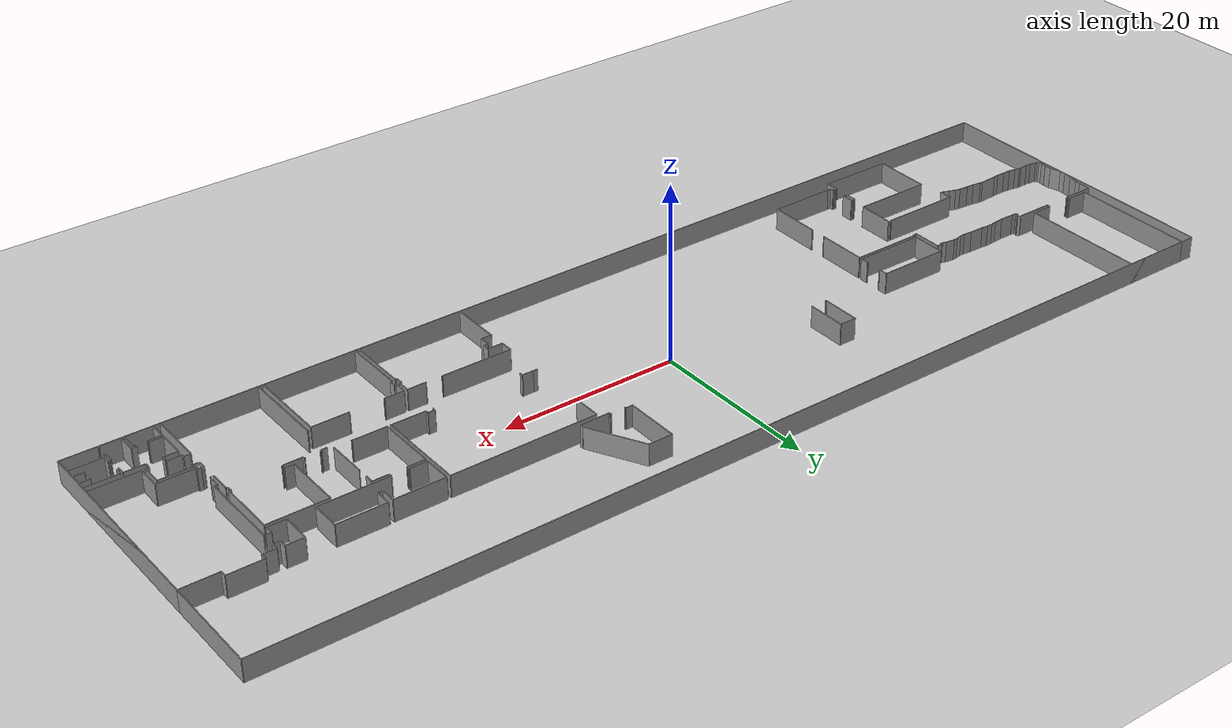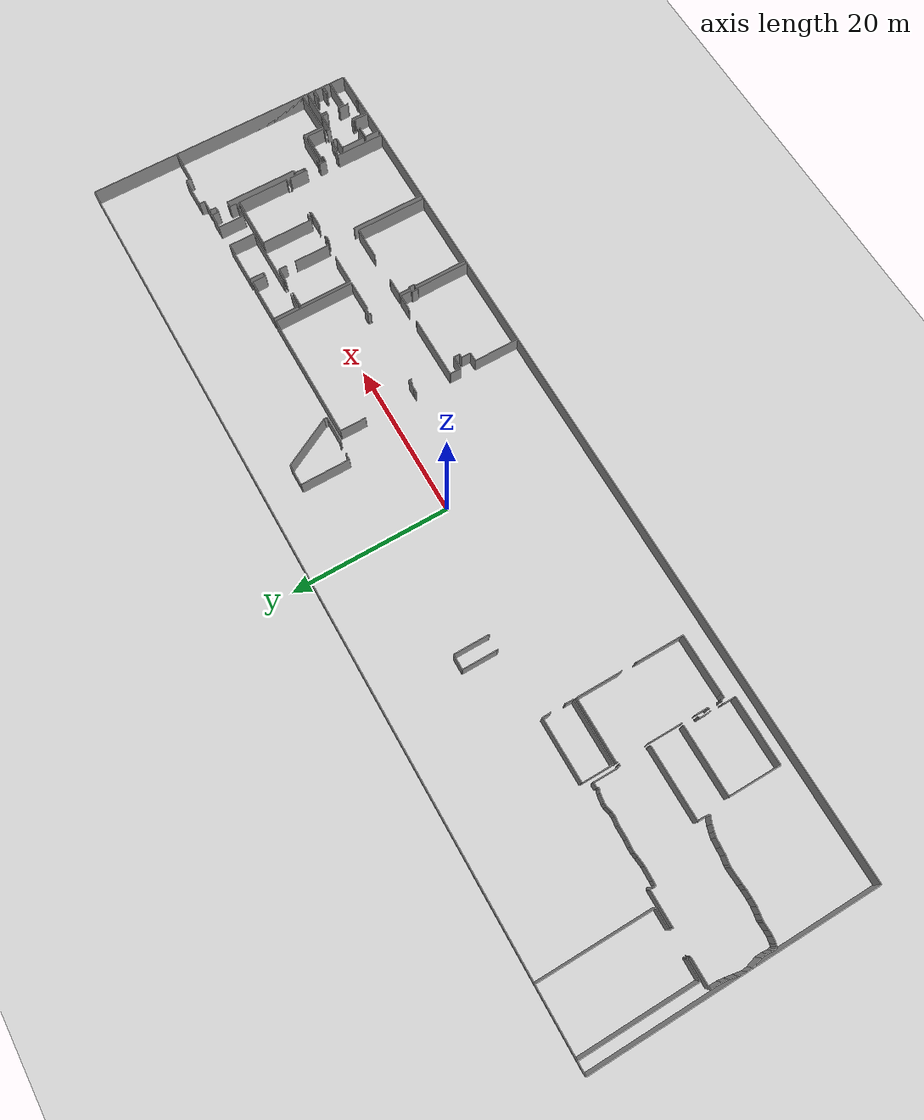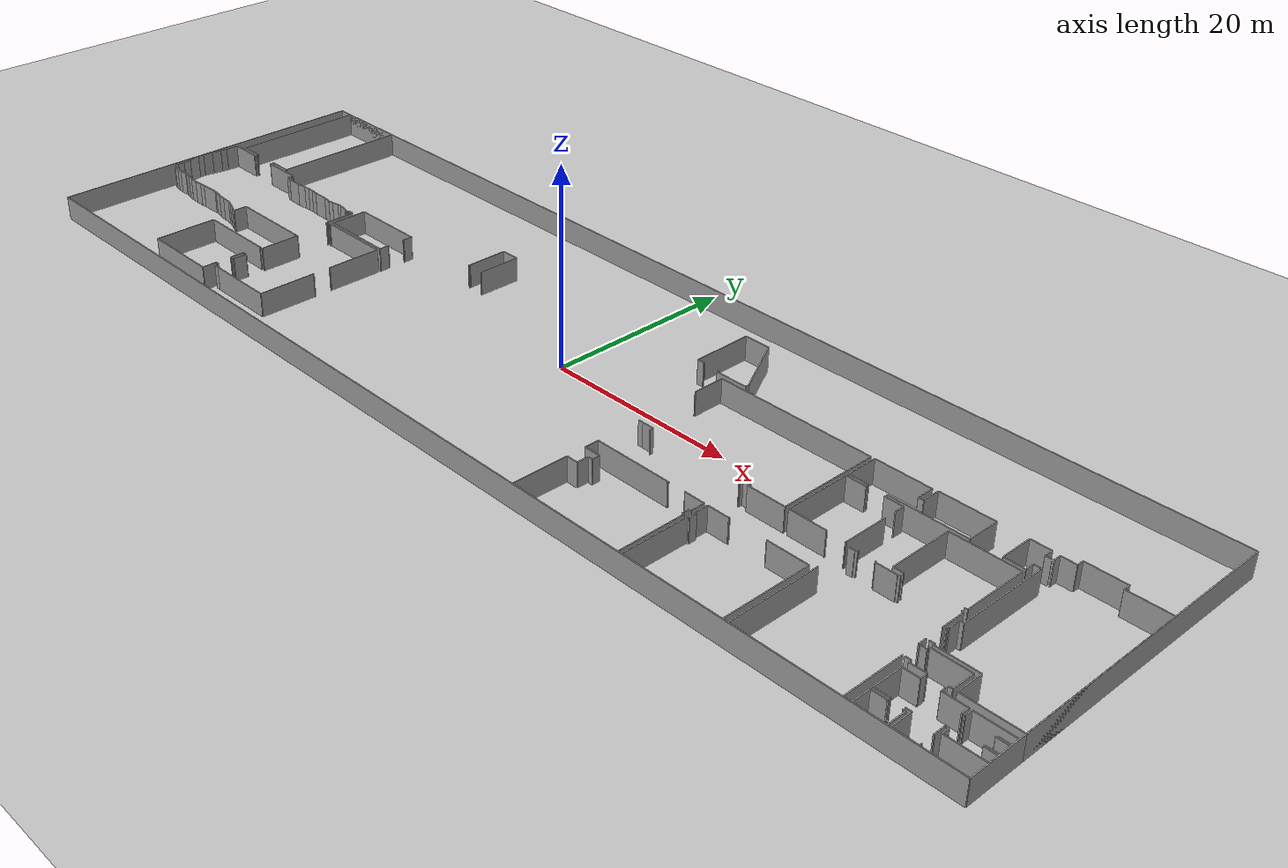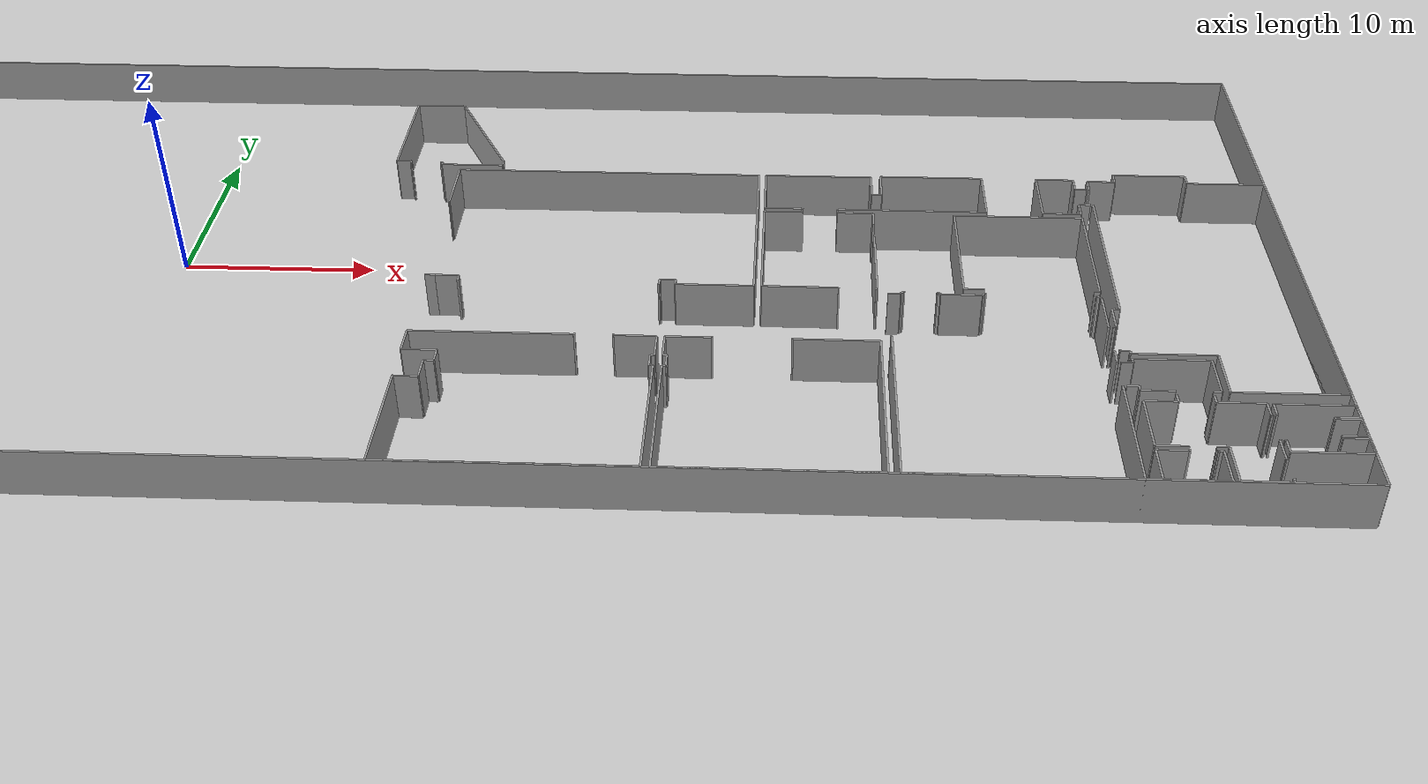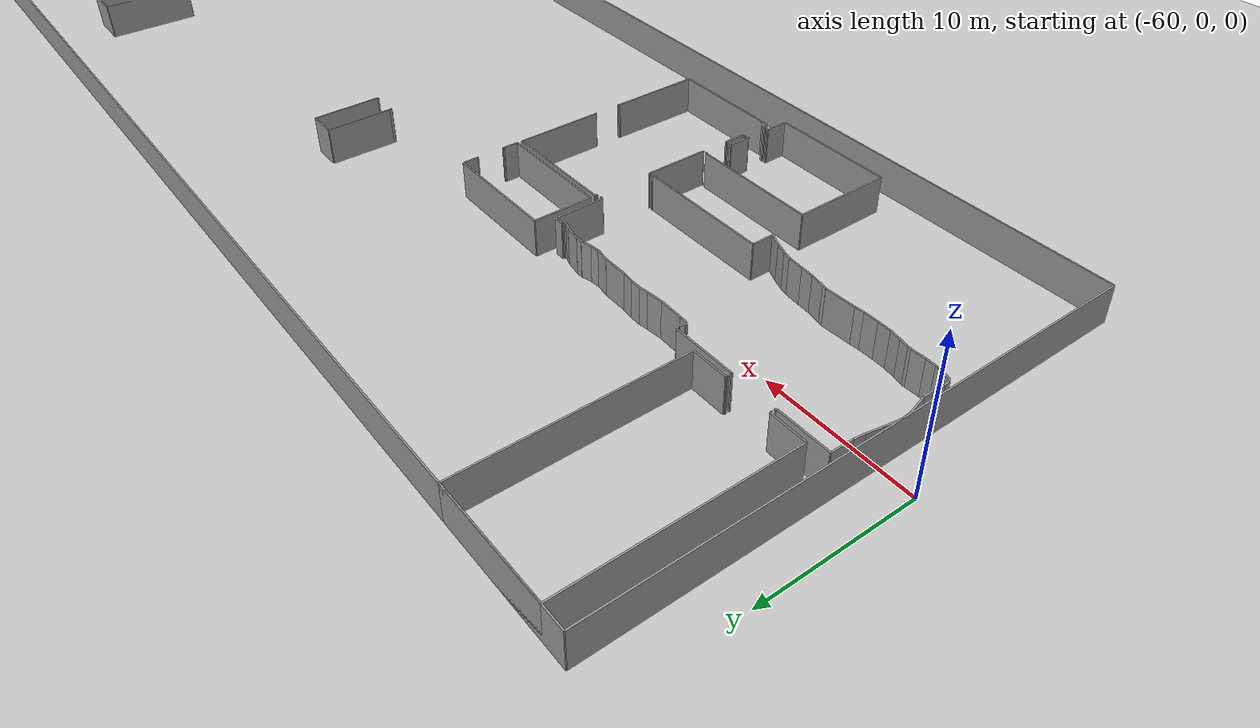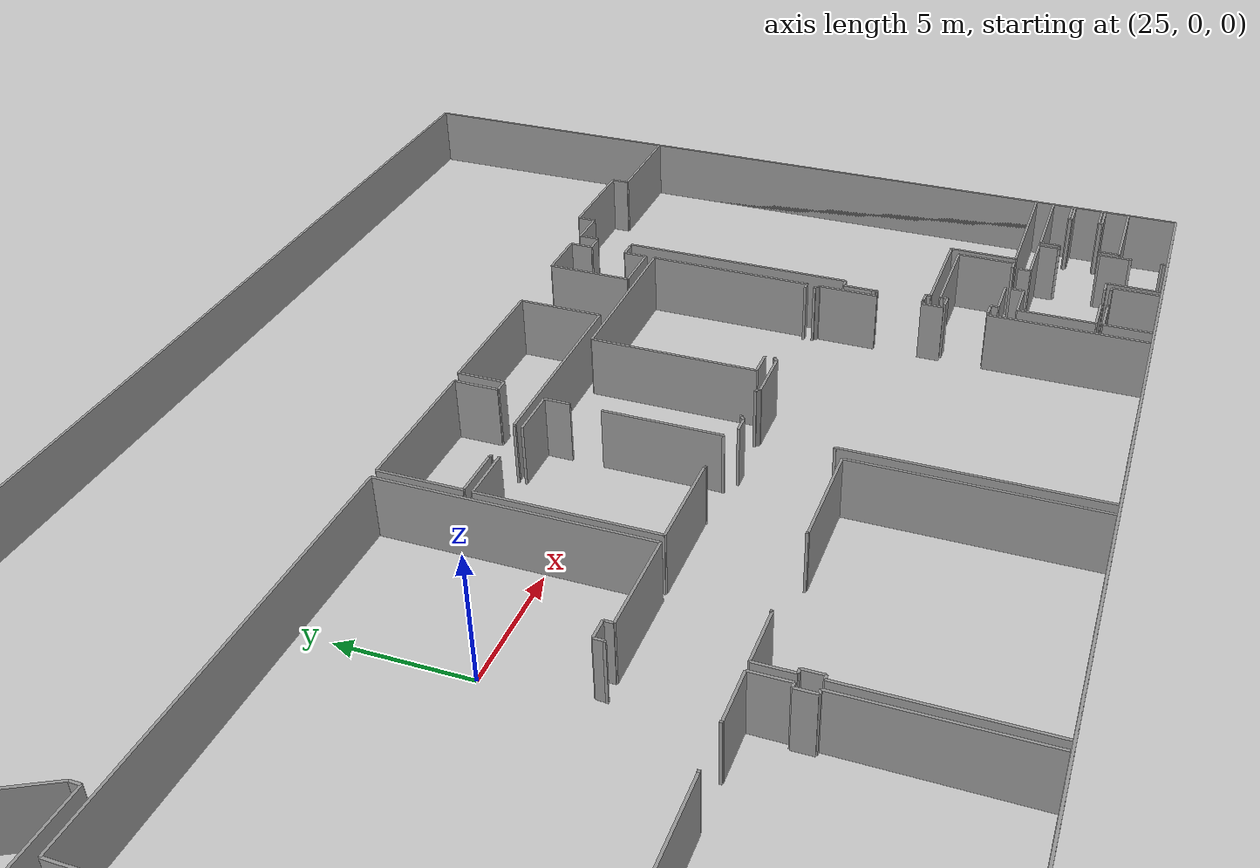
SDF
<sdf version="1.6">
  <world name="default">
    <light name="sun" type="directional">
      <cast_shadows>1</cast_shadows>
      <pose frame="">0 0 10 0 -0 0</pose>
      <diffuse>0.8 0.8 0.8 1</diffuse>
      <specular>0.1 0.1 0.1 1</specular>
      <attenuation>
        <range>1000</range>
        <constant>0.9</constant>
        <linear>0.01</linear>
        <quadratic>0.001</quadratic>
      </attenuation>
      <direction>-0.5 0.5 -1</direction>
    </light>
    <model name="ground_plane">
      <static>1</static>
      <link name="link">
        <collision name="collision">
          <geometry>
            <plane>
              <normal>0 0 1</normal>
              <size>100 100</size>
            </plane>
          </geometry>
          <surface>
            <friction>
              <ode>
                <mu>100</mu>
                <mu2>50</mu2>
              </ode>
              <torsional>
                <ode />
              </torsional>
            </friction>
            <contact>
              <ode />
            </contact>
            <bounce />
          </surface>
          <max_contacts>10</max_contacts>
        </collision>
        <visual name="visual">
          <cast_shadows>0</cast_shadows>
          <geometry>
            <plane>
              <normal>0 0 1</normal>
              <size>100 100</size>
            </plane>
          </geometry>
          <material>
            <script>
              <uri>file://media/materials/scripts/gazebo.material</uri>
              <name>Gazebo/Grey</name>
            </script>
          </material>
        </visual>
        <self_collide>0</self_collide>
        <kinematic>0</kinematic>
        <gravity>1</gravity>
      </link>
    </model>
    <gravity>0 0 -9.8</gravity>
    <magnetic_field>6e-06 2.3e-05 -4.2e-05</magnetic_field>
    <atmosphere type="adiabatic" />
    <physics default="0" name="default_physics" type="ode">
      <max_step_size>0.001</max_step_size>
      <real_time_factor>1</real_time_factor>
      <real_time_update_rate>1000</real_time_update_rate>
    </physics>
    <scene>
      <ambient>0.4 0.4 0.4 1</ambient>
      <background>0.7 0.7 0.7 1</background>
      <shadows>1</shadows>
    </scene>
    <spherical_coordinates>
      <surface_model>EARTH_WGS84</surface_model>
      <latitude_deg>0</latitude_deg>
      <longitude_deg>0</longitude_deg>
      <elevation>0</elevation>
      <heading_deg>0</heading_deg>
    </spherical_coordinates>
  <model name="0510030939_A_40_1_103">
		<static>1</static>
		<link name="Wall_0">
			<collision name="Wall_0_Collision">
				<geometry>
					<box>
						<size>14.3257616672 0.1 2.5</size>
					</box>
				</geometry>
				<pose frame="">7.16288083362 0 1.25 0 0 0</pose>
			</collision>
			<visual name="Wall_0_Visual">
				<pose frame="">7.16288083362 0 1.25 0 0 0</pose>
				<geometry>
					<box>
						<size>14.3257616672 0.1 2.5</size>
					</box>
				</geometry>
				<material>
					<script>
						<uri>file://media/materials/scripts/gazebo.material</uri>
						<name>Gazebo/Grey</name>
					</script>
					<ambient>1 1 1 1</ambient>
				</material>
			</visual>
			<pose frame="">1.59374781587 -14.3257616672 0 0 0 1.57079632679</pose>
		</link>
		<link name="Wall_1">
			<collision name="Wall_1_Collision">
				<geometry>
					<box>
						<size>7.91787019093 0.1 2.5</size>
					</box>
				</geometry>
				<pose frame="">3.95893509547 0 1.25 0 0 0</pose>
			</collision>
			<visual name="Wall_1_Visual">
				<pose frame="">3.95893509547 0 1.25 0 0 0</pose>
				<geometry>
					<box>
						<size>7.91787019093 0.1 2.5</size>
					</box>
				</geometry>
				<material>
					<script>
						<uri>file://media/materials/scripts/gazebo.material</uri>
						<name>Gazebo/Grey</name>
					</script>
					<ambient>1 1 1 1</ambient>
				</material>
			</visual>
			<pose frame="">1.59374781587 -0.0 0 0 0 0.0</pose>
		</link>
		<link name="Wall_2">
			<collision name="Wall_2_Collision">
				<geometry>
					<box>
						<size>14.3209327445 0.1 2.5</size>
					</box>
				</geometry>
				<pose frame="">7.16046637227 0 1.25 0 0 0</pose>
			</collision>
			<visual name="Wall_2_Visual">
				<pose frame="">7.16046637227 0 1.25 0 0 0</pose>
				<geometry>
					<box>
						<size>14.3209327445 0.1 2.5</size>
					</box>
				</geometry>
				<material>
					<script>
						<uri>file://media/materials/scripts/gazebo.material</uri>
						<name>Gazebo/Grey</name>
					</script>
					<ambient>1 1 1 1</ambient>
				</material>
			</visual>
			<pose frame="">9.5116180068 -0.0 0 0 0 -1.57079632679</pose>
		</link>
		<link name="Wall_3">
			<collision name="Wall_3_Collision">
				<geometry>
					<box>
						<size>2.41090319916 0.1 2.5</size>
					</box>
				</geometry>
				<pose frame="">1.20545159958 0 1.25 0 0 0</pose>
			</collision>
			<visual name="Wall_3_Visual">
				<pose frame="">1.20545159958 0 1.25 0 0 0</pose>
				<geometry>
					<box>
						<size>2.41090319916 0.1 2.5</size>
					</box>
				</geometry>
				<material>
					<script>
						<uri>file://media/materials/scripts/gazebo.material</uri>
						<name>Gazebo/Grey</name>
					</script>
					<ambient>1 1 1 1</ambient>
				</material>
			</visual>
			<pose frame="">9.5116180068 -14.3209327445 0 0 0 3.14159265359</pose>
		</link>
		<link name="Wall_4">
			<collision name="Wall_4_Collision">
				<geometry>
					<box>
						<size>0.105346761127 0.1 2.5</size>
					</box>
				</geometry>
				<pose frame="">0.0526733805636 0 1.25 0 0 0</pose>
			</collision>
			<visual name="Wall_4_Visual">
				<pose frame="">0.0526733805636 0 1.25 0 0 0</pose>
				<geometry>
					<box>
						<size>0.105346761127 0.1 2.5</size>
					</box>
				</geometry>
				<material>
					<script>
						<uri>file://media/materials/scripts/gazebo.material</uri>
						<name>Gazebo/Grey</name>
					</script>
					<ambient>1 1 1 1</ambient>
				</material>
			</visual>
			<pose frame="">7.10071480764 -14.3209327445 0 0 0 -1.57079632679</pose>
		</link>
		<link name="Wall_5">
			<collision name="Wall_5_Collision">
				<geometry>
					<box>
						<size>0.075356609588 0.1 2.5</size>
					</box>
				</geometry>
				<pose frame="">0.037678304794 0 1.25 0 0 0</pose>
			</collision>
			<visual name="Wall_5_Visual">
				<pose frame="">0.037678304794 0 1.25 0 0 0</pose>
				<geometry>
					<box>
						<size>0.075356609588 0.1 2.5</size>
					</box>
				</geometry>
				<material>
					<script>
						<uri>file://media/materials/scripts/gazebo.material</uri>
						<name>Gazebo/Grey</name>
					</script>
					<ambient>1 1 1 1</ambient>
				</material>
			</visual>
			<pose frame="">7.10071480764 -14.4262795057 0 0 0 3.14159265359</pose>
		</link>
		<link name="Wall_6">
			<collision name="Wall_6_Collision">
				<geometry>
					<box>
						<size>0.0561679956794 0.1 2.5</size>
					</box>
				</geometry>
				<pose frame="">0.0280839978397 0 1.25 0 0 0</pose>
			</collision>
			<visual name="Wall_6_Visual">
				<pose frame="">0.0280839978397 0 1.25 0 0 0</pose>
				<geometry>
					<box>
						<size>0.0561679956794 0.1 2.5</size>
					</box>
				</geometry>
				<material>
					<script>
						<uri>file://media/materials/scripts/gazebo.material</uri>
						<name>Gazebo/Grey</name>
					</script>
					<ambient>1 1 1 1</ambient>
				</material>
			</visual>
			<pose frame="">4.03866950472 -14.4262795057 0 0 0 3.14159265359</pose>
		</link>
		<link name="Wall_7">
			<collision name="Wall_7_Collision">
				<geometry>
					<box>
						<size>0.0944181465832 0.1 2.5</size>
					</box>
				</geometry>
				<pose frame="">0.0472090732916 0 1.25 0 0 0</pose>
			</collision>
			<visual name="Wall_7_Visual">
				<pose frame="">0.0472090732916 0 1.25 0 0 0</pose>
				<geometry>
					<box>
						<size>0.0944181465832 0.1 2.5</size>
					</box>
				</geometry>
				<material>
					<script>
						<uri>file://media/materials/scripts/gazebo.material</uri>
						<name>Gazebo/Grey</name>
					</script>
					<ambient>1 1 1 1</ambient>
				</material>
			</visual>
			<pose frame="">3.98250150904 -14.4262795057 0 0 0 1.57079632679</pose>
		</link>
		<link name="Wall_8">
			<collision name="Wall_8_Collision">
				<geometry>
					<box>
						<size>2.38876148095 0.1 2.5</size>
					</box>
				</geometry>
				<pose frame="">1.19438074048 0 1.25 0 0 0</pose>
			</collision>
			<visual name="Wall_8_Visual">
				<pose frame="">1.19438074048 0 1.25 0 0 0</pose>
				<geometry>
					<box>
						<size>2.38876148095 0.1 2.5</size>
					</box>
				</geometry>
				<material>
					<script>
						<uri>file://media/materials/scripts/gazebo.material</uri>
						<name>Gazebo/Grey</name>
					</script>
					<ambient>1 1 1 1</ambient>
				</material>
			</visual>
			<pose frame="">3.98250150904 -14.3318613591 0 0 0 3.13903915525</pose>
		</link>
		<link name="Wall_9">
			<collision name="Wall_9_Collision">
				<geometry>
					<box>
						<size>0.397898713287 0.1 2.5</size>
					</box>
				</geometry>
				<pose frame="">0.198949356643 0 1.25 0 0 0</pose>
			</collision>
			<visual name="Wall_9_Visual">
				<pose frame="">0.198949356643 0 1.25 0 0 0</pose>
				<geometry>
					<box>
						<size>0.397898713287 0.1 2.5</size>
					</box>
				</geometry>
				<material>
					<script>
						<uri>file://media/materials/scripts/gazebo.material</uri>
						<name>Gazebo/Grey</name>
					</script>
					<ambient>1 1 1 1</ambient>
				</material>
			</visual>
			<pose frame="">0.363084156686 -22.5781364171 0 0 0 1.68149234334</pose>
		</link>
		<link name="Wall_10">
			<collision name="Wall_10_Collision">
				<geometry>
					<box>
						<size>0.665108872387 0.1 2.5</size>
					</box>
				</geometry>
				<pose frame="">0.332554436194 0 1.25 0 0 0</pose>
			</collision>
			<visual name="Wall_10_Visual">
				<pose frame="">0.332554436194 0 1.25 0 0 0</pose>
				<geometry>
					<box>
						<size>0.665108872387 0.1 2.5</size>
					</box>
				</geometry>
				<material>
					<script>
						<uri>file://media/materials/scripts/gazebo.material</uri>
						<name>Gazebo/Grey</name>
					</script>
					<ambient>1 1 1 1</ambient>
				</material>
			</visual>
			<pose frame="">0.319128252375 -22.1826730629 0 0 0 1.43825110736</pose>
		</link>
		<link name="Wall_11">
			<collision name="Wall_11_Collision">
				<geometry>
					<box>
						<size>0.772687319202 0.1 2.5</size>
					</box>
				</geometry>
				<pose frame="">0.386343659601 0 1.25 0 0 0</pose>
			</collision>
			<visual name="Wall_11_Visual">
				<pose frame="">0.386343659601 0 1.25 0 0 0</pose>
				<geometry>
					<box>
						<size>0.772687319202 0.1 2.5</size>
					</box>
				</geometry>
				<material>
					<script>
						<uri>file://media/materials/scripts/gazebo.material</uri>
						<name>Gazebo/Grey</name>
					</script>
					<ambient>1 1 1 1</ambient>
				</material>
			</visual>
			<pose frame="">0.407027353306 -21.5233980367 0 0 0 1.60914157728</pose>
		</link>
		<link name="Wall_12">
			<collision name="Wall_12_Collision">
				<geometry>
					<box>
						<size>1.2908194455 0.1 2.5</size>
					</box>
				</geometry>
				<pose frame="">0.645409722752 0 1.25 0 0 0</pose>
			</collision>
			<visual name="Wall_12_Visual">
				<pose frame="">0.645409722752 0 1.25 0 0 0</pose>
				<geometry>
					<box>
						<size>1.2908194455 0.1 2.5</size>
					</box>
				</geometry>
				<material>
					<script>
						<uri>file://media/materials/scripts/gazebo.material</uri>
						<name>Gazebo/Grey</name>
					</script>
					<ambient>1 1 1 1</ambient>
				</material>
			</visual>
			<pose frame="">0.377405724815 -20.7512787114 0 0 0 1.83284775393</pose>
		</link>
		<link name="Wall_13">
			<collision name="Wall_13_Collision">
				<geometry>
					<box>
						<size>0.670313680231 0.1 2.5</size>
					</box>
				</geometry>
				<pose frame="">0.335156840115 0 1.25 0 0 0</pose>
			</collision>
			<visual name="Wall_13_Visual">
				<pose frame="">0.335156840115 0 1.25 0 0 0</pose>
				<geometry>
					<box>
						<size>0.670313680231 0.1 2.5</size>
					</box>
				</geometry>
				<material>
					<script>
						<uri>file://media/materials/scripts/gazebo.material</uri>
						<name>Gazebo/Grey</name>
					</script>
					<ambient>1 1 1 1</ambient>
				</material>
			</visual>
			<pose frame="">0.0430028274613 -19.504527115 0 0 0 1.63499370317</pose>
		</link>
		<link name="Wall_14">
			<collision name="Wall_14_Collision">
				<geometry>
					<box>
						<size>1.0477580429 0.1 2.5</size>
					</box>
				</geometry>
				<pose frame="">0.52387902145 0 1.25 0 0 0</pose>
			</collision>
			<visual name="Wall_14_Visual">
				<pose frame="">0.52387902145 0 1.25 0 0 0</pose>
				<geometry>
					<box>
						<size>1.0477580429 0.1 2.5</size>
					</box>
				</geometry>
				<material>
					<script>
						<uri>file://media/materials/scripts/gazebo.material</uri>
						<name>Gazebo/Grey</name>
					</script>
					<ambient>1 1 1 1</ambient>
				</material>
			</visual>
			<pose frame="">0.0 -18.8355942434 0 0 0 1.40280433486</pose>
		</link>
		<link name="Wall_15">
			<collision name="Wall_15_Collision">
				<geometry>
					<box>
						<size>1.00523139012 0.1 2.5</size>
					</box>
				</geometry>
				<pose frame="">0.502615695059 0 1.25 0 0 0</pose>
			</collision>
			<visual name="Wall_15_Visual">
				<pose frame="">0.502615695059 0 1.25 0 0 0</pose>
				<geometry>
					<box>
						<size>1.00523139012 0.1 2.5</size>
					</box>
				</geometry>
				<material>
					<script>
						<uri>file://media/materials/scripts/gazebo.material</uri>
						<name>Gazebo/Grey</name>
					</script>
					<ambient>1 1 1 1</ambient>
				</material>
			</visual>
			<pose frame="">0.175188232678 -17.8025860152 0 0 0 1.38277233144</pose>
		</link>
		<link name="Wall_16">
			<collision name="Wall_16_Collision">
				<geometry>
					<box>
						<size>0.703167774783 0.1 2.5</size>
					</box>
				</geometry>
				<pose frame="">0.351583887391 0 1.25 0 0 0</pose>
			</collision>
			<visual name="Wall_16_Visual">
				<pose frame="">0.351583887391 0 1.25 0 0 0</pose>
				<geometry>
					<box>
						<size>0.703167774783 0.1 2.5</size>
					</box>
				</geometry>
				<material>
					<script>
						<uri>file://media/materials/scripts/gazebo.material</uri>
						<name>Gazebo/Grey</name>
					</script>
					<ambient>1 1 1 1</ambient>
				</material>
			</visual>
			<pose frame="">0.363084156686 -16.8150713219 0 0 0 1.44546401047</pose>
		</link>
		<link name="Wall_17">
			<collision name="Wall_17_Collision">
				<geometry>
					<box>
						<size>1.38489533323 0.1 2.5</size>
					</box>
				</geometry>
				<pose frame="">0.692447666616 0 1.25 0 0 0</pose>
			</collision>
			<visual name="Wall_17_Visual">
				<pose frame="">0.692447666616 0 1.25 0 0 0</pose>
				<geometry>
					<box>
						<size>1.38489533323 0.1 2.5</size>
					</box>
				</geometry>
				<material>
					<script>
						<uri>file://media/materials/scripts/gazebo.material</uri>
						<name>Gazebo/Grey</name>
					</script>
					<ambient>1 1 1 1</ambient>
				</material>
			</visual>
			<pose frame="">0.450983257617 -16.1174190679 0 0 0 1.54699173743</pose>
		</link>
		<link name="Wall_18">
			<collision name="Wall_18_Collision">
				<geometry>
					<box>
						<size>3.47542650189 0.1 2.5</size>
					</box>
				</geometry>
				<pose frame="">1.73771325095 0 1.25 0 0 0</pose>
			</collision>
			<visual name="Wall_18_Visual">
				<pose frame="">1.73771325095 0 1.25 0 0 0</pose>
				<geometry>
					<box>
						<size>3.47542650189 0.1 2.5</size>
					</box>
				</geometry>
				<material>
					<script>
						<uri>file://media/materials/scripts/gazebo.material</uri>
						<name>Gazebo/Grey</name>
					</script>
					<ambient>1 1 1 1</ambient>
				</material>
			</visual>
			<pose frame="">0.483947008927 -14.7329160975 0 0 0 0.0</pose>
		</link>
		<link name="Wall_19">
			<collision name="Wall_19_Collision">
				<geometry>
					<box>
						<size>0.0365981510309 0.1 2.5</size>
					</box>
				</geometry>
				<pose frame="">0.0182990755155 0 1.25 0 0 0</pose>
			</collision>
			<visual name="Wall_19_Visual">
				<pose frame="">0.0182990755155 0 1.25 0 0 0</pose>
				<geometry>
					<box>
						<size>0.0365981510309 0.1 2.5</size>
					</box>
				</geometry>
				<material>
					<script>
						<uri>file://media/materials/scripts/gazebo.material</uri>
						<name>Gazebo/Grey</name>
					</script>
					<ambient>1 1 1 1</ambient>
				</material>
			</visual>
			<pose frame="">3.95937351082 -14.7329160975 0 0 0 1.57079632679</pose>
		</link>
		<link name="Wall_20">
			<collision name="Wall_20_Collision">
				<geometry>
					<box>
						<size>0.0950535311497 0.1 2.5</size>
					</box>
				</geometry>
				<pose frame="">0.0475267655749 0 1.25 0 0 0</pose>
			</collision>
			<visual name="Wall_20_Visual">
				<pose frame="">0.0475267655749 0 1.25 0 0 0</pose>
				<geometry>
					<box>
						<size>0.0950535311497 0.1 2.5</size>
					</box>
				</geometry>
				<material>
					<script>
						<uri>file://media/materials/scripts/gazebo.material</uri>
						<name>Gazebo/Grey</name>
					</script>
					<ambient>1 1 1 1</ambient>
				</material>
			</visual>
			<pose frame="">3.95937351082 -14.6963179464 0 0 0 0.0</pose>
		</link>
		<link name="Wall_21">
			<collision name="Wall_21_Collision">
				<geometry>
					<box>
						<size>0.0831083012994 0.1 2.5</size>
					</box>
				</geometry>
				<pose frame="">0.0415541506497 0 1.25 0 0 0</pose>
			</collision>
			<visual name="Wall_21_Visual">
				<pose frame="">0.0415541506497 0 1.25 0 0 0</pose>
				<geometry>
					<box>
						<size>0.0831083012994 0.1 2.5</size>
					</box>
				</geometry>
				<material>
					<script>
						<uri>file://media/materials/scripts/gazebo.material</uri>
						<name>Gazebo/Grey</name>
					</script>
					<ambient>1 1 1 1</ambient>
				</material>
			</visual>
			<pose frame="">7.04467388887 -14.6963179464 0 0 0 0.0</pose>
		</link>
		<link name="Wall_22">
			<collision name="Wall_22_Collision">
				<geometry>
					<box>
						<size>0.0255424595737 0.1 2.5</size>
					</box>
				</geometry>
				<pose frame="">0.0127712297868 0 1.25 0 0 0</pose>
			</collision>
			<visual name="Wall_22_Visual">
				<pose frame="">0.0127712297868 0 1.25 0 0 0</pose>
				<geometry>
					<box>
						<size>0.0255424595737 0.1 2.5</size>
					</box>
				</geometry>
				<material>
					<script>
						<uri>file://media/materials/scripts/gazebo.material</uri>
						<name>Gazebo/Grey</name>
					</script>
					<ambient>1 1 1 1</ambient>
				</material>
			</visual>
			<pose frame="">7.12778219017 -14.6963179464 0 0 0 -1.57079632679</pose>
		</link>
		<link name="Wall_23">
			<collision name="Wall_23_Collision">
				<geometry>
					<box>
						<size>4.15427137275 0.1 2.5</size>
					</box>
				</geometry>
				<pose frame="">2.07713568637 0 1.25 0 0 0</pose>
			</collision>
			<visual name="Wall_23_Visual">
				<pose frame="">2.07713568637 0 1.25 0 0 0</pose>
				<geometry>
					<box>
						<size>4.15427137275 0.1 2.5</size>
					</box>
				</geometry>
				<material>
					<script>
						<uri>file://media/materials/scripts/gazebo.material</uri>
						<name>Gazebo/Grey</name>
					</script>
					<ambient>1 1 1 1</ambient>
				</material>
			</visual>
			<pose frame="">7.12778219017 -14.721860406 0 0 0 0.0</pose>
		</link>
		<link name="Wall_24">
			<collision name="Wall_24_Collision">
				<geometry>
					<box>
						<size>0.263878079095 0.1 2.5</size>
					</box>
				</geometry>
				<pose frame="">0.131939039548 0 1.25 0 0 0</pose>
			</collision>
			<visual name="Wall_24_Visual">
				<pose frame="">0.131939039548 0 1.25 0 0 0</pose>
				<geometry>
					<box>
						<size>0.263878079095 0.1 2.5</size>
					</box>
				</geometry>
				<material>
					<script>
						<uri>file://media/materials/scripts/gazebo.material</uri>
						<name>Gazebo/Grey</name>
					</script>
					<ambient>1 1 1 1</ambient>
				</material>
			</visual>
			<pose frame="">11.2820535629 -14.721860406 0 0 0 -0.909668684216</pose>
		</link>
		<link name="Wall_25">
			<collision name="Wall_25_Collision">
				<geometry>
					<box>
						<size>0.0911197295433 0.1 2.5</size>
					</box>
				</geometry>
				<pose frame="">0.0455598647716 0 1.25 0 0 0</pose>
			</collision>
			<visual name="Wall_25_Visual">
				<pose frame="">0.0455598647716 0 1.25 0 0 0</pose>
				<geometry>
					<box>
						<size>0.0911197295433 0.1 2.5</size>
					</box>
				</geometry>
				<material>
					<script>
						<uri>file://media/materials/scripts/gazebo.material</uri>
						<name>Gazebo/Grey</name>
					</script>
					<ambient>1 1 1 1</ambient>
				</material>
			</visual>
			<pose frame="">11.4440766274 -14.9301394669 0 0 0 -1.99326871918</pose>
		</link>
		<link name="Wall_26">
			<collision name="Wall_26_Collision">
				<geometry>
					<box>
						<size>0.258692454681 0.1 2.5</size>
					</box>
				</geometry>
				<pose frame="">0.12934622734 0 1.25 0 0 0</pose>
			</collision>
			<visual name="Wall_26_Visual">
				<pose frame="">0.12934622734 0 1.25 0 0 0</pose>
				<geometry>
					<box>
						<size>0.258692454681 0.1 2.5</size>
					</box>
				</geometry>
				<material>
					<script>
						<uri>file://media/materials/scripts/gazebo.material</uri>
						<name>Gazebo/Grey</name>
					</script>
					<ambient>1 1 1 1</ambient>
				</material>
			</visual>
			<pose frame="">11.4067160149 -15.0132477682 0 0 0 -2.31102356874</pose>
		</link>
		<link name="Wall_27">
			<collision name="Wall_27_Collision">
				<geometry>
					<box>
						<size>0.116695152244 0.1 2.5</size>
					</box>
				</geometry>
				<pose frame="">0.0583475761218 0 1.25 0 0 0</pose>
			</collision>
			<visual name="Wall_27_Visual">
				<pose frame="">0.0583475761218 0 1.25 0 0 0</pose>
				<geometry>
					<box>
						<size>0.116695152244 0.1 2.5</size>
					</box>
				</geometry>
				<material>
					<script>
						<uri>file://media/materials/scripts/gazebo.material</uri>
						<name>Gazebo/Grey</name>
					</script>
					<ambient>1 1 1 1</ambient>
				</material>
			</visual>
			<pose frame="">11.2322394129 -15.2042443689 0 0 0 -1.4999543752</pose>
		</link>
		<link name="Wall_28">
			<collision name="Wall_28_Collision">
				<geometry>
					<box>
						<size>0.17400843633 0.1 2.5</size>
					</box>
				</geometry>
				<pose frame="">0.0870042181649 0 1.25 0 0 0</pose>
			</collision>
			<visual name="Wall_28_Visual">
				<pose frame="">0.0870042181649 0 1.25 0 0 0</pose>
				<geometry>
					<box>
						<size>0.17400843633 0.1 2.5</size>
					</box>
				</geometry>
				<material>
					<script>
						<uri>file://media/materials/scripts/gazebo.material</uri>
						<name>Gazebo/Grey</name>
					</script>
					<ambient>1 1 1 1</ambient>
				</material>
			</visual>
			<pose frame="">11.2404994123 -15.3206468215 0 0 0 -0.580508314039</pose>
		</link>
		<link name="Wall_29">
			<collision name="Wall_29_Collision">
				<geometry>
					<box>
						<size>0.496441539185 0.1 2.5</size>
					</box>
				</geometry>
				<pose frame="">0.248220769592 0 1.25 0 0 0</pose>
			</collision>
			<visual name="Wall_29_Visual">
				<pose frame="">0.248220769592 0 1.25 0 0 0</pose>
				<geometry>
					<box>
						<size>0.496441539185 0.1 2.5</size>
					</box>
				</geometry>
				<material>
					<script>
						<uri>file://media/materials/scripts/gazebo.material</uri>
						<name>Gazebo/Grey</name>
					</script>
					<ambient>1 1 1 1</ambient>
				</material>
			</visual>
			<pose frame="">11.386002478 -15.4160815834 0 0 0 -0.0922821337498</pose>
		</link>
		<link name="Wall_30">
			<collision name="Wall_30_Collision">
				<geometry>
					<box>
						<size>1.59668804053 0.1 2.5</size>
					</box>
				</geometry>
				<pose frame="">0.798344020266 0 1.25 0 0 0</pose>
			</collision>
			<visual name="Wall_30_Visual">
				<pose frame="">0.798344020266 0 1.25 0 0 0</pose>
				<geometry>
					<box>
						<size>1.59668804053 0.1 2.5</size>
					</box>
				</geometry>
				<material>
					<script>
						<uri>file://media/materials/scripts/gazebo.material</uri>
						<name>Gazebo/Grey</name>
					</script>
					<ambient>1 1 1 1</ambient>
				</material>
			</visual>
			<pose frame="">11.8803316707 -15.4618292722 0 0 0 -0.0274612477568</pose>
		</link>
		<link name="Wall_31">
			<collision name="Wall_31_Collision">
				<geometry>
					<box>
						<size>1.07361924244 0.1 2.5</size>
					</box>
				</geometry>
				<pose frame="">0.536809621221 0 1.25 0 0 0</pose>
			</collision>
			<visual name="Wall_31_Visual">
				<pose frame="">0.536809621221 0 1.25 0 0 0</pose>
				<geometry>
					<box>
						<size>1.07361924244 0.1 2.5</size>
					</box>
				</geometry>
				<material>
					<script>
						<uri>file://media/materials/scripts/gazebo.material</uri>
						<name>Gazebo/Grey</name>
					</script>
					<ambient>1 1 1 1</ambient>
				</material>
			</visual>
			<pose frame="">13.4764177018 -15.5056708073 0 0 0 0.101611952717</pose>
		</link>
		<link name="Wall_32">
			<collision name="Wall_32_Collision">
				<geometry>
					<box>
						<size>0.586719998756 0.1 2.5</size>
					</box>
				</geometry>
				<pose frame="">0.293359999378 0 1.25 0 0 0</pose>
			</collision>
			<visual name="Wall_32_Visual">
				<pose frame="">0.293359999378 0 1.25 0 0 0</pose>
				<geometry>
					<box>
						<size>0.586719998756 0.1 2.5</size>
					</box>
				</geometry>
				<material>
					<script>
						<uri>file://media/materials/scripts/gazebo.material</uri>
						<name>Gazebo/Grey</name>
					</script>
					<ambient>1 1 1 1</ambient>
				</material>
			</visual>
			<pose frame="">14.5444991581 -15.3967658926 0 0 0 0.136659255228</pose>
		</link>
		<link name="Wall_33">
			<collision name="Wall_33_Collision">
				<geometry>
					<box>
						<size>0.654829750994 0.1 2.5</size>
					</box>
				</geometry>
				<pose frame="">0.327414875497 0 1.25 0 0 0</pose>
			</collision>
			<visual name="Wall_33_Visual">
				<pose frame="">0.327414875497 0 1.25 0 0 0</pose>
				<geometry>
					<box>
						<size>0.654829750994 0.1 2.5</size>
					</box>
				</geometry>
				<material>
					<script>
						<uri>file://media/materials/scripts/gazebo.material</uri>
						<name>Gazebo/Grey</name>
					</script>
					<ambient>1 1 1 1</ambient>
				</material>
			</visual>
			<pose frame="">15.1257489596 -15.3168345141 0 0 0 -0.00271685727806</pose>
		</link>
		<link name="Wall_34">
			<collision name="Wall_34_Collision">
				<geometry>
					<box>
						<size>0.79578620243 0.1 2.5</size>
					</box>
				</geometry>
				<pose frame="">0.397893101215 0 1.25 0 0 0</pose>
			</collision>
			<visual name="Wall_34_Visual">
				<pose frame="">0.397893101215 0 1.25 0 0 0</pose>
				<geometry>
					<box>
						<size>0.79578620243 0.1 2.5</size>
					</box>
				</geometry>
				<material>
					<script>
						<uri>file://media/materials/scripts/gazebo.material</uri>
						<name>Gazebo/Grey</name>
					</script>
					<ambient>1 1 1 1</ambient>
				</material>
			</visual>
			<pose frame="">15.7805762938 -15.3186135909 0 0 0 -0.110569048638</pose>
		</link>
		<link name="Wall_35">
			<collision name="Wall_35_Collision">
				<geometry>
					<box>
						<size>1.6155288038 0.1 2.5</size>
					</box>
				</geometry>
				<pose frame="">0.807764401902 0 1.25 0 0 0</pose>
			</collision>
			<visual name="Wall_35_Visual">
				<pose frame="">0.807764401902 0 1.25 0 0 0</pose>
				<geometry>
					<box>
						<size>1.6155288038 0.1 2.5</size>
					</box>
				</geometry>
				<material>
					<script>
						<uri>file://media/materials/scripts/gazebo.material</uri>
						<name>Gazebo/Grey</name>
					</script>
					<ambient>1 1 1 1</ambient>
				</material>
			</visual>
			<pose frame="">16.5715030022 -15.406423738 0 0 0 -7.86596395808e-05</pose>
		</link>
		<link name="Wall_36">
			<collision name="Wall_36_Collision">
				<geometry>
					<box>
						<size>0.931280798708 0.1 2.5</size>
					</box>
				</geometry>
				<pose frame="">0.465640399354 0 1.25 0 0 0</pose>
			</collision>
			<visual name="Wall_36_Visual">
				<pose frame="">0.465640399354 0 1.25 0 0 0</pose>
				<geometry>
					<box>
						<size>0.931280798708 0.1 2.5</size>
					</box>
				</geometry>
				<material>
					<script>
						<uri>file://media/materials/scripts/gazebo.material</uri>
						<name>Gazebo/Grey</name>
					</script>
					<ambient>1 1 1 1</ambient>
				</material>
			</visual>
			<pose frame="">18.187031801 -15.4065508149 0 0 0 -0.144598707622</pose>
		</link>
		<link name="Wall_37">
			<collision name="Wall_37_Collision">
				<geometry>
					<box>
						<size>0.600963611716 0.1 2.5</size>
					</box>
				</geometry>
				<pose frame="">0.300481805858 0 1.25 0 0 0</pose>
			</collision>
			<visual name="Wall_37_Visual">
				<pose frame="">0.300481805858 0 1.25 0 0 0</pose>
				<geometry>
					<box>
						<size>0.600963611716 0.1 2.5</size>
					</box>
				</geometry>
				<material>
					<script>
						<uri>file://media/materials/scripts/gazebo.material</uri>
						<name>Gazebo/Grey</name>
					</script>
					<ambient>1 1 1 1</ambient>
				</material>
			</visual>
			<pose frame="">19.1085935763 -15.5407440353 0 0 0 0.0967860884634</pose>
		</link>
		<link name="Wall_38">
			<collision name="Wall_38_Collision">
				<geometry>
					<box>
						<size>0.703247013756 0.1 2.5</size>
					</box>
				</geometry>
				<pose frame="">0.351623506878 0 1.25 0 0 0</pose>
			</collision>
			<visual name="Wall_38_Visual">
				<pose frame="">0.351623506878 0 1.25 0 0 0</pose>
				<geometry>
					<box>
						<size>0.703247013756 0.1 2.5</size>
					</box>
				</geometry>
				<material>
					<script>
						<uri>file://media/materials/scripts/gazebo.material</uri>
						<name>Gazebo/Grey</name>
					</script>
					<ambient>1 1 1 1</ambient>
				</material>
			</visual>
			<pose frame="">19.7067446072 -15.4826698859 0 0 0 0.250719933261</pose>
		</link>
		<link name="Wall_39">
			<collision name="Wall_39_Collision">
				<geometry>
					<box>
						<size>0.427888517048 0.1 2.5</size>
					</box>
				</geometry>
				<pose frame="">0.213944258524 0 1.25 0 0 0</pose>
			</collision>
			<visual name="Wall_39_Visual">
				<pose frame="">0.213944258524 0 1.25 0 0 0</pose>
				<geometry>
					<box>
						<size>0.427888517048 0.1 2.5</size>
					</box>
				</geometry>
				<material>
					<script>
						<uri>file://media/materials/scripts/gazebo.material</uri>
						<name>Gazebo/Grey</name>
					</script>
					<ambient>1 1 1 1</ambient>
				</material>
			</visual>
			<pose frame="">20.3880039394 -15.308193284 0 0 0 0.00980069599143</pose>
		</link>
		<link name="Wall_40">
			<collision name="Wall_40_Collision">
				<geometry>
					<box>
						<size>1.0334365023 0.1 2.5</size>
					</box>
				</geometry>
				<pose frame="">0.516718251149 0 1.25 0 0 0</pose>
			</collision>
			<visual name="Wall_40_Visual">
				<pose frame="">0.516718251149 0 1.25 0 0 0</pose>
				<geometry>
					<box>
						<size>1.0334365023 0.1 2.5</size>
					</box>
				</geometry>
				<material>
					<script>
						<uri>file://media/materials/scripts/gazebo.material</uri>
						<name>Gazebo/Grey</name>
					</script>
					<ambient>1 1 1 1</ambient>
				</material>
			</visual>
			<pose frame="">20.8158719065 -15.3039997458 0 0 0 -0.149218280941</pose>
		</link>
		<link name="Wall_41">
			<collision name="Wall_41_Collision">
				<geometry>
					<box>
						<size>0.469003908946 0.1 2.5</size>
					</box>
				</geometry>
				<pose frame="">0.234501954473 0 1.25 0 0 0</pose>
			</collision>
			<visual name="Wall_41_Visual">
				<pose frame="">0.234501954473 0 1.25 0 0 0</pose>
				<geometry>
					<box>
						<size>0.469003908946 0.1 2.5</size>
					</box>
				</geometry>
				<material>
					<script>
						<uri>file://media/materials/scripts/gazebo.material</uri>
						<name>Gazebo/Grey</name>
					</script>
					<ambient>1 1 1 1</ambient>
				</material>
			</visual>
			<pose frame="">21.8378244432 -15.457635734 0 0 0 -0.324578068068</pose>
		</link>
		<link name="Wall_42">
			<collision name="Wall_42_Collision">
				<geometry>
					<box>
						<size>0.170334692848 0.1 2.5</size>
					</box>
				</geometry>
				<pose frame="">0.0851673464239 0 1.25 0 0 0</pose>
			</collision>
			<visual name="Wall_42_Visual">
				<pose frame="">0.0851673464239 0 1.25 0 0 0</pose>
				<geometry>
					<box>
						<size>0.170334692848 0.1 2.5</size>
					</box>
				</geometry>
				<material>
					<script>
						<uri>file://media/materials/scripts/gazebo.material</uri>
						<name>Gazebo/Grey</name>
					</script>
					<ambient>1 1 1 1</ambient>
				</material>
			</visual>
			<pose frame="">22.282339486 -15.607205261 0 0 0 -0.0246218888947</pose>
		</link>
		<link name="Wall_43">
			<collision name="Wall_43_Collision">
				<geometry>
					<box>
						<size>0.0921959426893 0.1 2.5</size>
					</box>
				</geometry>
				<pose frame="">0.0460979713446 0 1.25 0 0 0</pose>
			</collision>
			<visual name="Wall_43_Visual">
				<pose frame="">0.0460979713446 0 1.25 0 0 0</pose>
				<geometry>
					<box>
						<size>0.0921959426893 0.1 2.5</size>
					</box>
				</geometry>
				<material>
					<script>
						<uri>file://media/materials/scripts/gazebo.material</uri>
						<name>Gazebo/Grey</name>
					</script>
					<ambient>1 1 1 1</ambient>
				</material>
			</visual>
			<pose frame="">22.4526225498 -15.6113987991 0 0 0 0.944938823974</pose>
		</link>
		<link name="Wall_44">
			<collision name="Wall_44_Collision">
				<geometry>
					<box>
						<size>0.0832140343151 0.1 2.5</size>
					</box>
				</geometry>
				<pose frame="">0.0416070171575 0 1.25 0 0 0</pose>
			</collision>
			<visual name="Wall_44_Visual">
				<pose frame="">0.0416070171575 0 1.25 0 0 0</pose>
				<geometry>
					<box>
						<size>0.0832140343151 0.1 2.5</size>
					</box>
				</geometry>
				<material>
					<script>
						<uri>file://media/materials/scripts/gazebo.material</uri>
						<name>Gazebo/Grey</name>
					</script>
					<ambient>1 1 1 1</ambient>
				</material>
			</visual>
			<pose frame="">22.506630238 -15.5366775741 0 0 0 1.52038036991</pose>
		</link>
		<link name="Wall_45">
			<collision name="Wall_45_Collision">
				<geometry>
					<box>
						<size>0.627251644058 0.1 2.5</size>
					</box>
				</geometry>
				<pose frame="">0.313625822029 0 1.25 0 0 0</pose>
			</collision>
			<visual name="Wall_45_Visual">
				<pose frame="">0.313625822029 0 1.25 0 0 0</pose>
				<geometry>
					<box>
						<size>0.627251644058 0.1 2.5</size>
					</box>
				</geometry>
				<material>
					<script>
						<uri>file://media/materials/scripts/gazebo.material</uri>
						<name>Gazebo/Grey</name>
					</script>
					<ambient>1 1 1 1</ambient>
				</material>
			</visual>
			<pose frame="">22.5108237761 -15.4535692728 0 0 0 0.0</pose>
		</link>
		<link name="Wall_46">
			<collision name="Wall_46_Collision">
				<geometry>
					<box>
						<size>3.314038822 0.1 2.5</size>
					</box>
				</geometry>
				<pose frame="">1.657019411 0 1.25 0 0 0</pose>
			</collision>
			<visual name="Wall_46_Visual">
				<pose frame="">1.657019411 0 1.25 0 0 0</pose>
				<geometry>
					<box>
						<size>3.314038822 0.1 2.5</size>
					</box>
				</geometry>
				<material>
					<script>
						<uri>file://media/materials/scripts/gazebo.material</uri>
						<name>Gazebo/Grey</name>
					</script>
					<ambient>1 1 1 1</ambient>
				</material>
			</visual>
			<pose frame="">23.1380754201 -15.4535692728 0 0 0 -1.57079632679</pose>
		</link>
		<link name="Wall_47">
			<collision name="Wall_47_Collision">
				<geometry>
					<box>
						<size>0.212599675954 0.1 2.5</size>
					</box>
				</geometry>
				<pose frame="">0.106299837977 0 1.25 0 0 0</pose>
			</collision>
			<visual name="Wall_47_Visual">
				<pose frame="">0.106299837977 0 1.25 0 0 0</pose>
				<geometry>
					<box>
						<size>0.212599675954 0.1 2.5</size>
					</box>
				</geometry>
				<material>
					<script>
						<uri>file://media/materials/scripts/gazebo.material</uri>
						<name>Gazebo/Grey</name>
					</script>
					<ambient>1 1 1 1</ambient>
				</material>
			</visual>
			<pose frame="">23.1380754201 -18.7676080948 0 0 0 0.0</pose>
		</link>
		<link name="Wall_48">
			<collision name="Wall_48_Collision">
				<geometry>
					<box>
						<size>0.0758649172412 0.1 2.5</size>
					</box>
				</geometry>
				<pose frame="">0.0379324586206 0 1.25 0 0 0</pose>
			</collision>
			<visual name="Wall_48_Visual">
				<pose frame="">0.0379324586206 0 1.25 0 0 0</pose>
				<geometry>
					<box>
						<size>0.0758649172412 0.1 2.5</size>
					</box>
				</geometry>
				<material>
					<script>
						<uri>file://media/materials/scripts/gazebo.material</uri>
						<name>Gazebo/Grey</name>
					</script>
					<ambient>1 1 1 1</ambient>
				</material>
			</visual>
			<pose frame="">23.3506750961 -18.7676080948 0 0 0 -1.57079632679</pose>
		</link>
		<link name="Wall_49">
			<collision name="Wall_49_Collision">
				<geometry>
					<box>
						<size>0.0873018394383 0.1 2.5</size>
					</box>
				</geometry>
				<pose frame="">0.0436509197192 0 1.25 0 0 0</pose>
			</collision>
			<visual name="Wall_49_Visual">
				<pose frame="">0.0436509197192 0 1.25 0 0 0</pose>
				<geometry>
					<box>
						<size>0.0873018394383 0.1 2.5</size>
					</box>
				</geometry>
				<material>
					<script>
						<uri>file://media/materials/scripts/gazebo.material</uri>
						<name>Gazebo/Grey</name>
					</script>
					<ambient>1 1 1 1</ambient>
				</material>
			</visual>
			<pose frame="">23.3506750961 -22.5969438002 0 0 0 -1.57079632679</pose>
		</link>
		<link name="Wall_50">
			<collision name="Wall_50_Collision">
				<geometry>
					<box>
						<size>8.95765161864 0.1 2.5</size>
					</box>
				</geometry>
				<pose frame="">4.47882580932 0 1.25 0 0 0</pose>
			</collision>
			<visual name="Wall_50_Visual">
				<pose frame="">4.47882580932 0 1.25 0 0 0</pose>
				<geometry>
					<box>
						<size>8.95765161864 0.1 2.5</size>
					</box>
				</geometry>
				<material>
					<script>
						<uri>file://media/materials/scripts/gazebo.material</uri>
						<name>Gazebo/Grey</name>
					</script>
					<ambient>1 1 1 1</ambient>
				</material>
			</visual>
			<pose frame="">23.3506750961 -22.6842456397 0 0 0 3.14159265359</pose>
		</link>
		<link name="Wall_51">
			<collision name="Wall_51_Collision">
				<geometry>
					<box>
						<size>1.47345680973 0.1 2.5</size>
					</box>
				</geometry>
				<pose frame="">0.736728404867 0 1.25 0 0 0</pose>
			</collision>
			<visual name="Wall_51_Visual">
				<pose frame="">0.736728404867 0 1.25 0 0 0</pose>
				<geometry>
					<box>
						<size>1.47345680973 0.1 2.5</size>
					</box>
				</geometry>
				<material>
					<script>
						<uri>file://media/materials/scripts/gazebo.material</uri>
						<name>Gazebo/Grey</name>
					</script>
					<ambient>1 1 1 1</ambient>
				</material>
			</visual>
			<pose frame="">14.3930234775 -22.6842456397 0 0 0 -1.57079632679</pose>
		</link>
		<link name="Wall_52">
			<collision name="Wall_52_Collision">
				<geometry>
					<box>
						<size>0.981270283015 0.1 2.5</size>
					</box>
				</geometry>
				<pose frame="">0.490635141507 0 1.25 0 0 0</pose>
			</collision>
			<visual name="Wall_52_Visual">
				<pose frame="">0.490635141507 0 1.25 0 0 0</pose>
				<geometry>
					<box>
						<size>0.981270283015 0.1 2.5</size>
					</box>
				</geometry>
				<material>
					<script>
						<uri>file://media/materials/scripts/gazebo.material</uri>
						<name>Gazebo/Grey</name>
					</script>
					<ambient>1 1 1 1</ambient>
				</material>
			</visual>
			<pose frame="">14.3930234775 -24.1577024494 0 0 0 2.74482911056</pose>
		</link>
		<link name="Wall_53">
			<collision name="Wall_53_Collision">
				<geometry>
					<box>
						<size>0.784336868416 0.1 2.5</size>
					</box>
				</geometry>
				<pose frame="">0.392168434208 0 1.25 0 0 0</pose>
			</collision>
			<visual name="Wall_53_Visual">
				<pose frame="">0.392168434208 0 1.25 0 0 0</pose>
				<geometry>
					<box>
						<size>0.784336868416 0.1 2.5</size>
					</box>
				</geometry>
				<material>
					<script>
						<uri>file://media/materials/scripts/gazebo.material</uri>
						<name>Gazebo/Grey</name>
					</script>
					<ambient>1 1 1 1</ambient>
				</material>
			</visual>
			<pose frame="">13.4879817009 -23.7785049401 0 0 0 2.81810011919</pose>
		</link>
		<link name="Wall_54">
			<collision name="Wall_54_Collision">
				<geometry>
					<box>
						<size>0.566944915028 0.1 2.5</size>
					</box>
				</geometry>
				<pose frame="">0.283472457514 0 1.25 0 0 0</pose>
			</collision>
			<visual name="Wall_54_Visual">
				<pose frame="">0.283472457514 0 1.25 0 0 0</pose>
				<geometry>
					<box>
						<size>0.566944915028 0.1 2.5</size>
					</box>
				</geometry>
				<material>
					<script>
						<uri>file://media/materials/scripts/gazebo.material</uri>
						<name>Gazebo/Grey</name>
					</script>
					<ambient>1 1 1 1</ambient>
				</material>
			</visual>
			<pose frame="">12.7443276043 -23.5291800362 0 0 0 2.88204426087</pose>
		</link>
		<link name="Wall_55">
			<collision name="Wall_55_Collision">
				<geometry>
					<box>
						<size>1.05852298376 0.1 2.5</size>
					</box>
				</geometry>
				<pose frame="">0.529261491879 0 1.25 0 0 0</pose>
			</collision>
			<visual name="Wall_55_Visual">
				<pose frame="">0.529261491879 0 1.25 0 0 0</pose>
				<geometry>
					<box>
						<size>1.05852298376 0.1 2.5</size>
					</box>
				</geometry>
				<material>
					<script>
						<uri>file://media/materials/scripts/gazebo.material</uri>
						<name>Gazebo/Grey</name>
					</script>
					<ambient>1 1 1 1</ambient>
				</material>
			</visual>
			<pose frame="">12.1963719541 -23.3836769705 0 0 0 3.06925879369</pose>
		</link>
		<link name="Wall_56">
			<collision name="Wall_56_Collision">
				<geometry>
					<box>
						<size>0.857853238518 0.1 2.5</size>
					</box>
				</geometry>
				<pose frame="">0.428926619259 0 1.25 0 0 0</pose>
			</collision>
			<visual name="Wall_56_Visual">
				<pose frame="">0.428926619259 0 1.25 0 0 0</pose>
				<geometry>
					<box>
						<size>0.857853238518 0.1 2.5</size>
					</box>
				</geometry>
				<material>
					<script>
						<uri>file://media/materials/scripts/gazebo.material</uri>
						<name>Gazebo/Grey</name>
					</script>
					<ambient>1 1 1 1</ambient>
				</material>
			</visual>
			<pose frame="">11.1406169584 -23.3071766687 0 0 0 3.07131948923</pose>
		</link>
		<link name="Wall_57">
			<collision name="Wall_57_Collision">
				<geometry>
					<box>
						<size>0.98062339268 0.1 2.5</size>
					</box>
				</geometry>
				<pose frame="">0.49031169634 0 1.25 0 0 0</pose>
			</collision>
			<visual name="Wall_57_Visual">
				<pose frame="">0.49031169634 0 1.25 0 0 0</pose>
				<geometry>
					<box>
						<size>0.98062339268 0.1 2.5</size>
					</box>
				</geometry>
				<material>
					<script>
						<uri>file://media/materials/scripts/gazebo.material</uri>
						<name>Gazebo/Grey</name>
					</script>
					<ambient>1 1 1 1</ambient>
				</material>
			</visual>
			<pose frame="">10.2848810242 -23.2469422118 0 0 0 2.96008168394</pose>
		</link>
		<link name="Wall_58">
			<collision name="Wall_58_Collision">
				<geometry>
					<box>
						<size>0.270733181045 0.1 2.5</size>
					</box>
				</geometry>
				<pose frame="">0.135366590522 0 1.25 0 0 0</pose>
			</collision>
			<visual name="Wall_58_Visual">
				<pose frame="">0.135366590522 0 1.25 0 0 0</pose>
				<geometry>
					<box>
						<size>0.270733181045 0.1 2.5</size>
					</box>
				</geometry>
				<material>
					<script>
						<uri>file://media/materials/scripts/gazebo.material</uri>
						<name>Gazebo/Grey</name>
					</script>
					<ambient>1 1 1 1</ambient>
				</material>
			</visual>
			<pose frame="">9.32036725228 -23.0699240715 0 0 0 2.98084243535</pose>
		</link>
		<link name="Wall_59">
			<collision name="Wall_59_Collision">
				<geometry>
					<box>
						<size>2.00081593142 0.1 2.5</size>
					</box>
				</geometry>
				<pose frame="">1.00040796571 0 1.25 0 0 0</pose>
			</collision>
			<visual name="Wall_59_Visual">
				<pose frame="">1.00040796571 0 1.25 0 0 0</pose>
				<geometry>
					<box>
						<size>2.00081593142 0.1 2.5</size>
					</box>
				</geometry>
				<material>
					<script>
						<uri>file://media/materials/scripts/gazebo.material</uri>
						<name>Gazebo/Grey</name>
					</script>
					<ambient>1 1 1 1</ambient>
				</material>
			</visual>
			<pose frame="">9.05312450361 -23.0265908441 0 0 0 -3.09387662703</pose>
		</link>
		<link name="Wall_60">
			<collision name="Wall_60_Collision">
				<geometry>
					<box>
						<size>0.590427360554 0.1 2.5</size>
					</box>
				</geometry>
				<pose frame="">0.295213680277 0 1.25 0 0 0</pose>
			</collision>
			<visual name="Wall_60_Visual">
				<pose frame="">0.295213680277 0 1.25 0 0 0</pose>
				<geometry>
					<box>
						<size>0.590427360554 0.1 2.5</size>
					</box>
				</geometry>
				<material>
					<script>
						<uri>file://media/materials/scripts/gazebo.material</uri>
						<name>Gazebo/Grey</name>
					</script>
					<ambient>1 1 1 1</ambient>
				</material>
			</visual>
			<pose frame="">7.05458588811 -23.122025606 0 0 0 -3.04826319616</pose>
		</link>
		<link name="Wall_61">
			<collision name="Wall_61_Collision">
				<geometry>
					<box>
						<size>0.972407893654 0.1 2.5</size>
					</box>
				</geometry>
				<pose frame="">0.486203946827 0 1.25 0 0 0</pose>
			</collision>
			<visual name="Wall_61_Visual">
				<pose frame="">0.486203946827 0 1.25 0 0 0</pose>
				<geometry>
					<box>
						<size>0.972407893654 0.1 2.5</size>
					</box>
				</geometry>
				<material>
					<script>
						<uri>file://media/materials/scripts/gazebo.material</uri>
						<name>Gazebo/Grey</name>
					</script>
					<ambient>1 1 1 1</ambient>
				</material>
			</visual>
			<pose frame="">6.46672808717 -23.1770499095 0 0 0 -3.13597326684</pose>
		</link>
		<link name="Wall_62">
			<collision name="Wall_62_Collision">
				<geometry>
					<box>
						<size>0.863412816515 0.1 2.5</size>
					</box>
				</geometry>
				<pose frame="">0.431706408257 0 1.25 0 0 0</pose>
			</collision>
			<visual name="Wall_62_Visual">
				<pose frame="">0.431706408257 0 1.25 0 0 0</pose>
				<geometry>
					<box>
						<size>0.863412816515 0.1 2.5</size>
					</box>
				</geometry>
				<material>
					<script>
						<uri>file://media/materials/scripts/gazebo.material</uri>
						<name>Gazebo/Grey</name>
					</script>
					<ambient>1 1 1 1</ambient>
				</material>
			</visual>
			<pose frame="">5.49433554659 -23.1825142167 0 0 0 3.11494996051</pose>
		</link>
		<link name="Wall_63">
			<collision name="Wall_63_Collision">
				<geometry>
					<box>
						<size>0.766190139482 0.1 2.5</size>
					</box>
				</geometry>
				<pose frame="">0.383095069741 0 1.25 0 0 0</pose>
			</collision>
			<visual name="Wall_63_Visual">
				<pose frame="">0.383095069741 0 1.25 0 0 0</pose>
				<geometry>
					<box>
						<size>0.766190139482 0.1 2.5</size>
					</box>
				</geometry>
				<material>
					<script>
						<uri>file://media/materials/scripts/gazebo.material</uri>
						<name>Gazebo/Grey</name>
					</script>
					<ambient>1 1 1 1</ambient>
				</material>
			</visual>
			<pose frame="">4.63122915144 -23.1595132954 0 0 0 2.9781617659</pose>
		</link>
		<link name="Wall_64">
			<collision name="Wall_64_Collision">
				<geometry>
					<box>
						<size>0.632165227939 0.1 2.5</size>
					</box>
				</geometry>
				<pose frame="">0.316082613969 0 1.25 0 0 0</pose>
			</collision>
			<visual name="Wall_64_Visual">
				<pose frame="">0.316082613969 0 1.25 0 0 0</pose>
				<geometry>
					<box>
						<size>0.632165227939 0.1 2.5</size>
					</box>
				</geometry>
				<material>
					<script>
						<uri>file://media/materials/scripts/gazebo.material</uri>
						<name>Gazebo/Grey</name>
					</script>
					<ambient>1 1 1 1</ambient>
				</material>
			</visual>
			<pose frame="">3.87524859421 -23.0348508435 0 0 0 2.96580256413</pose>
		</link>
		<link name="Wall_65">
			<collision name="Wall_65_Collision">
				<geometry>
					<box>
						<size>0.219143980399 0.1 2.5</size>
					</box>
				</geometry>
				<pose frame="">0.1095719902 0 1.25 0 0 0</pose>
			</collision>
			<visual name="Wall_65_Visual">
				<pose frame="">0.1095719902 0 1.25 0 0 0</pose>
				<geometry>
					<box>
						<size>0.219143980399 0.1 2.5</size>
					</box>
				</geometry>
				<material>
					<script>
						<uri>file://media/materials/scripts/gazebo.material</uri>
						<name>Gazebo/Grey</name>
					</script>
					<ambient>1 1 1 1</ambient>
				</material>
			</visual>
			<pose frame="">3.25282587286 -22.9242939289 0 0 0 3.03119157995</pose>
		</link>
		<link name="Wall_66">
			<collision name="Wall_66_Collision">
				<geometry>
					<box>
						<size>0.914649446551 0.1 2.5</size>
					</box>
				</geometry>
				<pose frame="">0.457324723276 0 1.25 0 0 0</pose>
			</collision>
			<visual name="Wall_66_Visual">
				<pose frame="">0.457324723276 0 1.25 0 0 0</pose>
				<geometry>
					<box>
						<size>0.914649446551 0.1 2.5</size>
					</box>
				</geometry>
				<material>
					<script>
						<uri>file://media/materials/scripts/gazebo.material</uri>
						<name>Gazebo/Grey</name>
					</script>
					<ambient>1 1 1 1</ambient>
				</material>
			</visual>
			<pose frame="">3.03501604346 -22.9001493154 0 0 0 -3.10212483913</pose>
		</link>
		<link name="Wall_67">
			<collision name="Wall_67_Collision">
				<geometry>
					<box>
						<size>0.632414306692 0.1 2.5</size>
					</box>
				</geometry>
				<pose frame="">0.316207153346 0 1.25 0 0 0</pose>
			</collision>
			<visual name="Wall_67_Visual">
				<pose frame="">0.316207153346 0 1.25 0 0 0</pose>
				<geometry>
					<box>
						<size>0.632414306692 0.1 2.5</size>
					</box>
				</geometry>
				<material>
					<script>
						<uri>file://media/materials/scripts/gazebo.material</uri>
						<name>Gazebo/Grey</name>
					</script>
					<ambient>1 1 1 1</ambient>
				</material>
			</visual>
			<pose frame="">2.12107888299 -22.9362391588 0 0 0 3.11305539415</pose>
		</link>
		<link name="Wall_68">
			<collision name="Wall_68_Collision">
				<geometry>
					<box>
						<size>0.746912160498 0.1 2.5</size>
					</box>
				</geometry>
				<pose frame="">0.373456080249 0 1.25 0 0 0</pose>
			</collision>
			<visual name="Wall_68_Visual">
				<pose frame="">0.373456080249 0 1.25 0 0 0</pose>
				<geometry>
					<box>
						<size>0.746912160498 0.1 2.5</size>
					</box>
				</geometry>
				<material>
					<script>
						<uri>file://media/materials/scripts/gazebo.material</uri>
						<name>Gazebo/Grey</name>
					</script>
					<ambient>1 1 1 1</ambient>
				</material>
			</visual>
			<pose frame="">1.48892207008 -22.9181942371 0 0 0 2.97027929521</pose>
		</link>
		<link name="Wall_69">
			<collision name="Wall_69_Collision">
				<geometry>
					<box>
						<size>0.271215814315 0.1 2.5</size>
					</box>
				</geometry>
				<pose frame="">0.135607907158 0 1.25 0 0 0</pose>
			</collision>
			<visual name="Wall_69_Visual">
				<pose frame="">0.135607907158 0 1.25 0 0 0</pose>
				<geometry>
					<box>
						<size>0.271215814315 0.1 2.5</size>
					</box>
				</geometry>
				<material>
					<script>
						<uri>file://media/materials/scripts/gazebo.material</uri>
						<name>Gazebo/Grey</name>
					</script>
					<ambient>1 1 1 1</ambient>
				</material>
			</visual>
			<pose frame="">0.752943419004 -22.7908631699 0 0 0 2.83900127149</pose>
		</link>
		<link name="Wall_70">
			<collision name="Wall_70_Collision">
				<geometry>
					<box>
						<size>0.185879270172 0.1 2.5</size>
					</box>
				</geometry>
				<pose frame="">0.092939635086 0 1.25 0 0 0</pose>
			</collision>
			<visual name="Wall_70_Visual">
				<pose frame="">0.092939635086 0 1.25 0 0 0</pose>
				<geometry>
					<box>
						<size>0.185879270172 0.1 2.5</size>
					</box>
				</geometry>
				<material>
					<script>
						<uri>file://media/materials/scripts/gazebo.material</uri>
						<name>Gazebo/Grey</name>
					</script>
					<ambient>1 1 1 1</ambient>
				</material>
			</visual>
			<pose frame="">0.494049623535 -22.7100422531 0 0 0 2.3526172068</pose>
		</link>
		<link name="Wall_71">
			<collision name="Wall_71_Collision">
				<geometry>
					<box>
						<size>0.505511961114 0.1 2.5</size>
					</box>
				</geometry>
				<pose frame="">0.252755980557 0 1.25 0 0 0</pose>
			</collision>
			<visual name="Wall_71_Visual">
				<pose frame="">0.252755980557 0 1.25 0 0 0</pose>
				<geometry>
					<box>
						<size>0.505511961114 0.1 2.5</size>
					</box>
				</geometry>
				<material>
					<script>
						<uri>file://media/materials/scripts/gazebo.material</uri>
						<name>Gazebo/Grey</name>
					</script>
					<ambient>1 1 1 1</ambient>
				</material>
			</visual>
			<pose frame="">24.1516408806 -32.2968516695 0 0 0 3.14159265359</pose>
		</link>
		<link name="Wall_72">
			<collision name="Wall_72_Collision">
				<geometry>
					<box>
						<size>0.389999046923 0.1 2.5</size>
					</box>
				</geometry>
				<pose frame="">0.194999523462 0 1.25 0 0 0</pose>
			</collision>
			<visual name="Wall_72_Visual">
				<pose frame="">0.194999523462 0 1.25 0 0 0</pose>
				<geometry>
					<box>
						<size>0.389999046923 0.1 2.5</size>
					</box>
				</geometry>
				<material>
					<script>
						<uri>file://media/materials/scripts/gazebo.material</uri>
						<name>Gazebo/Grey</name>
					</script>
					<ambient>1 1 1 1</ambient>
				</material>
			</visual>
			<pose frame="">23.6461289195 -32.2968516695 0 0 0 1.57079632679</pose>
		</link>
		<link name="Wall_73">
			<collision name="Wall_73_Collision">
				<geometry>
					<box>
						<size>0.186803062554 0.1 2.5</size>
					</box>
				</geometry>
				<pose frame="">0.0934015312768 0 1.25 0 0 0</pose>
			</collision>
			<visual name="Wall_73_Visual">
				<pose frame="">0.0934015312768 0 1.25 0 0 0</pose>
				<geometry>
					<box>
						<size>0.186803062554 0.1 2.5</size>
					</box>
				</geometry>
				<material>
					<script>
						<uri>file://media/materials/scripts/gazebo.material</uri>
						<name>Gazebo/Grey</name>
					</script>
					<ambient>1 1 1 1</ambient>
				</material>
			</visual>
			<pose frame="">23.6461289195 -31.9068526225 0 0 0 3.14159265359</pose>
		</link>
		<link name="Wall_74">
			<collision name="Wall_74_Collision">
				<geometry>
					<box>
						<size>0.0824729167329 0.1 2.5</size>
					</box>
				</geometry>
				<pose frame="">0.0412364583664 0 1.25 0 0 0</pose>
			</collision>
			<visual name="Wall_74_Visual">
				<pose frame="">0.0412364583664 0 1.25 0 0 0</pose>
				<geometry>
					<box>
						<size>0.0824729167329 0.1 2.5</size>
					</box>
				</geometry>
				<material>
					<script>
						<uri>file://media/materials/scripts/gazebo.material</uri>
						<name>Gazebo/Grey</name>
					</script>
					<ambient>1 1 1 1</ambient>
				</material>
			</visual>
			<pose frame="">23.459325857 -31.9068526225 0 0 0 1.57079632679</pose>
		</link>
		<link name="Wall_75">
			<collision name="Wall_75_Collision">
				<geometry>
					<box>
						<size>0.0526098421069 0.1 2.5</size>
					</box>
				</geometry>
				<pose frame="">0.0263049210535 0 1.25 0 0 0</pose>
			</collision>
			<visual name="Wall_75_Visual">
				<pose frame="">0.0263049210535 0 1.25 0 0 0</pose>
				<geometry>
					<box>
						<size>0.0526098421069 0.1 2.5</size>
					</box>
				</geometry>
				<material>
					<script>
						<uri>file://media/materials/scripts/gazebo.material</uri>
						<name>Gazebo/Grey</name>
					</script>
					<ambient>1 1 1 1</ambient>
				</material>
			</visual>
			<pose frame="">23.459325857 -30.2342662897 0 0 0 1.57079632679</pose>
		</link>
		<link name="Wall_76">
			<collision name="Wall_76_Collision">
				<geometry>
					<box>
						<size>0.193029831305 0.1 2.5</size>
					</box>
				</geometry>
				<pose frame="">0.0965149156527 0 1.25 0 0 0</pose>
			</collision>
			<visual name="Wall_76_Visual">
				<pose frame="">0.0965149156527 0 1.25 0 0 0</pose>
				<geometry>
					<box>
						<size>0.193029831305 0.1 2.5</size>
					</box>
				</geometry>
				<material>
					<script>
						<uri>file://media/materials/scripts/gazebo.material</uri>
						<name>Gazebo/Grey</name>
					</script>
					<ambient>1 1 1 1</ambient>
				</material>
			</visual>
			<pose frame="">23.459325857 -30.1816564476 0 0 0 0.0</pose>
		</link>
		<link name="Wall_77">
			<collision name="Wall_77_Collision">
				<geometry>
					<box>
						<size>1.37903866315 0.1 2.5</size>
					</box>
				</geometry>
				<pose frame="">0.689519331575 0 1.25 0 0 0</pose>
			</collision>
			<visual name="Wall_77_Visual">
				<pose frame="">0.689519331575 0 1.25 0 0 0</pose>
				<geometry>
					<box>
						<size>1.37903866315 0.1 2.5</size>
					</box>
				</geometry>
				<material>
					<script>
						<uri>file://media/materials/scripts/gazebo.material</uri>
						<name>Gazebo/Grey</name>
					</script>
					<ambient>1 1 1 1</ambient>
				</material>
			</visual>
			<pose frame="">23.6523556883 -30.1816564476 0 0 0 1.57079632679</pose>
		</link>
		<link name="Wall_78">
			<collision name="Wall_78_Collision">
				<geometry>
					<box>
						<size>0.0343107665915 0.1 2.5</size>
					</box>
				</geometry>
				<pose frame="">0.0171553832957 0 1.25 0 0 0</pose>
			</collision>
			<visual name="Wall_78_Visual">
				<pose frame="">0.0171553832957 0 1.25 0 0 0</pose>
				<geometry>
					<box>
						<size>0.0343107665915 0.1 2.5</size>
					</box>
				</geometry>
				<material>
					<script>
						<uri>file://media/materials/scripts/gazebo.material</uri>
						<name>Gazebo/Grey</name>
					</script>
					<ambient>1 1 1 1</ambient>
				</material>
			</visual>
			<pose frame="">23.6523556883 -28.8026177844 0 0 0 3.14159265359</pose>
		</link>
		<link name="Wall_79">
			<collision name="Wall_79_Collision">
				<geometry>
					<box>
						<size>0.0829812243861 0.1 2.5</size>
					</box>
				</geometry>
				<pose frame="">0.041490612193 0 1.25 0 0 0</pose>
			</collision>
			<visual name="Wall_79_Visual">
				<pose frame="">0.041490612193 0 1.25 0 0 0</pose>
				<geometry>
					<box>
						<size>0.0829812243861 0.1 2.5</size>
					</box>
				</geometry>
				<material>
					<script>
						<uri>file://media/materials/scripts/gazebo.material</uri>
						<name>Gazebo/Grey</name>
					</script>
					<ambient>1 1 1 1</ambient>
				</material>
			</visual>
			<pose frame="">23.6180449217 -28.8026177844 0 0 0 1.57079632679</pose>
		</link>
		<link name="Wall_80">
			<collision name="Wall_80_Collision">
				<geometry>
					<box>
						<size>0.0477809194015 0.1 2.5</size>
					</box>
				</geometry>
				<pose frame="">0.0238904597007 0 1.25 0 0 0</pose>
			</collision>
			<visual name="Wall_80_Visual">
				<pose frame="">0.0238904597007 0 1.25 0 0 0</pose>
				<geometry>
					<box>
						<size>0.0477809194015 0.1 2.5</size>
					</box>
				</geometry>
				<material>
					<script>
						<uri>file://media/materials/scripts/gazebo.material</uri>
						<name>Gazebo/Grey</name>
					</script>
					<ambient>1 1 1 1</ambient>
				</material>
			</visual>
			<pose frame="">23.6180449217 -26.9092988531 0 0 0 1.57079632679</pose>
		</link>
		<link name="Wall_81">
			<collision name="Wall_81_Collision">
				<geometry>
					<box>
						<size>0.0343107665915 0.1 2.5</size>
					</box>
				</geometry>
				<pose frame="">0.0171553832957 0 1.25 0 0 0</pose>
			</collision>
			<visual name="Wall_81_Visual">
				<pose frame="">0.0171553832957 0 1.25 0 0 0</pose>
				<geometry>
					<box>
						<size>0.0343107665915 0.1 2.5</size>
					</box>
				</geometry>
				<material>
					<script>
						<uri>file://media/materials/scripts/gazebo.material</uri>
						<name>Gazebo/Grey</name>
					</script>
					<ambient>1 1 1 1</ambient>
				</material>
			</visual>
			<pose frame="">23.6180449217 -26.8615179337 0 0 0 0.0</pose>
		</link>
		<link name="Wall_82">
			<collision name="Wall_82_Collision">
				<geometry>
					<box>
						<size>4.15655875719 0.1 2.5</size>
					</box>
				</geometry>
				<pose frame="">2.07827937859 0 1.25 0 0 0</pose>
			</collision>
			<visual name="Wall_82_Visual">
				<pose frame="">2.07827937859 0 1.25 0 0 0</pose>
				<geometry>
					<box>
						<size>4.15655875719 0.1 2.5</size>
					</box>
				</geometry>
				<material>
					<script>
						<uri>file://media/materials/scripts/gazebo.material</uri>
						<name>Gazebo/Grey</name>
					</script>
					<ambient>1 1 1 1</ambient>
				</material>
			</visual>
			<pose frame="">23.6523556883 -26.8615179337 0 0 0 1.57079632679</pose>
		</link>
		<link name="Wall_83">
			<collision name="Wall_83_Collision">
				<geometry>
					<box>
						<size>0.0352003049846 0.1 2.5</size>
					</box>
				</geometry>
				<pose frame="">0.0176001524923 0 1.25 0 0 0</pose>
			</collision>
			<visual name="Wall_83_Visual">
				<pose frame="">0.0176001524923 0 1.25 0 0 0</pose>
				<geometry>
					<box>
						<size>0.0352003049846 0.1 2.5</size>
					</box>
				</geometry>
				<material>
					<script>
						<uri>file://media/materials/scripts/gazebo.material</uri>
						<name>Gazebo/Grey</name>
					</script>
					<ambient>1 1 1 1</ambient>
				</material>
			</visual>
			<pose frame="">23.6523556883 -22.7049591765 0 0 0 3.14159265359</pose>
		</link>
		<link name="Wall_84">
			<collision name="Wall_84_Collision">
				<geometry>
					<box>
						<size>0.103821838168 0.1 2.5</size>
					</box>
				</geometry>
				<pose frame="">0.0519109190838 0 1.25 0 0 0</pose>
			</collision>
			<visual name="Wall_84_Visual">
				<pose frame="">0.0519109190838 0 1.25 0 0 0</pose>
				<geometry>
					<box>
						<size>0.103821838168 0.1 2.5</size>
					</box>
				</geometry>
				<material>
					<script>
						<uri>file://media/materials/scripts/gazebo.material</uri>
						<name>Gazebo/Grey</name>
					</script>
					<ambient>1 1 1 1</ambient>
				</material>
			</visual>
			<pose frame="">23.6171553833 -22.7049591765 0 0 0 1.57079632679</pose>
		</link>
		<link name="Wall_85">
			<collision name="Wall_85_Collision">
				<geometry>
					<box>
						<size>0.0613781491248 0.1 2.5</size>
					</box>
				</geometry>
				<pose frame="">0.0306890745624 0 1.25 0 0 0</pose>
			</collision>
			<visual name="Wall_85_Visual">
				<pose frame="">0.0306890745624 0 1.25 0 0 0</pose>
				<geometry>
					<box>
						<size>0.0613781491248 0.1 2.5</size>
					</box>
				</geometry>
				<material>
					<script>
						<uri>file://media/materials/scripts/gazebo.material</uri>
						<name>Gazebo/Grey</name>
					</script>
					<ambient>1 1 1 1</ambient>
				</material>
			</visual>
			<pose frame="">23.6171553833 -18.789338247 0 0 0 1.57079632679</pose>
		</link>
		<link name="Wall_86">
			<collision name="Wall_86_Collision">
				<geometry>
					<box>
						<size>0.0332941512851 0.1 2.5</size>
					</box>
				</geometry>
				<pose frame="">0.0166470756425 0 1.25 0 0 0</pose>
			</collision>
			<visual name="Wall_86_Visual">
				<pose frame="">0.0166470756425 0 1.25 0 0 0</pose>
				<geometry>
					<box>
						<size>0.0332941512851 0.1 2.5</size>
					</box>
				</geometry>
				<material>
					<script>
						<uri>file://media/materials/scripts/gazebo.material</uri>
						<name>Gazebo/Grey</name>
					</script>
					<ambient>1 1 1 1</ambient>
				</material>
			</visual>
			<pose frame="">23.6171553833 -18.7279600978 0 0 0 0.0</pose>
		</link>
		<link name="Wall_87">
			<collision name="Wall_87_Collision">
				<geometry>
					<box>
						<size>0.112081837532 0.1 2.5</size>
					</box>
				</geometry>
				<pose frame="">0.0560409187661 0 1.25 0 0 0</pose>
			</collision>
			<visual name="Wall_87_Visual">
				<pose frame="">0.0560409187661 0 1.25 0 0 0</pose>
				<geometry>
					<box>
						<size>0.112081837532 0.1 2.5</size>
					</box>
				</geometry>
				<material>
					<script>
						<uri>file://media/materials/scripts/gazebo.material</uri>
						<name>Gazebo/Grey</name>
					</script>
					<ambient>1 1 1 1</ambient>
				</material>
			</visual>
			<pose frame="">23.6504495346 -18.7279600978 0 0 0 1.57079632679</pose>
		</link>
		<link name="Wall_88">
			<collision name="Wall_88_Collision">
				<geometry>
					<box>
						<size>7.86656924103 0.1 2.5</size>
					</box>
				</geometry>
				<pose frame="">3.93328462052 0 1.25 0 0 0</pose>
			</collision>
			<visual name="Wall_88_Visual">
				<pose frame="">3.93328462052 0 1.25 0 0 0</pose>
				<geometry>
					<box>
						<size>7.86656924103 0.1 2.5</size>
					</box>
				</geometry>
				<material>
					<script>
						<uri>file://media/materials/scripts/gazebo.material</uri>
						<name>Gazebo/Grey</name>
					</script>
					<ambient>1 1 1 1</ambient>
				</material>
			</visual>
			<pose frame="">23.6504495346 -18.6158782603 0 0 0 0.0</pose>
		</link>
		<link name="Wall_89">
			<collision name="Wall_89_Collision">
				<geometry>
					<box>
						<size>5.74578263494 0.1 2.5</size>
					</box>
				</geometry>
				<pose frame="">2.87289131747 0 1.25 0 0 0</pose>
			</collision>
			<visual name="Wall_89_Visual">
				<pose frame="">2.87289131747 0 1.25 0 0 0</pose>
				<geometry>
					<box>
						<size>5.74578263494 0.1 2.5</size>
					</box>
				</geometry>
				<material>
					<script>
						<uri>file://media/materials/scripts/gazebo.material</uri>
						<name>Gazebo/Grey</name>
					</script>
					<ambient>1 1 1 1</ambient>
				</material>
			</visual>
			<pose frame="">31.5170187756 -18.6158782603 0 0 0 -1.57079632679</pose>
		</link>
		<link name="Wall_90">
			<collision name="Wall_90_Collision">
				<geometry>
					<box>
						<size>0.0438415350891 0.1 2.5</size>
					</box>
				</geometry>
				<pose frame="">0.0219207675446 0 1.25 0 0 0</pose>
			</collision>
			<visual name="Wall_90_Visual">
				<pose frame="">0.0219207675446 0 1.25 0 0 0</pose>
				<geometry>
					<box>
						<size>0.0438415350891 0.1 2.5</size>
					</box>
				</geometry>
				<material>
					<script>
						<uri>file://media/materials/scripts/gazebo.material</uri>
						<name>Gazebo/Grey</name>
					</script>
					<ambient>1 1 1 1</ambient>
				</material>
			</visual>
			<pose frame="">31.5170187756 -24.3616608953 0 0 0 0.0</pose>
		</link>
		<link name="Wall_91">
			<collision name="Wall_91_Collision">
				<geometry>
					<box>
						<size>0.0629030720844 0.1 2.5</size>
					</box>
				</geometry>
				<pose frame="">0.0314515360422 0 1.25 0 0 0</pose>
			</collision>
			<visual name="Wall_91_Visual">
				<pose frame="">0.0314515360422 0 1.25 0 0 0</pose>
				<geometry>
					<box>
						<size>0.0629030720844 0.1 2.5</size>
					</box>
				</geometry>
				<material>
					<script>
						<uri>file://media/materials/scripts/gazebo.material</uri>
						<name>Gazebo/Grey</name>
					</script>
					<ambient>1 1 1 1</ambient>
				</material>
			</visual>
			<pose frame="">31.5608603107 -24.3616608953 0 0 0 -1.57079632679</pose>
		</link>
		<link name="Wall_92">
			<collision name="Wall_92_Collision">
				<geometry>
					<box>
						<size>0.114623375798 0.1 2.5</size>
					</box>
				</geometry>
				<pose frame="">0.0573116878991 0 1.25 0 0 0</pose>
			</collision>
			<visual name="Wall_92_Visual">
				<pose frame="">0.0573116878991 0 1.25 0 0 0</pose>
				<geometry>
					<box>
						<size>0.114623375798 0.1 2.5</size>
					</box>
				</geometry>
				<material>
					<script>
						<uri>file://media/materials/scripts/gazebo.material</uri>
						<name>Gazebo/Grey</name>
					</script>
					<ambient>1 1 1 1</ambient>
				</material>
			</visual>
			<pose frame="">31.5608603107 -26.2166025987 0 0 0 -1.57079632679</pose>
		</link>
		<link name="Wall_93">
			<collision name="Wall_93_Collision">
				<geometry>
					<box>
						<size>0.030752613019 0.1 2.5</size>
					</box>
				</geometry>
				<pose frame="">0.0153763065095 0 1.25 0 0 0</pose>
			</collision>
			<visual name="Wall_93_Visual">
				<pose frame="">0.0153763065095 0 1.25 0 0 0</pose>
				<geometry>
					<box>
						<size>0.030752613019 0.1 2.5</size>
					</box>
				</geometry>
				<material>
					<script>
						<uri>file://media/materials/scripts/gazebo.material</uri>
						<name>Gazebo/Grey</name>
					</script>
					<ambient>1 1 1 1</ambient>
				</material>
			</visual>
			<pose frame="">31.5608603107 -26.3312259745 0 0 0 3.14159265359</pose>
		</link>
		<link name="Wall_94">
			<collision name="Wall_94_Collision">
				<geometry>
					<box>
						<size>5.95469708041 0.1 2.5</size>
					</box>
				</geometry>
				<pose frame="">2.9773485402 0 1.25 0 0 0</pose>
			</collision>
			<visual name="Wall_94_Visual">
				<pose frame="">2.9773485402 0 1.25 0 0 0</pose>
				<geometry>
					<box>
						<size>5.95469708041 0.1 2.5</size>
					</box>
				</geometry>
				<material>
					<script>
						<uri>file://media/materials/scripts/gazebo.material</uri>
						<name>Gazebo/Grey</name>
					</script>
					<ambient>1 1 1 1</ambient>
				</material>
			</visual>
			<pose frame="">31.5301076977 -26.3312259745 0 0 0 -1.57079632679</pose>
		</link>
		<link name="Wall_95">
			<collision name="Wall_95_Collision">
				<geometry>
					<box>
						<size>7.37847491049 0.1 2.5</size>
					</box>
				</geometry>
				<pose frame="">3.68923745525 0 1.25 0 0 0</pose>
			</collision>
			<visual name="Wall_95_Visual">
				<pose frame="">3.68923745525 0 1.25 0 0 0</pose>
				<geometry>
					<box>
						<size>7.37847491049 0.1 2.5</size>
					</box>
				</geometry>
				<material>
					<script>
						<uri>file://media/materials/scripts/gazebo.material</uri>
						<name>Gazebo/Grey</name>
					</script>
					<ambient>1 1 1 1</ambient>
				</material>
			</visual>
			<pose frame="">31.5301076977 -32.2859230549 0 0 0 -3.14011150489</pose>
		</link>
		<link name="Wall_96">
			<collision name="Wall_96_Collision">
				<geometry>
					<box>
						<size>6.52641611335 0.1 2.5</size>
					</box>
				</geometry>
				<pose frame="">3.26320805668 0 1.25 0 0 0</pose>
			</collision>
			<visual name="Wall_96_Visual">
				<pose frame="">3.26320805668 0 1.25 0 0 0</pose>
				<geometry>
					<box>
						<size>6.52641611335 0.1 2.5</size>
					</box>
				</geometry>
				<material>
					<script>
						<uri>file://media/materials/scripts/gazebo.material</uri>
						<name>Gazebo/Grey</name>
					</script>
					<ambient>1 1 1 1</ambient>
				</material>
			</visual>
			<pose frame="">14.82025606 -33.3953045081 0 0 0 1.57079632679</pose>
		</link>
		<link name="Wall_97">
			<collision name="Wall_97_Collision">
				<geometry>
					<box>
						<size>8.52965657464 0.1 2.5</size>
					</box>
				</geometry>
				<pose frame="">4.26482828732 0 1.25 0 0 0</pose>
			</collision>
			<visual name="Wall_97_Visual">
				<pose frame="">4.26482828732 0 1.25 0 0 0</pose>
				<geometry>
					<box>
						<size>8.52965657464 0.1 2.5</size>
					</box>
				</geometry>
				<material>
					<script>
						<uri>file://media/materials/scripts/gazebo.material</uri>
						<name>Gazebo/Grey</name>
					</script>
					<ambient>1 1 1 1</ambient>
				</material>
			</visual>
			<pose frame="">14.82025606 -26.8688883947 0 0 0 0.0</pose>
		</link>
		<link name="Wall_98">
			<collision name="Wall_98_Collision">
				<geometry>
					<box>
						<size>0.0874289163516 0.1 2.5</size>
					</box>
				</geometry>
				<pose frame="">0.0437144581758 0 1.25 0 0 0</pose>
			</collision>
			<visual name="Wall_98_Visual">
				<pose frame="">0.0437144581758 0 1.25 0 0 0</pose>
				<geometry>
					<box>
						<size>0.0874289163516 0.1 2.5</size>
					</box>
				</geometry>
				<material>
					<script>
						<uri>file://media/materials/scripts/gazebo.material</uri>
						<name>Gazebo/Grey</name>
					</script>
					<ambient>1 1 1 1</ambient>
				</material>
			</visual>
			<pose frame="">23.3499126346 -26.8688883947 0 0 0 -1.57079632679</pose>
		</link>
		<link name="Wall_99">
			<collision name="Wall_99_Collision">
				<geometry>
					<box>
						<size>0.0582012262922 0.1 2.5</size>
					</box>
				</geometry>
				<pose frame="">0.0291006131461 0 1.25 0 0 0</pose>
			</collision>
			<visual name="Wall_99_Visual">
				<pose frame="">0.0291006131461 0 1.25 0 0 0</pose>
				<geometry>
					<box>
						<size>0.0582012262922 0.1 2.5</size>
					</box>
				</geometry>
				<material>
					<script>
						<uri>file://media/materials/scripts/gazebo.material</uri>
						<name>Gazebo/Grey</name>
					</script>
					<ambient>1 1 1 1</ambient>
				</material>
			</visual>
			<pose frame="">23.3499126346 -28.7219239445 0 0 0 -1.57079632679</pose>
		</link>
		<link name="Wall_100">
			<collision name="Wall_100_Collision">
				<geometry>
					<box>
						<size>0.186930139467 0.1 2.5</size>
					</box>
				</geometry>
				<pose frame="">0.0934650697335 0 1.25 0 0 0</pose>
			</collision>
			<visual name="Wall_100_Visual">
				<pose frame="">0.0934650697335 0 1.25 0 0 0</pose>
				<geometry>
					<box>
						<size>0.186930139467 0.1 2.5</size>
					</box>
				</geometry>
				<material>
					<script>
						<uri>file://media/materials/scripts/gazebo.material</uri>
						<name>Gazebo/Grey</name>
					</script>
					<ambient>1 1 1 1</ambient>
				</material>
			</visual>
			<pose frame="">23.3499126346 -28.7801251708 0 0 0 3.14159265359</pose>
		</link>
		<link name="Wall_101">
			<collision name="Wall_101_Collision">
				<geometry>
					<box>
						<size>1.40216666137 0.1 2.5</size>
					</box>
				</geometry>
				<pose frame="">0.701083330686 0 1.25 0 0 0</pose>
			</collision>
			<visual name="Wall_101_Visual">
				<pose frame="">0.701083330686 0 1.25 0 0 0</pose>
				<geometry>
					<box>
						<size>1.40216666137 0.1 2.5</size>
					</box>
				</geometry>
				<material>
					<script>
						<uri>file://media/materials/scripts/gazebo.material</uri>
						<name>Gazebo/Grey</name>
					</script>
					<ambient>1 1 1 1</ambient>
				</material>
			</visual>
			<pose frame="">23.1629824952 -28.7801251708 0 0 0 -1.57079632679</pose>
		</link>
		<link name="Wall_102">
			<collision name="Wall_102_Collision">
				<geometry>
					<box>
						<size>0.0330399974585 0.1 2.5</size>
					</box>
				</geometry>
				<pose frame="">0.0165199987292 0 1.25 0 0 0</pose>
			</collision>
			<visual name="Wall_102_Visual">
				<pose frame="">0.0165199987292 0 1.25 0 0 0</pose>
				<geometry>
					<box>
						<size>0.0330399974585 0.1 2.5</size>
					</box>
				</geometry>
				<material>
					<script>
						<uri>file://media/materials/scripts/gazebo.material</uri>
						<name>Gazebo/Grey</name>
					</script>
					<ambient>1 1 1 1</ambient>
				</material>
			</visual>
			<pose frame="">23.1629824952 -30.1822918321 0 0 0 0.0</pose>
		</link>
		<link name="Wall_103">
			<collision name="Wall_103_Collision">
				<geometry>
					<box>
						<size>0.0785335324205 0.1 2.5</size>
					</box>
				</geometry>
				<pose frame="">0.0392667662103 0 1.25 0 0 0</pose>
			</collision>
			<visual name="Wall_103_Visual">
				<pose frame="">0.0392667662103 0 1.25 0 0 0</pose>
				<geometry>
					<box>
						<size>0.0785335324205 0.1 2.5</size>
					</box>
				</geometry>
				<material>
					<script>
						<uri>file://media/materials/scripts/gazebo.material</uri>
						<name>Gazebo/Grey</name>
					</script>
					<ambient>1 1 1 1</ambient>
				</material>
			</visual>
			<pose frame="">23.1960224926 -30.1822918321 0 0 0 -1.57079632679</pose>
		</link>
		<link name="Wall_104">
			<collision name="Wall_104_Collision">
				<geometry>
					<box>
						<size>0.0847603011723 0.1 2.5</size>
					</box>
				</geometry>
				<pose frame="">0.0423801505861 0 1.25 0 0 0</pose>
			</collision>
			<visual name="Wall_104_Visual">
				<pose frame="">0.0423801505861 0 1.25 0 0 0</pose>
				<geometry>
					<box>
						<size>0.0847603011723 0.1 2.5</size>
					</box>
				</geometry>
				<material>
					<script>
						<uri>file://media/materials/scripts/gazebo.material</uri>
						<name>Gazebo/Grey</name>
					</script>
					<ambient>1 1 1 1</ambient>
				</material>
			</visual>
			<pose frame="">23.1960224926 -31.8345458589 0 0 0 -1.57079632679</pose>
		</link>
		<link name="Wall_105">
			<collision name="Wall_105_Collision">
				<geometry>
					<box>
						<size>0.0345649204181 0.1 2.5</size>
					</box>
				</geometry>
				<pose frame="">0.017282460209 0 1.25 0 0 0</pose>
			</collision>
			<visual name="Wall_105_Visual">
				<pose frame="">0.017282460209 0 1.25 0 0 0</pose>
				<geometry>
					<box>
						<size>0.0345649204181 0.1 2.5</size>
					</box>
				</geometry>
				<material>
					<script>
						<uri>file://media/materials/scripts/gazebo.material</uri>
						<name>Gazebo/Grey</name>
					</script>
					<ambient>1 1 1 1</ambient>
				</material>
			</visual>
			<pose frame="">23.1960224926 -31.9193061601 0 0 0 3.14159265359</pose>
		</link>
		<link name="Wall_106">
			<collision name="Wall_106_Collision">
				<geometry>
					<box>
						<size>1.47828573244 0.1 2.5</size>
					</box>
				</geometry>
				<pose frame="">0.73914286622 0 1.25 0 0 0</pose>
			</collision>
			<visual name="Wall_106_Visual">
				<pose frame="">0.73914286622 0 1.25 0 0 0</pose>
				<geometry>
					<box>
						<size>1.47828573244 0.1 2.5</size>
					</box>
				</geometry>
				<material>
					<script>
						<uri>file://media/materials/scripts/gazebo.material</uri>
						<name>Gazebo/Grey</name>
					</script>
					<ambient>1 1 1 1</ambient>
				</material>
			</visual>
			<pose frame="">23.1614575722 -31.9193061601 0 0 0 -1.57079632679</pose>
		</link>
		<link name="Wall_107">
			<collision name="Wall_107_Collision">
				<geometry>
					<box>
						<size>8.34120182585 0.1 2.5</size>
					</box>
				</geometry>
				<pose frame="">4.17060091292 0 1.25 0 0 0</pose>
			</collision>
			<visual name="Wall_107_Visual">
				<pose frame="">4.17060091292 0 1.25 0 0 0</pose>
				<geometry>
					<box>
						<size>8.34120182585 0.1 2.5</size>
					</box>
				</geometry>
				<material>
					<script>
						<uri>file://media/materials/scripts/gazebo.material</uri>
						<name>Gazebo/Grey</name>
					</script>
					<ambient>1 1 1 1</ambient>
				</material>
			</visual>
			<pose frame="">23.1614575722 -33.3975918925 0 0 0 3.14131842638</pose>
		</link>
		<link name="Wall_108">
			<collision name="Wall_108_Collision">
				<geometry>
					<box>
						<size>3.91803539092 0.1 2.5</size>
					</box>
				</geometry>
				<pose frame="">1.95901769546 0 1.25 0 0 0</pose>
			</collision>
			<visual name="Wall_108_Visual">
				<pose frame="">1.95901769546 0 1.25 0 0 0</pose>
				<geometry>
					<box>
						<size>3.91803539092 0.1 2.5</size>
					</box>
				</geometry>
				<material>
					<script>
						<uri>file://media/materials/scripts/gazebo.material</uri>
						<name>Gazebo/Grey</name>
					</script>
					<ambient>1 1 1 1</ambient>
				</material>
			</visual>
			<pose frame="">23.6590907647 -18.2828096706 0 0 0 1.57079632679</pose>
		</link>
		<link name="Wall_109">
			<collision name="Wall_109_Collision">
				<geometry>
					<box>
						<size>7.871016933 0.1 2.5</size>
					</box>
				</geometry>
				<pose frame="">3.9355084665 0 1.25 0 0 0</pose>
			</collision>
			<visual name="Wall_109_Visual">
				<pose frame="">3.9355084665 0 1.25 0 0 0</pose>
				<geometry>
					<box>
						<size>7.871016933 0.1 2.5</size>
					</box>
				</geometry>
				<material>
					<script>
						<uri>file://media/materials/scripts/gazebo.material</uri>
						<name>Gazebo/Grey</name>
					</script>
					<ambient>1 1 1 1</ambient>
				</material>
			</visual>
			<pose frame="">23.6590907647 -14.3647742796 0 0 0 0.0</pose>
		</link>
		<link name="Wall_110">
			<collision name="Wall_110_Collision">
				<geometry>
					<box>
						<size>0.988277154748 0.1 2.5</size>
					</box>
				</geometry>
				<pose frame="">0.494138577374 0 1.25 0 0 0</pose>
			</collision>
			<visual name="Wall_110_Visual">
				<pose frame="">0.494138577374 0 1.25 0 0 0</pose>
				<geometry>
					<box>
						<size>0.988277154748 0.1 2.5</size>
					</box>
				</geometry>
				<material>
					<script>
						<uri>file://media/materials/scripts/gazebo.material</uri>
						<name>Gazebo/Grey</name>
					</script>
					<ambient>1 1 1 1</ambient>
				</material>
			</visual>
			<pose frame="">31.5301076977 -14.3647742796 0 0 0 -1.57079632679</pose>
		</link>
		<link name="Wall_111">
			<collision name="Wall_111_Collision">
				<geometry>
					<box>
						<size>0.0334212281984 0.1 2.5</size>
					</box>
				</geometry>
				<pose frame="">0.0167106140992 0 1.25 0 0 0</pose>
			</collision>
			<visual name="Wall_111_Visual">
				<pose frame="">0.0167106140992 0 1.25 0 0 0</pose>
				<geometry>
					<box>
						<size>0.0334212281984 0.1 2.5</size>
					</box>
				</geometry>
				<material>
					<script>
						<uri>file://media/materials/scripts/gazebo.material</uri>
						<name>Gazebo/Grey</name>
					</script>
					<ambient>1 1 1 1</ambient>
				</material>
			</visual>
			<pose frame="">31.5301076977 -15.3530514344 0 0 0 0.0</pose>
		</link>
		<link name="Wall_112">
			<collision name="Wall_112_Collision">
				<geometry>
					<box>
						<size>0.0954347618896 0.1 2.5</size>
					</box>
				</geometry>
				<pose frame="">0.0477173809448 0 1.25 0 0 0</pose>
			</collision>
			<visual name="Wall_112_Visual">
				<pose frame="">0.0477173809448 0 1.25 0 0 0</pose>
				<geometry>
					<box>
						<size>0.0954347618896 0.1 2.5</size>
					</box>
				</geometry>
				<material>
					<script>
						<uri>file://media/materials/scripts/gazebo.material</uri>
						<name>Gazebo/Grey</name>
					</script>
					<ambient>1 1 1 1</ambient>
				</material>
			</visual>
			<pose frame="">31.5635289259 -15.3530514344 0 0 0 -1.57079632679</pose>
		</link>
		<link name="Wall_113">
			<collision name="Wall_113_Collision">
				<geometry>
					<box>
						<size>0.0955618388029 0.1 2.5</size>
					</box>
				</geometry>
				<pose frame="">0.0477809194015 0 1.25 0 0 0</pose>
			</collision>
			<visual name="Wall_113_Visual">
				<pose frame="">0.0477809194015 0 1.25 0 0 0</pose>
				<geometry>
					<box>
						<size>0.0955618388029 0.1 2.5</size>
					</box>
				</geometry>
				<material>
					<script>
						<uri>file://media/materials/scripts/gazebo.material</uri>
						<name>Gazebo/Grey</name>
					</script>
					<ambient>1 1 1 1</ambient>
				</material>
			</visual>
			<pose frame="">31.5635289259 -17.2148552912 0 0 0 -1.57079632679</pose>
		</link>
		<link name="Wall_114">
			<collision name="Wall_114_Collision">
				<geometry>
					<box>
						<size>0.0306255361057 0.1 2.5</size>
					</box>
				</geometry>
				<pose frame="">0.0153127680529 0 1.25 0 0 0</pose>
			</collision>
			<visual name="Wall_114_Visual">
				<pose frame="">0.0153127680529 0 1.25 0 0 0</pose>
				<geometry>
					<box>
						<size>0.0306255361057 0.1 2.5</size>
					</box>
				</geometry>
				<material>
					<script>
						<uri>file://media/materials/scripts/gazebo.material</uri>
						<name>Gazebo/Grey</name>
					</script>
					<ambient>1 1 1 1</ambient>
				</material>
			</visual>
			<pose frame="">31.5635289259 -17.31041713 0 0 0 3.14159265359</pose>
		</link>
		<link name="Wall_115">
			<collision name="Wall_115_Collision">
				<geometry>
					<box>
						<size>0.978111001684 0.1 2.5</size>
					</box>
				</geometry>
				<pose frame="">0.489055500842 0 1.25 0 0 0</pose>
			</collision>
			<visual name="Wall_115_Visual">
				<pose frame="">0.489055500842 0 1.25 0 0 0</pose>
				<geometry>
					<box>
						<size>0.978111001684 0.1 2.5</size>
					</box>
				</geometry>
				<material>
					<script>
						<uri>file://media/materials/scripts/gazebo.material</uri>
						<name>Gazebo/Grey</name>
					</script>
					<ambient>1 1 1 1</ambient>
				</material>
			</visual>
			<pose frame="">31.5329033898 -17.31041713 0 0 0 -1.57079632679</pose>
		</link>
		<link name="Wall_116">
			<collision name="Wall_116_Collision">
				<geometry>
					<box>
						<size>7.87381470165 0.1 2.5</size>
					</box>
				</geometry>
				<pose frame="">3.93690735082 0 1.25 0 0 0</pose>
			</collision>
			<visual name="Wall_116_Visual">
				<pose frame="">3.93690735082 0 1.25 0 0 0</pose>
				<geometry>
					<box>
						<size>7.87381470165 0.1 2.5</size>
					</box>
				</geometry>
				<material>
					<script>
						<uri>file://media/materials/scripts/gazebo.material</uri>
						<name>Gazebo/Grey</name>
					</script>
					<ambient>1 1 1 1</ambient>
				</material>
			</visual>
			<pose frame="">31.5329033898 -18.2885281317 0 0 0 3.14086639042</pose>
		</link>
		<link name="Wall_117">
			<collision name="Wall_117_Collision">
				<geometry>
					<box>
						<size>4.33281443594 0.1 2.5</size>
					</box>
				</geometry>
				<pose frame="">2.16640721797 0 1.25 0 0 0</pose>
			</collision>
			<visual name="Wall_117_Visual">
				<pose frame="">2.16640721797 0 1.25 0 0 0</pose>
				<geometry>
					<box>
						<size>4.33281443594 0.1 2.5</size>
					</box>
				</geometry>
				<material>
					<script>
						<uri>file://media/materials/scripts/gazebo.material</uri>
						<name>Gazebo/Grey</name>
					</script>
					<ambient>1 1 1 1</ambient>
				</material>
			</visual>
			<pose frame="">40.1992947231 -13.8999269308 0 0 0 1.57079632679</pose>
		</link>
		<link name="Wall_118">
			<collision name="Wall_118_Collision">
				<geometry>
					<box>
						<size>1.91009308384 0.1 2.5</size>
					</box>
				</geometry>
				<pose frame="">0.955046541919 0 1.25 0 0 0</pose>
			</collision>
			<visual name="Wall_118_Visual">
				<pose frame="">0.955046541919 0 1.25 0 0 0</pose>
				<geometry>
					<box>
						<size>1.91009308384 0.1 2.5</size>
					</box>
				</geometry>
				<material>
					<script>
						<uri>file://media/materials/scripts/gazebo.material</uri>
						<name>Gazebo/Grey</name>
					</script>
					<ambient>1 1 1 1</ambient>
				</material>
			</visual>
			<pose frame="">40.1992947231 -9.56711249484 0 0 0 0.0</pose>
		</link>
		<link name="Wall_119">
			<collision name="Wall_119_Collision">
				<geometry>
					<box>
						<size>4.49725196175 0.1 2.5</size>
					</box>
				</geometry>
				<pose frame="">2.24862598087 0 1.25 0 0 0</pose>
			</collision>
			<visual name="Wall_119_Visual">
				<pose frame="">2.24862598087 0 1.25 0 0 0</pose>
				<geometry>
					<box>
						<size>4.49725196175 0.1 2.5</size>
					</box>
				</geometry>
				<material>
					<script>
						<uri>file://media/materials/scripts/gazebo.material</uri>
						<name>Gazebo/Grey</name>
					</script>
					<ambient>1 1 1 1</ambient>
				</material>
			</visual>
			<pose frame="">42.109387807 -9.56711249484 0 0 0 -1.57079632679</pose>
		</link>
		<link name="Wall_120">
			<collision name="Wall_120_Collision">
				<geometry>
					<box>
						<size>0.0649363026972 0.1 2.5</size>
					</box>
				</geometry>
				<pose frame="">0.0324681513486 0 1.25 0 0 0</pose>
			</collision>
			<visual name="Wall_120_Visual">
				<pose frame="">0.0324681513486 0 1.25 0 0 0</pose>
				<geometry>
					<box>
						<size>0.0649363026972 0.1 2.5</size>
					</box>
				</geometry>
				<material>
					<script>
						<uri>file://media/materials/scripts/gazebo.material</uri>
						<name>Gazebo/Grey</name>
					</script>
					<ambient>1 1 1 1</ambient>
				</material>
			</visual>
			<pose frame="">42.109387807 -14.0643644566 0 0 0 3.14159265359</pose>
		</link>
		<link name="Wall_121">
			<collision name="Wall_121_Collision">
				<geometry>
					<box>
						<size>0.0819646090796 0.1 2.5</size>
					</box>
				</geometry>
				<pose frame="">0.0409823045398 0 1.25 0 0 0</pose>
			</collision>
			<visual name="Wall_121_Visual">
				<pose frame="">0.0409823045398 0 1.25 0 0 0</pose>
				<geometry>
					<box>
						<size>0.0819646090796 0.1 2.5</size>
					</box>
				</geometry>
				<material>
					<script>
						<uri>file://media/materials/scripts/gazebo.material</uri>
						<name>Gazebo/Grey</name>
					</script>
					<ambient>1 1 1 1</ambient>
				</material>
			</visual>
			<pose frame="">40.2761762557 -14.0643644566 0 0 0 3.14159265359</pose>
		</link>
		<link name="Wall_122">
			<collision name="Wall_122_Collision">
				<geometry>
					<box>
						<size>0.164516070833 0.1 2.5</size>
					</box>
				</geometry>
				<pose frame="">0.0822580354166 0 1.25 0 0 0</pose>
			</collision>
			<visual name="Wall_122_Visual">
				<pose frame="">0.0822580354166 0 1.25 0 0 0</pose>
				<geometry>
					<box>
						<size>0.164516070833 0.1 2.5</size>
					</box>
				</geometry>
				<material>
					<script>
						<uri>file://media/materials/scripts/gazebo.material</uri>
						<name>Gazebo/Grey</name>
					</script>
					<ambient>1 1 1 1</ambient>
				</material>
			</visual>
			<pose frame="">40.1942116466 -14.0643644566 0 0 0 1.53989426598</pose>
		</link>
		<link name="Wall_123">
			<collision name="Wall_123_Collision">
				<geometry>
					<box>
						<size>6.22803952092 0.1 2.5</size>
					</box>
				</geometry>
				<pose frame="">3.11401976046 0 1.25 0 0 0</pose>
			</collision>
			<visual name="Wall_123_Visual">
				<pose frame="">3.11401976046 0 1.25 0 0 0</pose>
				<geometry>
					<box>
						<size>6.22803952092 0.1 2.5</size>
					</box>
				</geometry>
				<material>
					<script>
						<uri>file://media/materials/scripts/gazebo.material</uri>
						<name>Gazebo/Grey</name>
					</script>
					<ambient>1 1 1 1</ambient>
				</material>
			</visual>
			<pose frame="">67.7458842965 -10.5748324173 0 0 0 1.57079632679</pose>
		</link>
		<link name="Wall_124">
			<collision name="Wall_124_Collision">
				<geometry>
					<box>
						<size>2.72097086762 0.1 2.5</size>
					</box>
				</geometry>
				<pose frame="">1.36048543381 0 1.25 0 0 0</pose>
			</collision>
			<visual name="Wall_124_Visual">
				<pose frame="">1.36048543381 0 1.25 0 0 0</pose>
				<geometry>
					<box>
						<size>2.72097086762 0.1 2.5</size>
					</box>
				</geometry>
				<material>
					<script>
						<uri>file://media/materials/scripts/gazebo.material</uri>
						<name>Gazebo/Grey</name>
					</script>
					<ambient>1 1 1 1</ambient>
				</material>
			</visual>
			<pose frame="">67.7458842965 -4.3467928964 0 0 0 0.0</pose>
		</link>
		<link name="Wall_125">
			<collision name="Wall_125_Collision">
				<geometry>
					<box>
						<size>6.87257748458 0.1 2.5</size>
					</box>
				</geometry>
				<pose frame="">3.43628874229 0 1.25 0 0 0</pose>
			</collision>
			<visual name="Wall_125_Visual">
				<pose frame="">3.43628874229 0 1.25 0 0 0</pose>
				<geometry>
					<box>
						<size>6.87257748458 0.1 2.5</size>
					</box>
				</geometry>
				<material>
					<script>
						<uri>file://media/materials/scripts/gazebo.material</uri>
						<name>Gazebo/Grey</name>
					</script>
					<ambient>1 1 1 1</ambient>
				</material>
			</visual>
			<pose frame="">70.4668551641 -4.3467928964 0 0 0 -1.08718561135</pose>
		</link>
		<link name="Wall_126">
			<collision name="Wall_126_Collision">
				<geometry>
					<box>
						<size>0.417447660196 0.1 2.5</size>
					</box>
				</geometry>
				<pose frame="">0.208723830098 0 1.25 0 0 0</pose>
			</collision>
			<visual name="Wall_126_Visual">
				<pose frame="">0.208723830098 0 1.25 0 0 0</pose>
				<geometry>
					<box>
						<size>0.417447660196 0.1 2.5</size>
					</box>
				</geometry>
				<material>
					<script>
						<uri>file://media/materials/scripts/gazebo.material</uri>
						<name>Gazebo/Grey</name>
					</script>
					<ambient>1 1 1 1</ambient>
				</material>
			</visual>
			<pose frame="">73.6624583029 -10.4312355053 0 0 0 -1.57079632679</pose>
		</link>
		<link name="Wall_127">
			<collision name="Wall_127_Collision">
				<geometry>
					<box>
						<size>3.34923912698 0.1 2.5</size>
					</box>
				</geometry>
				<pose frame="">1.67461956349 0 1.25 0 0 0</pose>
			</collision>
			<visual name="Wall_127_Visual">
				<pose frame="">1.67461956349 0 1.25 0 0 0</pose>
				<geometry>
					<box>
						<size>3.34923912698 0.1 2.5</size>
					</box>
				</geometry>
				<material>
					<script>
						<uri>file://media/materials/scripts/gazebo.material</uri>
						<name>Gazebo/Grey</name>
					</script>
					<ambient>1 1 1 1</ambient>
				</material>
			</visual>
			<pose frame="">73.6624583029 -10.8486831655 0 0 0 3.14159265359</pose>
		</link>
		<link name="Wall_128">
			<collision name="Wall_128_Collision">
				<geometry>
					<box>
						<size>0.191759062172 0.1 2.5</size>
					</box>
				</geometry>
				<pose frame="">0.0958795310862 0 1.25 0 0 0</pose>
			</collision>
			<visual name="Wall_128_Visual">
				<pose frame="">0.0958795310862 0 1.25 0 0 0</pose>
				<geometry>
					<box>
						<size>0.191759062172 0.1 2.5</size>
					</box>
				</geometry>
				<material>
					<script>
						<uri>file://media/materials/scripts/gazebo.material</uri>
						<name>Gazebo/Grey</name>
					</script>
					<ambient>1 1 1 1</ambient>
				</material>
			</visual>
			<pose frame="">70.3132191759 -10.8486831655 0 0 0 1.57079632679</pose>
		</link>
		<link name="Wall_129">
			<collision name="Wall_129_Collision">
				<geometry>
					<box>
						<size>0.147663373257 0.1 2.5</size>
					</box>
				</geometry>
				<pose frame="">0.0738316866283 0 1.25 0 0 0</pose>
			</collision>
			<visual name="Wall_129_Visual">
				<pose frame="">0.0738316866283 0 1.25 0 0 0</pose>
				<geometry>
					<box>
						<size>0.147663373257 0.1 2.5</size>
					</box>
				</geometry>
				<material>
					<script>
						<uri>file://media/materials/scripts/gazebo.material</uri>
						<name>Gazebo/Grey</name>
					</script>
					<ambient>1 1 1 1</ambient>
				</material>
			</visual>
			<pose frame="">70.3132191759 -10.6569241033 0 0 0 3.14159265359</pose>
		</link>
		<link name="Wall_130">
			<collision name="Wall_130_Collision">
				<geometry>
					<box>
						<size>0.068621533183 0.1 2.5</size>
					</box>
				</geometry>
				<pose frame="">0.0343107665915 0 1.25 0 0 0</pose>
			</collision>
			<visual name="Wall_130_Visual">
				<pose frame="">0.0343107665915 0 1.25 0 0 0</pose>
				<geometry>
					<box>
						<size>0.068621533183 0.1 2.5</size>
					</box>
				</geometry>
				<material>
					<script>
						<uri>file://media/materials/scripts/gazebo.material</uri>
						<name>Gazebo/Grey</name>
					</script>
					<ambient>1 1 1 1</ambient>
				</material>
			</visual>
			<pose frame="">68.5913270007 -10.6569241033 0 0 0 3.14159265359</pose>
		</link>
		<link name="Wall_131">
			<collision name="Wall_131_Collision">
				<geometry>
					<box>
						<size>0.096451377196 0.1 2.5</size>
					</box>
				</geometry>
				<pose frame="">0.048225688598 0 1.25 0 0 0</pose>
			</collision>
			<visual name="Wall_131_Visual">
				<pose frame="">0.048225688598 0 1.25 0 0 0</pose>
				<geometry>
					<box>
						<size>0.096451377196 0.1 2.5</size>
					</box>
				</geometry>
				<material>
					<script>
						<uri>file://media/materials/scripts/gazebo.material</uri>
						<name>Gazebo/Grey</name>
					</script>
					<ambient>1 1 1 1</ambient>
				</material>
			</visual>
			<pose frame="">68.5227054675 -10.6569241033 0 0 0 1.57079632679</pose>
		</link>
		<link name="Wall_132">
			<collision name="Wall_132_Collision">
				<geometry>
					<box>
						<size>0.776953880527 0.1 2.5</size>
					</box>
				</geometry>
				<pose frame="">0.388476940264 0 1.25 0 0 0</pose>
			</collision>
			<visual name="Wall_132_Visual">
				<pose frame="">0.388476940264 0 1.25 0 0 0</pose>
				<geometry>
					<box>
						<size>0.776953880527 0.1 2.5</size>
					</box>
				</geometry>
				<material>
					<script>
						<uri>file://media/materials/scripts/gazebo.material</uri>
						<name>Gazebo/Grey</name>
					</script>
					<ambient>1 1 1 1</ambient>
				</material>
			</visual>
			<pose frame="">68.5227054675 -10.5604727261 0 0 0 -3.12310956315</pose>
		</link>
		<link name="Wall_133">
			<collision name="Wall_133_Collision">
				<geometry>
					<box>
						<size>0.520125806144 0.1 2.5</size>
					</box>
				</geometry>
				<pose frame="">0.260062903072 0 1.25 0 0 0</pose>
			</collision>
			<visual name="Wall_133_Visual">
				<pose frame="">0.260062903072 0 1.25 0 0 0</pose>
				<geometry>
					<box>
						<size>0.520125806144 0.1 2.5</size>
					</box>
				</geometry>
				<material>
					<script>
						<uri>file://media/materials/scripts/gazebo.material</uri>
						<name>Gazebo/Grey</name>
					</script>
					<ambient>1 1 1 1</ambient>
				</material>
			</visual>
			<pose frame="">71.8641929028 -21.3958128157 0 0 0 3.14159265359</pose>
		</link>
		<link name="Wall_134">
			<collision name="Wall_134_Collision">
				<geometry>
					<box>
						<size>0.0386313816437 0.1 2.5</size>
					</box>
				</geometry>
				<pose frame="">0.0193156908219 0 1.25 0 0 0</pose>
			</collision>
			<visual name="Wall_134_Visual">
				<pose frame="">0.0193156908219 0 1.25 0 0 0</pose>
				<geometry>
					<box>
						<size>0.0386313816437 0.1 2.5</size>
					</box>
				</geometry>
				<material>
					<script>
						<uri>file://media/materials/scripts/gazebo.material</uri>
						<name>Gazebo/Grey</name>
					</script>
					<ambient>1 1 1 1</ambient>
				</material>
			</visual>
			<pose frame="">71.3440670966 -14.6613717953 0 0 0 0.0</pose>
		</link>
		<link name="Wall_135">
			<collision name="Wall_135_Collision">
				<geometry>
					<box>
						<size>3.28519236268 0.1 2.5</size>
					</box>
				</geometry>
				<pose frame="">1.64259618134 0 1.25 0 0 0</pose>
			</collision>
			<visual name="Wall_135_Visual">
				<pose frame="">1.64259618134 0 1.25 0 0 0</pose>
				<geometry>
					<box>
						<size>3.28519236268 0.1 2.5</size>
					</box>
				</geometry>
				<material>
					<script>
						<uri>file://media/materials/scripts/gazebo.material</uri>
						<name>Gazebo/Grey</name>
					</script>
					<ambient>1 1 1 1</ambient>
				</material>
			</visual>
			<pose frame="">71.3826984783 -14.6613717953 0 0 0 1.57079632679</pose>
		</link>
		<link name="Wall_136">
			<collision name="Wall_136_Collision">
				<geometry>
					<box>
						<size>16.4989039616 0.1 2.5</size>
					</box>
				</geometry>
				<pose frame="">8.24945198081 0 1.25 0 0 0</pose>
			</collision>
			<visual name="Wall_136_Visual">
				<pose frame="">8.24945198081 0 1.25 0 0 0</pose>
				<geometry>
					<box>
						<size>16.4989039616 0.1 2.5</size>
					</box>
				</geometry>
				<material>
					<script>
						<uri>file://media/materials/scripts/gazebo.material</uri>
						<name>Gazebo/Grey</name>
					</script>
					<ambient>1 1 1 1</ambient>
				</material>
			</visual>
			<pose frame="">71.3826984783 -11.3761794326 0 0 0 0.0</pose>
		</link>
		<link name="Wall_137">
			<collision name="Wall_137_Collision">
				<geometry>
					<box>
						<size>10.3824379706 0.1 2.5</size>
					</box>
				</geometry>
				<pose frame="">5.19121898529 0 1.25 0 0 0</pose>
			</collision>
			<visual name="Wall_137_Visual">
				<pose frame="">5.19121898529 0 1.25 0 0 0</pose>
				<geometry>
					<box>
						<size>10.3824379706 0.1 2.5</size>
					</box>
				</geometry>
				<material>
					<script>
						<uri>file://media/materials/scripts/gazebo.material</uri>
						<name>Gazebo/Grey</name>
					</script>
					<ambient>1 1 1 1</ambient>
				</material>
			</visual>
			<pose frame="">87.8816024399 -11.3761794326 0 0 0 -1.57079632679</pose>
		</link>
		<link name="Wall_138">
			<collision name="Wall_138_Collision">
				<geometry>
					<box>
						<size>3.91701877561 0.1 2.5</size>
					</box>
				</geometry>
				<pose frame="">1.95850938781 0 1.25 0 0 0</pose>
			</collision>
			<visual name="Wall_138_Visual">
				<pose frame="">1.95850938781 0 1.25 0 0 0</pose>
				<geometry>
					<box>
						<size>3.91701877561 0.1 2.5</size>
					</box>
				</geometry>
				<material>
					<script>
						<uri>file://media/materials/scripts/gazebo.material</uri>
						<name>Gazebo/Grey</name>
					</script>
					<ambient>1 1 1 1</ambient>
				</material>
			</visual>
			<pose frame="">87.8816024399 -21.7586174032 0 0 0 3.14159265359</pose>
		</link>
		<link name="Wall_139">
			<collision name="Wall_139_Collision">
				<geometry>
					<box>
						<size>0.358992280078 0.1 2.5</size>
					</box>
				</geometry>
				<pose frame="">0.179496140039 0 1.25 0 0 0</pose>
			</collision>
			<visual name="Wall_139_Visual">
				<pose frame="">0.179496140039 0 1.25 0 0 0</pose>
				<geometry>
					<box>
						<size>0.358992280078 0.1 2.5</size>
					</box>
				</geometry>
				<material>
					<script>
						<uri>file://media/materials/scripts/gazebo.material</uri>
						<name>Gazebo/Grey</name>
					</script>
					<ambient>1 1 1 1</ambient>
				</material>
			</visual>
			<pose frame="">83.9645836643 -21.7586174032 0 0 0 1.57079632679</pose>
		</link>
		<link name="Wall_140">
			<collision name="Wall_140_Collision">
				<geometry>
					<box>
						<size>0.791562092957 0.1 2.5</size>
					</box>
				</geometry>
				<pose frame="">0.395781046478 0 1.25 0 0 0</pose>
			</collision>
			<visual name="Wall_140_Visual">
				<pose frame="">0.395781046478 0 1.25 0 0 0</pose>
				<geometry>
					<box>
						<size>0.791562092957 0.1 2.5</size>
					</box>
				</geometry>
				<material>
					<script>
						<uri>file://media/materials/scripts/gazebo.material</uri>
						<name>Gazebo/Grey</name>
					</script>
					<ambient>1 1 1 1</ambient>
				</material>
			</visual>
			<pose frame="">83.9645836643 -21.3996251231 0 0 0 3.14159265359</pose>
		</link>
		<link name="Wall_141">
			<collision name="Wall_141_Collision">
				<geometry>
					<box>
						<size>0.39063443149 0.1 2.5</size>
					</box>
				</geometry>
				<pose frame="">0.195317215745 0 1.25 0 0 0</pose>
			</collision>
			<visual name="Wall_141_Visual">
				<pose frame="">0.195317215745 0 1.25 0 0 0</pose>
				<geometry>
					<box>
						<size>0.39063443149 0.1 2.5</size>
					</box>
				</geometry>
				<material>
					<script>
						<uri>file://media/materials/scripts/gazebo.material</uri>
						<name>Gazebo/Grey</name>
					</script>
					<ambient>1 1 1 1</ambient>
				</material>
			</visual>
			<pose frame="">83.1730215713 -21.3996251231 0 0 0 -1.57079632679</pose>
		</link>
		<link name="Wall_142">
			<collision name="Wall_142_Collision">
				<geometry>
					<box>
						<size>0.0787876862471 0.1 2.5</size>
					</box>
				</geometry>
				<pose frame="">0.0393938431236 0 1.25 0 0 0</pose>
			</collision>
			<visual name="Wall_142_Visual">
				<pose frame="">0.0393938431236 0 1.25 0 0 0</pose>
				<geometry>
					<box>
						<size>0.0787876862471 0.1 2.5</size>
					</box>
				</geometry>
				<material>
					<script>
						<uri>file://media/materials/scripts/gazebo.material</uri>
						<name>Gazebo/Grey</name>
					</script>
					<ambient>1 1 1 1</ambient>
				</material>
			</visual>
			<pose frame="">83.1730215713 -21.7902595546 0 0 0 3.14159265359</pose>
		</link>
		<link name="Wall_143">
			<collision name="Wall_143_Collision">
				<geometry>
					<box>
						<size>0.391269816056 0.1 2.5</size>
					</box>
				</geometry>
				<pose frame="">0.195634908028 0 1.25 0 0 0</pose>
			</collision>
			<visual name="Wall_143_Visual">
				<pose frame="">0.195634908028 0 1.25 0 0 0</pose>
				<geometry>
					<box>
						<size>0.391269816056 0.1 2.5</size>
					</box>
				</geometry>
				<material>
					<script>
						<uri>file://media/materials/scripts/gazebo.material</uri>
						<name>Gazebo/Grey</name>
					</script>
					<ambient>1 1 1 1</ambient>
				</material>
			</visual>
			<pose frame="">73.0765066557 -21.7902595546 0 0 0 1.57079632679</pose>
		</link>
		<link name="Wall_144">
			<collision name="Wall_144_Collision">
				<geometry>
					<box>
						<size>1.21231791553 0.1 2.5</size>
					</box>
				</geometry>
				<pose frame="">0.606158957763 0 1.25 0 0 0</pose>
			</collision>
			<visual name="Wall_144_Visual">
				<pose frame="">0.606158957763 0 1.25 0 0 0</pose>
				<geometry>
					<box>
						<size>1.21231791553 0.1 2.5</size>
					</box>
				</geometry>
				<material>
					<script>
						<uri>file://media/materials/scripts/gazebo.material</uri>
						<name>Gazebo/Grey</name>
					</script>
					<ambient>1 1 1 1</ambient>
				</material>
			</visual>
			<pose frame="">73.0765066557 -21.3989897385 0 0 0 3.13897211452</pose>
		</link>
		<link name="Wall_145">
			<collision name="Wall_145_Collision">
				<geometry>
					<box>
						<size>5.8141500143 0.1 2.5</size>
					</box>
				</geometry>
				<pose frame="">2.90707500715 0 1.25 0 0 0</pose>
			</collision>
			<visual name="Wall_145_Visual">
				<pose frame="">2.90707500715 0 1.25 0 0 0</pose>
				<geometry>
					<box>
						<size>5.8141500143 0.1 2.5</size>
					</box>
				</geometry>
				<material>
					<script>
						<uri>file://media/materials/scripts/gazebo.material</uri>
						<name>Gazebo/Grey</name>
					</script>
					<ambient>1 1 1 1</ambient>
				</material>
			</visual>
			<pose frame="">71.3823172475 -35.2981542078 0 0 0 1.57079632679</pose>
		</link>
		<link name="Wall_146">
			<collision name="Wall_146_Collision">
				<geometry>
					<box>
						<size>1.19782698478 0.1 2.5</size>
					</box>
				</geometry>
				<pose frame="">0.598913492391 0 1.25 0 0 0</pose>
			</collision>
			<visual name="Wall_146_Visual">
				<pose frame="">0.598913492391 0 1.25 0 0 0</pose>
				<geometry>
					<box>
						<size>1.19782698478 0.1 2.5</size>
					</box>
				</geometry>
				<material>
					<script>
						<uri>file://media/materials/scripts/gazebo.material</uri>
						<name>Gazebo/Grey</name>
					</script>
					<ambient>1 1 1 1</ambient>
				</material>
			</visual>
			<pose frame="">71.3823172475 -29.4840041935 0 0 0 0.0</pose>
		</link>
		<link name="Wall_147">
			<collision name="Wall_147_Collision">
				<geometry>
					<box>
						<size>1.20367252279 0.1 2.5</size>
					</box>
				</geometry>
				<pose frame="">0.601836261397 0 1.25 0 0 0</pose>
			</collision>
			<visual name="Wall_147_Visual">
				<pose frame="">0.601836261397 0 1.25 0 0 0</pose>
				<geometry>
					<box>
						<size>1.20367252279 0.1 2.5</size>
					</box>
				</geometry>
				<material>
					<script>
						<uri>file://media/materials/scripts/gazebo.material</uri>
						<name>Gazebo/Grey</name>
					</script>
					<ambient>1 1 1 1</ambient>
				</material>
			</visual>
			<pose frame="">72.5801442323 -29.4840041935 0 0 0 1.57079632679</pose>
		</link>
		<link name="Wall_148">
			<collision name="Wall_148_Collision">
				<geometry>
					<box>
						<size>0.502843345935 0.1 2.5</size>
					</box>
				</geometry>
				<pose frame="">0.251421672968 0 1.25 0 0 0</pose>
			</collision>
			<visual name="Wall_148_Visual">
				<pose frame="">0.251421672968 0 1.25 0 0 0</pose>
				<geometry>
					<box>
						<size>0.502843345935 0.1 2.5</size>
					</box>
				</geometry>
				<material>
					<script>
						<uri>file://media/materials/scripts/gazebo.material</uri>
						<name>Gazebo/Grey</name>
					</script>
					<ambient>1 1 1 1</ambient>
				</material>
			</visual>
			<pose frame="">72.5801442323 -28.2803316707 0 0 0 0.0</pose>
		</link>
		<link name="Wall_149">
			<collision name="Wall_149_Collision">
				<geometry>
					<box>
						<size>0.788258093211 0.1 2.5</size>
					</box>
				</geometry>
				<pose frame="">0.394129046605 0 1.25 0 0 0</pose>
			</collision>
			<visual name="Wall_149_Visual">
				<pose frame="">0.394129046605 0 1.25 0 0 0</pose>
				<geometry>
					<box>
						<size>0.788258093211 0.1 2.5</size>
					</box>
				</geometry>
				<material>
					<script>
						<uri>file://media/materials/scripts/gazebo.material</uri>
						<name>Gazebo/Grey</name>
					</script>
					<ambient>1 1 1 1</ambient>
				</material>
			</visual>
			<pose frame="">73.0829875782 -28.2803316707 0 0 0 1.57079632679</pose>
		</link>
		<link name="Wall_150">
			<collision name="Wall_150_Collision">
				<geometry>
					<box>
						<size>1.70295771516 0.1 2.5</size>
					</box>
				</geometry>
				<pose frame="">0.851478857579 0 1.25 0 0 0</pose>
			</collision>
			<visual name="Wall_150_Visual">
				<pose frame="">0.851478857579 0 1.25 0 0 0</pose>
				<geometry>
					<box>
						<size>1.70295771516 0.1 2.5</size>
					</box>
				</geometry>
				<material>
					<script>
						<uri>file://media/materials/scripts/gazebo.material</uri>
						<name>Gazebo/Grey</name>
					</script>
					<ambient>1 1 1 1</ambient>
				</material>
			</visual>
			<pose frame="">73.0829875782 -27.4920735775 0 0 0 3.14159265359</pose>
		</link>
		<link name="Wall_151">
			<collision name="Wall_151_Collision">
				<geometry>
					<box>
						<size>1.45706388792 0.1 2.5</size>
					</box>
				</geometry>
				<pose frame="">0.728531943959 0 1.25 0 0 0</pose>
			</collision>
			<visual name="Wall_151_Visual">
				<pose frame="">0.728531943959 0 1.25 0 0 0</pose>
				<geometry>
					<box>
						<size>1.45706388792 0.1 2.5</size>
					</box>
				</geometry>
				<material>
					<script>
						<uri>file://media/materials/scripts/gazebo.material</uri>
						<name>Gazebo/Grey</name>
					</script>
					<ambient>1 1 1 1</ambient>
				</material>
			</visual>
			<pose frame="">71.3800298631 -27.4920735775 0 0 0 1.57079632679</pose>
		</link>
		<link name="Wall_152">
			<collision name="Wall_152_Collision">
				<geometry>
					<box>
						<size>7.99059630842 0.1 2.5</size>
					</box>
				</geometry>
				<pose frame="">3.99529815421 0 1.25 0 0 0</pose>
			</collision>
			<visual name="Wall_152_Visual">
				<pose frame="">3.99529815421 0 1.25 0 0 0</pose>
				<geometry>
					<box>
						<size>7.99059630842 0.1 2.5</size>
					</box>
				</geometry>
				<material>
					<script>
						<uri>file://media/materials/scripts/gazebo.material</uri>
						<name>Gazebo/Grey</name>
					</script>
					<ambient>1 1 1 1</ambient>
				</material>
			</visual>
			<pose frame="">71.3800298631 -26.0350096896 0 0 0 0.0</pose>
		</link>
		<link name="Wall_153">
			<collision name="Wall_153_Collision">
				<geometry>
					<box>
						<size>0.0139784604632 0.1 2.5</size>
					</box>
				</geometry>
				<pose frame="">0.0069892302316 0 1.25 0 0 0</pose>
			</collision>
			<visual name="Wall_153_Visual">
				<pose frame="">0.0069892302316 0 1.25 0 0 0</pose>
				<geometry>
					<box>
						<size>0.0139784604632 0.1 2.5</size>
					</box>
				</geometry>
				<material>
					<script>
						<uri>file://media/materials/scripts/gazebo.material</uri>
						<name>Gazebo/Grey</name>
					</script>
					<ambient>1 1 1 1</ambient>
				</material>
			</visual>
			<pose frame="">79.3706261715 -26.0350096896 0 0 0 1.57079632679</pose>
		</link>
		<link name="Wall_154">
			<collision name="Wall_154_Collision">
				<geometry>
					<box>
						<size>0.0903516853576 0.1 2.5</size>
					</box>
				</geometry>
				<pose frame="">0.0451758426788 0 1.25 0 0 0</pose>
			</collision>
			<visual name="Wall_154_Visual">
				<pose frame="">0.0451758426788 0 1.25 0 0 0</pose>
				<geometry>
					<box>
						<size>0.0903516853576 0.1 2.5</size>
					</box>
				</geometry>
				<material>
					<script>
						<uri>file://media/materials/scripts/gazebo.material</uri>
						<name>Gazebo/Grey</name>
					</script>
					<ambient>1 1 1 1</ambient>
				</material>
			</visual>
			<pose frame="">79.3706261715 -26.0210312292 0 0 0 0.0</pose>
		</link>
		<link name="Wall_155">
			<collision name="Wall_155_Collision">
				<geometry>
					<box>
						<size>0.0723067636687 0.1 2.5</size>
					</box>
				</geometry>
				<pose frame="">0.0361533818344 0 1.25 0 0 0</pose>
			</collision>
			<visual name="Wall_155_Visual">
				<pose frame="">0.0361533818344 0 1.25 0 0 0</pose>
				<geometry>
					<box>
						<size>0.0723067636687 0.1 2.5</size>
					</box>
				</geometry>
				<material>
					<script>
						<uri>file://media/materials/scripts/gazebo.material</uri>
						<name>Gazebo/Grey</name>
					</script>
					<ambient>1 1 1 1</ambient>
				</material>
			</visual>
			<pose frame="">81.2452647965 -26.0210312292 0 0 0 0.0</pose>
		</link>
		<link name="Wall_156">
			<collision name="Wall_156_Collision">
				<geometry>
					<box>
						<size>0.0218572290879 0.1 2.5</size>
					</box>
				</geometry>
				<pose frame="">0.010928614544 0 1.25 0 0 0</pose>
			</collision>
			<visual name="Wall_156_Visual">
				<pose frame="">0.010928614544 0 1.25 0 0 0</pose>
				<geometry>
					<box>
						<size>0.0218572290879 0.1 2.5</size>
					</box>
				</geometry>
				<material>
					<script>
						<uri>file://media/materials/scripts/gazebo.material</uri>
						<name>Gazebo/Grey</name>
					</script>
					<ambient>1 1 1 1</ambient>
				</material>
			</visual>
			<pose frame="">81.3175715602 -26.0210312292 0 0 0 -1.57079632679</pose>
		</link>
		<link name="Wall_157">
			<collision name="Wall_157_Collision">
				<geometry>
					<box>
						<size>2.05597738031 0.1 2.5</size>
					</box>
				</geometry>
				<pose frame="">1.02798869015 0 1.25 0 0 0</pose>
			</collision>
			<visual name="Wall_157_Visual">
				<pose frame="">1.02798869015 0 1.25 0 0 0</pose>
				<geometry>
					<box>
						<size>2.05597738031 0.1 2.5</size>
					</box>
				</geometry>
				<material>
					<script>
						<uri>file://media/materials/scripts/gazebo.material</uri>
						<name>Gazebo/Grey</name>
					</script>
					<ambient>1 1 1 1</ambient>
				</material>
			</visual>
			<pose frame="">81.3175715602 -26.0428884582 0 0 0 0.0</pose>
		</link>
		<link name="Wall_158">
			<collision name="Wall_158_Collision">
				<geometry>
					<box>
						<size>1.45579311879 0.1 2.5</size>
					</box>
				</geometry>
				<pose frame="">0.727896559393 0 1.25 0 0 0</pose>
			</collision>
			<visual name="Wall_158_Visual">
				<pose frame="">0.727896559393 0 1.25 0 0 0</pose>
				<geometry>
					<box>
						<size>1.45579311879 0.1 2.5</size>
					</box>
				</geometry>
				<material>
					<script>
						<uri>file://media/materials/scripts/gazebo.material</uri>
						<name>Gazebo/Grey</name>
					</script>
					<ambient>1 1 1 1</ambient>
				</material>
			</visual>
			<pose frame="">83.3735489405 -26.0428884582 0 0 0 -1.57079632679</pose>
		</link>
		<link name="Wall_159">
			<collision name="Wall_159_Collision">
				<geometry>
					<box>
						<size>0.206499984115 0.1 2.5</size>
					</box>
				</geometry>
				<pose frame="">0.103249992058 0 1.25 0 0 0</pose>
			</collision>
			<visual name="Wall_159_Visual">
				<pose frame="">0.103249992058 0 1.25 0 0 0</pose>
				<geometry>
					<box>
						<size>0.206499984115 0.1 2.5</size>
					</box>
				</geometry>
				<material>
					<script>
						<uri>file://media/materials/scripts/gazebo.material</uri>
						<name>Gazebo/Grey</name>
					</script>
					<ambient>1 1 1 1</ambient>
				</material>
			</visual>
			<pose frame="">83.3735489405 -27.498681577 0 0 0 3.14159265359</pose>
		</link>
		<link name="Wall_160">
			<collision name="Wall_160_Collision">
				<geometry>
					<box>
						<size>0.787495631731 0.1 2.5</size>
					</box>
				</geometry>
				<pose frame="">0.393747815866 0 1.25 0 0 0</pose>
			</collision>
			<visual name="Wall_160_Visual">
				<pose frame="">0.393747815866 0 1.25 0 0 0</pose>
				<geometry>
					<box>
						<size>0.787495631731 0.1 2.5</size>
					</box>
				</geometry>
				<material>
					<script>
						<uri>file://media/materials/scripts/gazebo.material</uri>
						<name>Gazebo/Grey</name>
					</script>
					<ambient>1 1 1 1</ambient>
				</material>
			</visual>
			<pose frame="">83.1670489564 -27.498681577 0 0 0 -1.57079632679</pose>
		</link>
		<link name="Wall_161">
			<collision name="Wall_161_Collision">
				<geometry>
					<box>
						<size>0.191504908346 0.1 2.5</size>
					</box>
				</geometry>
				<pose frame="">0.0957524541729 0 1.25 0 0 0</pose>
			</collision>
			<visual name="Wall_161_Visual">
				<pose frame="">0.0957524541729 0 1.25 0 0 0</pose>
				<geometry>
					<box>
						<size>0.191504908346 0.1 2.5</size>
					</box>
				</geometry>
				<material>
					<script>
						<uri>file://media/materials/scripts/gazebo.material</uri>
						<name>Gazebo/Grey</name>
					</script>
					<ambient>1 1 1 1</ambient>
				</material>
			</visual>
			<pose frame="">83.1670489564 -28.2861772088 0 0 0 0.0</pose>
		</link>
		<link name="Wall_162">
			<collision name="Wall_162_Collision">
				<geometry>
					<box>
						<size>7.01083330686 0.1 2.5</size>
					</box>
				</geometry>
				<pose frame="">3.50541665343 0 1.25 0 0 0</pose>
			</collision>
			<visual name="Wall_162_Visual">
				<pose frame="">3.50541665343 0 1.25 0 0 0</pose>
				<geometry>
					<box>
						<size>7.01083330686 0.1 2.5</size>
					</box>
				</geometry>
				<material>
					<script>
						<uri>file://media/materials/scripts/gazebo.material</uri>
						<name>Gazebo/Grey</name>
					</script>
					<ambient>1 1 1 1</ambient>
				</material>
			</visual>
			<pose frame="">83.3585538647 -28.2861772088 0 0 0 -1.57079632679</pose>
		</link>
		<link name="Wall_163">
			<collision name="Wall_163_Collision">
				<geometry>
					<box>
						<size>11.9762366718 0.1 2.5</size>
					</box>
				</geometry>
				<pose frame="">5.98811833591 0 1.25 0 0 0</pose>
			</collision>
			<visual name="Wall_163_Visual">
				<pose frame="">5.98811833591 0 1.25 0 0 0</pose>
				<geometry>
					<box>
						<size>11.9762366718 0.1 2.5</size>
					</box>
				</geometry>
				<material>
					<script>
						<uri>file://media/materials/scripts/gazebo.material</uri>
						<name>Gazebo/Grey</name>
					</script>
					<ambient>1 1 1 1</ambient>
				</material>
			</visual>
			<pose frame="">83.3585538647 -35.2970105156 0 0 0 -3.14149715679</pose>
		</link>
		<link name="Wall_164">
			<collision name="Wall_164_Collision">
				<geometry>
					<box>
						<size>7.02061822918 0.1 2.5</size>
					</box>
				</geometry>
				<pose frame="">3.51030911459 0 1.25 0 0 0</pose>
			</collision>
			<visual name="Wall_164_Visual">
				<pose frame="">3.51030911459 0 1.25 0 0 0</pose>
				<geometry>
					<box>
						<size>7.02061822918 0.1 2.5</size>
					</box>
				</geometry>
				<material>
					<script>
						<uri>file://media/materials/scripts/gazebo.material</uri>
						<name>Gazebo/Grey</name>
					</script>
					<ambient>1 1 1 1</ambient>
				</material>
			</visual>
			<pose frame="">83.7650729104 -35.3029831305 0 0 0 1.57079632679</pose>
		</link>
		<link name="Wall_165">
			<collision name="Wall_165_Collision">
				<geometry>
					<box>
						<size>0.189471677733 0.1 2.5</size>
					</box>
				</geometry>
				<pose frame="">0.0947358388665 0 1.25 0 0 0</pose>
			</collision>
			<visual name="Wall_165_Visual">
				<pose frame="">0.0947358388665 0 1.25 0 0 0</pose>
				<geometry>
					<box>
						<size>0.189471677733 0.1 2.5</size>
					</box>
				</geometry>
				<material>
					<script>
						<uri>file://media/materials/scripts/gazebo.material</uri>
						<name>Gazebo/Grey</name>
					</script>
					<ambient>1 1 1 1</ambient>
				</material>
			</visual>
			<pose frame="">83.7650729104 -28.2823649014 0 0 0 0.0</pose>
		</link>
		<link name="Wall_166">
			<collision name="Wall_166_Collision">
				<geometry>
					<box>
						<size>0.786860247165 0.1 2.5</size>
					</box>
				</geometry>
				<pose frame="">0.393430123582 0 1.25 0 0 0</pose>
			</collision>
			<visual name="Wall_166_Visual">
				<pose frame="">0.393430123582 0 1.25 0 0 0</pose>
				<geometry>
					<box>
						<size>0.786860247165 0.1 2.5</size>
					</box>
				</geometry>
				<material>
					<script>
						<uri>file://media/materials/scripts/gazebo.material</uri>
						<name>Gazebo/Grey</name>
					</script>
					<ambient>1 1 1 1</ambient>
				</material>
			</visual>
			<pose frame="">83.9545445881 -28.2823649014 0 0 0 1.57079632679</pose>
		</link>
		<link name="Wall_167">
			<collision name="Wall_167_Collision">
				<geometry>
					<box>
						<size>0.200400292277 0.1 2.5</size>
					</box>
				</geometry>
				<pose frame="">0.100200146138 0 1.25 0 0 0</pose>
			</collision>
			<visual name="Wall_167_Visual">
				<pose frame="">0.100200146138 0 1.25 0 0 0</pose>
				<geometry>
					<box>
						<size>0.200400292277 0.1 2.5</size>
					</box>
				</geometry>
				<material>
					<script>
						<uri>file://media/materials/scripts/gazebo.material</uri>
						<name>Gazebo/Grey</name>
					</script>
					<ambient>1 1 1 1</ambient>
				</material>
			</visual>
			<pose frame="">83.9545445881 -27.4955046542 0 0 0 3.14159265359</pose>
		</link>
		<link name="Wall_168">
			<collision name="Wall_168_Collision">
				<geometry>
					<box>
						<size>1.45096419608 0.1 2.5</size>
					</box>
				</geometry>
				<pose frame="">0.72548209804 0 1.25 0 0 0</pose>
			</collision>
			<visual name="Wall_168_Visual">
				<pose frame="">0.72548209804 0 1.25 0 0 0</pose>
				<geometry>
					<box>
						<size>1.45096419608 0.1 2.5</size>
					</box>
				</geometry>
				<material>
					<script>
						<uri>file://media/materials/scripts/gazebo.material</uri>
						<name>Gazebo/Grey</name>
					</script>
					<ambient>1 1 1 1</ambient>
				</material>
			</visual>
			<pose frame="">83.7541442958 -27.4955046542 0 0 0 1.57079632679</pose>
		</link>
		<link name="Wall_169">
			<collision name="Wall_169_Collision">
				<geometry>
					<box>
						<size>2.20376783048 0.1 2.5</size>
					</box>
				</geometry>
				<pose frame="">1.10188391524 0 1.25 0 0 0</pose>
			</collision>
			<visual name="Wall_169_Visual">
				<pose frame="">1.10188391524 0 1.25 0 0 0</pose>
				<geometry>
					<box>
						<size>2.20376783048 0.1 2.5</size>
					</box>
				</geometry>
				<material>
					<script>
						<uri>file://media/materials/scripts/gazebo.material</uri>
						<name>Gazebo/Grey</name>
					</script>
					<ambient>1 1 1 1</ambient>
				</material>
			</visual>
			<pose frame="">83.7541442958 -26.0445404581 0 0 0 0.0</pose>
		</link>
		<link name="Wall_170">
			<collision name="Wall_170_Collision">
				<geometry>
					<box>
						<size>0.0257966134003 0.1 2.5</size>
					</box>
				</geometry>
				<pose frame="">0.0128983067001 0 1.25 0 0 0</pose>
			</collision>
			<visual name="Wall_170_Visual">
				<pose frame="">0.0128983067001 0 1.25 0 0 0</pose>
				<geometry>
					<box>
						<size>0.0257966134003 0.1 2.5</size>
					</box>
				</geometry>
				<material>
					<script>
						<uri>file://media/materials/scripts/gazebo.material</uri>
						<name>Gazebo/Grey</name>
					</script>
					<ambient>1 1 1 1</ambient>
				</material>
			</visual>
			<pose frame="">85.9579121263 -26.0445404581 0 0 0 1.57079632679</pose>
		</link>
		<link name="Wall_171">
			<collision name="Wall_171_Collision">
				<geometry>
					<box>
						<size>0.0888267623979 0.1 2.5</size>
					</box>
				</geometry>
				<pose frame="">0.044413381199 0 1.25 0 0 0</pose>
			</collision>
			<visual name="Wall_171_Visual">
				<pose frame="">0.044413381199 0 1.25 0 0 0</pose>
				<geometry>
					<box>
						<size>0.0888267623979 0.1 2.5</size>
					</box>
				</geometry>
				<material>
					<script>
						<uri>file://media/materials/scripts/gazebo.material</uri>
						<name>Gazebo/Grey</name>
					</script>
					<ambient>1 1 1 1</ambient>
				</material>
			</visual>
			<pose frame="">85.9579121263 -26.0187438447 0 0 0 0.0</pose>
		</link>
		<link name="Wall_172">
			<collision name="Wall_172_Collision">
				<geometry>
					<box>
						<size>0.0772627632875 0.1 2.5</size>
					</box>
				</geometry>
				<pose frame="">0.0386313816437 0 1.25 0 0 0</pose>
			</collision>
			<visual name="Wall_172_Visual">
				<pose frame="">0.0386313816437 0 1.25 0 0 0</pose>
				<geometry>
					<box>
						<size>0.0772627632875 0.1 2.5</size>
					</box>
				</geometry>
				<material>
					<script>
						<uri>file://media/materials/scripts/gazebo.material</uri>
						<name>Gazebo/Grey</name>
					</script>
					<ambient>1 1 1 1</ambient>
				</material>
			</visual>
			<pose frame="">89.814696445 -26.0187438447 0 0 0 0.0</pose>
		</link>
		<link name="Wall_173">
			<collision name="Wall_173_Collision">
				<geometry>
					<box>
						<size>0.018934460082 0.1 2.5</size>
					</box>
				</geometry>
				<pose frame="">0.00946723004099 0 1.25 0 0 0</pose>
			</collision>
			<visual name="Wall_173_Visual">
				<pose frame="">0.00946723004099 0 1.25 0 0 0</pose>
				<geometry>
					<box>
						<size>0.018934460082 0.1 2.5</size>
					</box>
				</geometry>
				<material>
					<script>
						<uri>file://media/materials/scripts/gazebo.material</uri>
						<name>Gazebo/Grey</name>
					</script>
					<ambient>1 1 1 1</ambient>
				</material>
			</visual>
			<pose frame="">89.8919592083 -26.0187438447 0 0 0 -1.57079632679</pose>
		</link>
		<link name="Wall_174">
			<collision name="Wall_174_Collision">
				<geometry>
					<box>
						<size>4.14575721956 0.1 2.5</size>
					</box>
				</geometry>
				<pose frame="">2.07287860978 0 1.25 0 0 0</pose>
			</collision>
			<visual name="Wall_174_Visual">
				<pose frame="">2.07287860978 0 1.25 0 0 0</pose>
				<geometry>
					<box>
						<size>4.14575721956 0.1 2.5</size>
					</box>
				</geometry>
				<material>
					<script>
						<uri>file://media/materials/scripts/gazebo.material</uri>
						<name>Gazebo/Grey</name>
					</script>
					<ambient>1 1 1 1</ambient>
				</material>
			</visual>
			<pose frame="">89.8919592083 -26.0376783048 0 0 0 0.0</pose>
		</link>
		<link name="Wall_175">
			<collision name="Wall_175_Collision">
				<geometry>
					<box>
						<size>9.26047590304 0.1 2.5</size>
					</box>
				</geometry>
				<pose frame="">4.63023795152 0 1.25 0 0 0</pose>
			</collision>
			<visual name="Wall_175_Visual">
				<pose frame="">4.63023795152 0 1.25 0 0 0</pose>
				<geometry>
					<box>
						<size>9.26047590304 0.1 2.5</size>
					</box>
				</geometry>
				<material>
					<script>
						<uri>file://media/materials/scripts/gazebo.material</uri>
						<name>Gazebo/Grey</name>
					</script>
					<ambient>1 1 1 1</ambient>
				</material>
			</visual>
			<pose frame="">94.0377164279 -26.0376783048 0 0 0 -1.57079632679</pose>
		</link>
		<link name="Wall_176">
			<collision name="Wall_176_Collision">
				<geometry>
					<box>
						<size>10.2726446525 0.1 2.5</size>
					</box>
				</geometry>
				<pose frame="">5.13632232623 0 1.25 0 0 0</pose>
			</collision>
			<visual name="Wall_176_Visual">
				<pose frame="">5.13632232623 0 1.25 0 0 0</pose>
				<geometry>
					<box>
						<size>10.2726446525 0.1 2.5</size>
					</box>
				</geometry>
				<material>
					<script>
						<uri>file://media/materials/scripts/gazebo.material</uri>
						<name>Gazebo/Grey</name>
					</script>
					<ambient>1 1 1 1</ambient>
				</material>
			</visual>
			<pose frame="">94.0377164279 -35.2981542078 0 0 0 -3.14112257767</pose>
		</link>
		<link name="Wall_177">
			<collision name="Wall_177_Collision">
				<geometry>
					<box>
						<size>6.79518378499 0.1 2.5</size>
					</box>
				</geometry>
				<pose frame="">3.39759189249 0 1.25 0 0 0</pose>
			</collision>
			<visual name="Wall_177_Visual">
				<pose frame="">3.39759189249 0 1.25 0 0 0</pose>
				<geometry>
					<box>
						<size>6.79518378499 0.1 2.5</size>
					</box>
				</geometry>
				<material>
					<script>
						<uri>file://media/materials/scripts/gazebo.material</uri>
						<name>Gazebo/Grey</name>
					</script>
					<ambient>1 1 1 1</ambient>
				</material>
			</visual>
			<pose frame="">88.2587667186 -21.7554404804 0 0 0 1.57079632679</pose>
		</link>
		<link name="Wall_178">
			<collision name="Wall_178_Collision">
				<geometry>
					<box>
						<size>2.0606792261 0.1 2.5</size>
					</box>
				</geometry>
				<pose frame="">1.03033961305 0 1.25 0 0 0</pose>
			</collision>
			<visual name="Wall_178_Visual">
				<pose frame="">1.03033961305 0 1.25 0 0 0</pose>
				<geometry>
					<box>
						<size>2.0606792261 0.1 2.5</size>
					</box>
				</geometry>
				<material>
					<script>
						<uri>file://media/materials/scripts/gazebo.material</uri>
						<name>Gazebo/Grey</name>
					</script>
					<ambient>1 1 1 1</ambient>
				</material>
			</visual>
			<pose frame="">88.2587667186 -14.9602566954 0 0 0 0.0</pose>
		</link>
		<link name="Wall_179">
			<collision name="Wall_179_Collision">
				<geometry>
					<box>
						<size>1.88721923944 0.1 2.5</size>
					</box>
				</geometry>
				<pose frame="">0.943609619722 0 1.25 0 0 0</pose>
			</collision>
			<visual name="Wall_179_Visual">
				<pose frame="">0.943609619722 0 1.25 0 0 0</pose>
				<geometry>
					<box>
						<size>1.88721923944 0.1 2.5</size>
					</box>
				</geometry>
				<material>
					<script>
						<uri>file://media/materials/scripts/gazebo.material</uri>
						<name>Gazebo/Grey</name>
					</script>
					<ambient>1 1 1 1</ambient>
				</material>
			</visual>
			<pose frame="">92.1168218064 -14.9602566954 0 0 0 0.0</pose>
		</link>
		<link name="Wall_180">
			<collision name="Wall_180_Collision">
				<geometry>
					<box>
						<size>1.02373161356 0.1 2.5</size>
					</box>
				</geometry>
				<pose frame="">0.51186580678 0 1.25 0 0 0</pose>
			</collision>
			<visual name="Wall_180_Visual">
				<pose frame="">0.51186580678 0 1.25 0 0 0</pose>
				<geometry>
					<box>
						<size>1.02373161356 0.1 2.5</size>
					</box>
				</geometry>
				<material>
					<script>
						<uri>file://media/materials/scripts/gazebo.material</uri>
						<name>Gazebo/Grey</name>
					</script>
					<ambient>1 1 1 1</ambient>
				</material>
			</visual>
			<pose frame="">94.0040410458 -14.9602566954 0 0 0 -1.57079632679</pose>
		</link>
		<link name="Wall_181">
			<collision name="Wall_181_Collision">
				<geometry>
					<box>
						<size>4.61136702989 0.1 2.5</size>
					</box>
				</geometry>
				<pose frame="">2.30568351495 0 1.25 0 0 0</pose>
			</collision>
			<visual name="Wall_181_Visual">
				<pose frame="">2.30568351495 0 1.25 0 0 0</pose>
				<geometry>
					<box>
						<size>4.61136702989 0.1 2.5</size>
					</box>
				</geometry>
				<material>
					<script>
						<uri>file://media/materials/scripts/gazebo.material</uri>
						<name>Gazebo/Grey</name>
					</script>
					<ambient>1 1 1 1</ambient>
				</material>
			</visual>
			<pose frame="">94.0040410458 -17.1935063697 0 0 0 -1.57079632679</pose>
		</link>
		<link name="Wall_182">
			<collision name="Wall_182_Collision">
				<geometry>
					<box>
						<size>0.0789147631604 0.1 2.5</size>
					</box>
				</geometry>
				<pose frame="">0.0394573815802 0 1.25 0 0 0</pose>
			</collision>
			<visual name="Wall_182_Visual">
				<pose frame="">0.0394573815802 0 1.25 0 0 0</pose>
				<geometry>
					<box>
						<size>0.0789147631604 0.1 2.5</size>
					</box>
				</geometry>
				<material>
					<script>
						<uri>file://media/materials/scripts/gazebo.material</uri>
						<name>Gazebo/Grey</name>
					</script>
					<ambient>1 1 1 1</ambient>
				</material>
			</visual>
			<pose frame="">94.0040410458 -21.8048733996 0 0 0 3.14159265359</pose>
		</link>
		<link name="Wall_183">
			<collision name="Wall_183_Collision">
				<geometry>
					<box>
						<size>0.0754836865013 0.1 2.5</size>
					</box>
				</geometry>
				<pose frame="">0.0377418432506 0 1.25 0 0 0</pose>
			</collision>
			<visual name="Wall_183_Visual">
				<pose frame="">0.0377418432506 0 1.25 0 0 0</pose>
				<geometry>
					<box>
						<size>0.0754836865013 0.1 2.5</size>
					</box>
				</geometry>
				<material>
					<script>
						<uri>file://media/materials/scripts/gazebo.material</uri>
						<name>Gazebo/Grey</name>
					</script>
					<ambient>1 1 1 1</ambient>
				</material>
			</visual>
			<pose frame="">92.137916574 -21.8048733996 0 0 0 3.14159265359</pose>
		</link>
		<link name="Wall_184">
			<collision name="Wall_184_Collision">
				<geometry>
					<box>
						<size>0.0409187660832 0.1 2.5</size>
					</box>
				</geometry>
				<pose frame="">0.0204593830416 0 1.25 0 0 0</pose>
			</collision>
			<visual name="Wall_184_Visual">
				<pose frame="">0.0204593830416 0 1.25 0 0 0</pose>
				<geometry>
					<box>
						<size>0.0409187660832 0.1 2.5</size>
					</box>
				</geometry>
				<material>
					<script>
						<uri>file://media/materials/scripts/gazebo.material</uri>
						<name>Gazebo/Grey</name>
					</script>
					<ambient>1 1 1 1</ambient>
				</material>
			</visual>
			<pose frame="">92.0624328875 -21.8048733996 0 0 0 1.57079632679</pose>
		</link>
		<link name="Wall_185">
			<collision name="Wall_185_Collision">
				<geometry>
					<box>
						<size>3.80367569801 0.1 2.5</size>
					</box>
				</geometry>
				<pose frame="">1.901837849 0 1.25 0 0 0</pose>
			</collision>
			<visual name="Wall_185_Visual">
				<pose frame="">1.901837849 0 1.25 0 0 0</pose>
				<geometry>
					<box>
						<size>3.80367569801 0.1 2.5</size>
					</box>
				</geometry>
				<material>
					<script>
						<uri>file://media/materials/scripts/gazebo.material</uri>
						<name>Gazebo/Grey</name>
					</script>
					<ambient>1 1 1 1</ambient>
				</material>
			</visual>
			<pose frame="">92.0624328875 -21.7639546335 0 0 0 3.13935425027</pose>
		</link>
		<link name="Wall_186">
			<collision name="Wall_186_Collision">
				<geometry>
					<box>
						<size>3.26397051816 0.1 2.5</size>
					</box>
				</geometry>
				<pose frame="">1.63198525908 0 1.25 0 0 0</pose>
			</collision>
			<visual name="Wall_186_Visual">
				<pose frame="">1.63198525908 0 1.25 0 0 0</pose>
				<geometry>
					<box>
						<size>3.26397051816 0.1 2.5</size>
					</box>
				</geometry>
				<material>
					<script>
						<uri>file://media/materials/scripts/gazebo.material</uri>
						<name>Gazebo/Grey</name>
					</script>
					<ambient>1 1 1 1</ambient>
				</material>
			</visual>
			<pose frame="">88.2619436414 -14.6335419513 0 0 0 1.57079632679</pose>
		</link>
		<link name="Wall_187">
			<collision name="Wall_187_Collision">
				<geometry>
					<box>
						<size>5.73231248213 0.1 2.5</size>
					</box>
				</geometry>
				<pose frame="">2.86615624106 0 1.25 0 0 0</pose>
			</collision>
			<visual name="Wall_187_Visual">
				<pose frame="">2.86615624106 0 1.25 0 0 0</pose>
				<geometry>
					<box>
						<size>5.73231248213 0.1 2.5</size>
					</box>
				</geometry>
				<material>
					<script>
						<uri>file://media/materials/scripts/gazebo.material</uri>
						<name>Gazebo/Grey</name>
					</script>
					<ambient>1 1 1 1</ambient>
				</material>
			</visual>
			<pose frame="">88.2619436414 -11.3695714331 0 0 0 0.0</pose>
		</link>
		<link name="Wall_188">
			<collision name="Wall_188_Collision">
				<geometry>
					<box>
						<size>1.75937986466 0.1 2.5</size>
					</box>
				</geometry>
				<pose frame="">0.879689932332 0 1.25 0 0 0</pose>
			</collision>
			<visual name="Wall_188_Visual">
				<pose frame="">0.879689932332 0 1.25 0 0 0</pose>
				<geometry>
					<box>
						<size>1.75937986466 0.1 2.5</size>
					</box>
				</geometry>
				<material>
					<script>
						<uri>file://media/materials/scripts/gazebo.material</uri>
						<name>Gazebo/Grey</name>
					</script>
					<ambient>1 1 1 1</ambient>
				</material>
			</visual>
			<pose frame="">93.9942561235 -11.3695714331 0 0 0 -1.57079632679</pose>
		</link>
		<link name="Wall_189">
			<collision name="Wall_189_Collision">
				<geometry>
					<box>
						<size>0.52152365219 0.1 2.5</size>
					</box>
				</geometry>
				<pose frame="">0.260761826095 0 1.25 0 0 0</pose>
			</collision>
			<visual name="Wall_189_Visual">
				<pose frame="">0.260761826095 0 1.25 0 0 0</pose>
				<geometry>
					<box>
						<size>0.52152365219 0.1 2.5</size>
					</box>
				</geometry>
				<material>
					<script>
						<uri>file://media/materials/scripts/gazebo.material</uri>
						<name>Gazebo/Grey</name>
					</script>
					<ambient>1 1 1 1</ambient>
				</material>
			</visual>
			<pose frame="">93.9942561235 -13.1289512978 0 0 0 0.0</pose>
		</link>
		<link name="Wall_190">
			<collision name="Wall_190_Collision">
				<geometry>
					<box>
						<size>1.85468754964 0.1 2.5</size>
					</box>
				</geometry>
				<pose frame="">0.92734377482 0 1.25 0 0 0</pose>
			</collision>
			<visual name="Wall_190_Visual">
				<pose frame="">0.92734377482 0 1.25 0 0 0</pose>
				<geometry>
					<box>
						<size>1.85468754964 0.1 2.5</size>
					</box>
				</geometry>
				<material>
					<script>
						<uri>file://media/materials/scripts/gazebo.material</uri>
						<name>Gazebo/Grey</name>
					</script>
					<ambient>1 1 1 1</ambient>
				</material>
			</visual>
			<pose frame="">94.5157797757 -13.1289512978 0 0 0 1.57079632679</pose>
		</link>
		<link name="Wall_191">
			<collision name="Wall_191_Collision">
				<geometry>
					<box>
						<size>5.50636973028 0.1 2.5</size>
					</box>
				</geometry>
				<pose frame="">2.75318486514 0 1.25 0 0 0</pose>
			</collision>
			<visual name="Wall_191_Visual">
				<pose frame="">2.75318486514 0 1.25 0 0 0</pose>
				<geometry>
					<box>
						<size>5.50636973028 0.1 2.5</size>
					</box>
				</geometry>
				<material>
					<script>
						<uri>file://media/materials/scripts/gazebo.material</uri>
						<name>Gazebo/Grey</name>
					</script>
					<ambient>1 1 1 1</ambient>
				</material>
			</visual>
			<pose frame="">94.5157797757 -11.2742637481 0 0 0 0.0</pose>
		</link>
		<link name="Wall_192">
			<collision name="Wall_192_Collision">
				<geometry>
					<box>
						<size>3.35788035709 0.1 2.5</size>
					</box>
				</geometry>
				<pose frame="">1.67894017854 0 1.25 0 0 0</pose>
			</collision>
			<visual name="Wall_192_Visual">
				<pose frame="">1.67894017854 0 1.25 0 0 0</pose>
				<geometry>
					<box>
						<size>3.35788035709 0.1 2.5</size>
					</box>
				</geometry>
				<material>
					<script>
						<uri>file://media/materials/scripts/gazebo.material</uri>
						<name>Gazebo/Grey</name>
					</script>
					<ambient>1 1 1 1</ambient>
				</material>
			</visual>
			<pose frame="">100.022149506 -11.2742637481 0 0 0 -1.57079632679</pose>
		</link>
		<link name="Wall_193">
			<collision name="Wall_193_Collision">
				<geometry>
					<box>
						<size>7.83136893605 0.1 2.5</size>
					</box>
				</geometry>
				<pose frame="">3.91568446802 0 1.25 0 0 0</pose>
			</collision>
			<visual name="Wall_193_Visual">
				<pose frame="">3.91568446802 0 1.25 0 0 0</pose>
				<geometry>
					<box>
						<size>7.83136893605 0.1 2.5</size>
					</box>
				</geometry>
				<material>
					<script>
						<uri>file://media/materials/scripts/gazebo.material</uri>
						<name>Gazebo/Grey</name>
					</script>
					<ambient>1 1 1 1</ambient>
				</material>
			</visual>
			<pose frame="">100.022149506 -14.6321441052 0 0 0 3.14159265359</pose>
		</link>
		<link name="Wall_194">
			<collision name="Wall_194_Collision">
				<geometry>
					<box>
						<size>0.0299901515392 0.1 2.5</size>
					</box>
				</geometry>
				<pose frame="">0.0149950757696 0 1.25 0 0 0</pose>
			</collision>
			<visual name="Wall_194_Visual">
				<pose frame="">0.0149950757696 0 1.25 0 0 0</pose>
				<geometry>
					<box>
						<size>0.0299901515392 0.1 2.5</size>
					</box>
				</geometry>
				<material>
					<script>
						<uri>file://media/materials/scripts/gazebo.material</uri>
						<name>Gazebo/Grey</name>
					</script>
					<ambient>1 1 1 1</ambient>
				</material>
			</visual>
			<pose frame="">92.1907805699 -14.6321441052 0 0 0 -1.57079632679</pose>
		</link>
		<link name="Wall_195">
			<collision name="Wall_195_Collision">
				<geometry>
					<box>
						<size>0.0934015312768 0.1 2.5</size>
					</box>
				</geometry>
				<pose frame="">0.0467007656384 0 1.25 0 0 0</pose>
			</collision>
			<visual name="Wall_195_Visual">
				<pose frame="">0.0467007656384 0 1.25 0 0 0</pose>
				<geometry>
					<box>
						<size>0.0934015312768 0.1 2.5</size>
					</box>
				</geometry>
				<material>
					<script>
						<uri>file://media/materials/scripts/gazebo.material</uri>
						<name>Gazebo/Grey</name>
					</script>
					<ambient>1 1 1 1</ambient>
				</material>
			</visual>
			<pose frame="">92.1907805699 -14.6621342568 0 0 0 3.14159265359</pose>
		</link>
		<link name="Wall_196">
			<collision name="Wall_196_Collision">
				<geometry>
					<box>
						<size>0.102423992121 0.1 2.5</size>
					</box>
				</geometry>
				<pose frame="">0.0512119960606 0 1.25 0 0 0</pose>
			</collision>
			<visual name="Wall_196_Visual">
				<pose frame="">0.0512119960606 0 1.25 0 0 0</pose>
				<geometry>
					<box>
						<size>0.102423992121 0.1 2.5</size>
					</box>
				</geometry>
				<material>
					<script>
						<uri>file://media/materials/scripts/gazebo.material</uri>
						<name>Gazebo/Grey</name>
					</script>
					<ambient>1 1 1 1</ambient>
				</material>
			</visual>
			<pose frame="">90.3194459447 -14.6621342568 0 0 0 3.14159265359</pose>
		</link>
		<link name="Wall_197">
			<collision name="Wall_197_Collision">
				<geometry>
					<box>
						<size>0.0287193824062 0.1 2.5</size>
					</box>
				</geometry>
				<pose frame="">0.0143596912031 0 1.25 0 0 0</pose>
			</collision>
			<visual name="Wall_197_Visual">
				<pose frame="">0.0143596912031 0 1.25 0 0 0</pose>
				<geometry>
					<box>
						<size>0.0287193824062 0.1 2.5</size>
					</box>
				</geometry>
				<material>
					<script>
						<uri>file://media/materials/scripts/gazebo.material</uri>
						<name>Gazebo/Grey</name>
					</script>
					<ambient>1 1 1 1</ambient>
				</material>
			</visual>
			<pose frame="">90.2170219525 -14.6621342568 0 0 0 1.57079632679</pose>
		</link>
		<link name="Wall_198">
			<collision name="Wall_198_Collision">
				<geometry>
					<box>
						<size>1.95507831528 0.1 2.5</size>
					</box>
				</geometry>
				<pose frame="">0.977539157639 0 1.25 0 0 0</pose>
			</collision>
			<visual name="Wall_198_Visual">
				<pose frame="">0.977539157639 0 1.25 0 0 0</pose>
				<geometry>
					<box>
						<size>1.95507831528 0.1 2.5</size>
					</box>
				</geometry>
				<material>
					<script>
						<uri>file://media/materials/scripts/gazebo.material</uri>
						<name>Gazebo/Grey</name>
					</script>
					<ambient>1 1 1 1</ambient>
				</material>
			</visual>
			<pose frame="">90.2170219525 -14.6334148744 0 0 0 -3.14152765521</pose>
		</link>
		<link name="Wall_199">
			<collision name="Wall_199_Collision">
				<geometry>
					<box>
						<size>6.61346379896 0.1 2.5</size>
					</box>
				</geometry>
				<pose frame="">3.30673189948 0 1.25 0 0 0</pose>
			</collision>
			<visual name="Wall_199_Visual">
				<pose frame="">3.30673189948 0 1.25 0 0 0</pose>
				<geometry>
					<box>
						<size>6.61346379896 0.1 2.5</size>
					</box>
				</geometry>
				<material>
					<script>
						<uri>file://media/materials/scripts/gazebo.material</uri>
						<name>Gazebo/Grey</name>
					</script>
					<ambient>1 1 1 1</ambient>
				</material>
			</visual>
			<pose frame="">98.2861517934 -21.6387838739 0 0 0 1.57079632679</pose>
		</link>
		<link name="Wall_200">
			<collision name="Wall_200_Collision">
				<geometry>
					<box>
						<size>6.71804809861 0.1 2.5</size>
					</box>
				</geometry>
				<pose frame="">3.35902404931 0 1.25 0 0 0</pose>
			</collision>
			<visual name="Wall_200_Visual">
				<pose frame="">3.35902404931 0 1.25 0 0 0</pose>
				<geometry>
					<box>
						<size>6.71804809861 0.1 2.5</size>
					</box>
				</geometry>
				<material>
					<script>
						<uri>file://media/materials/scripts/gazebo.material</uri>
						<name>Gazebo/Grey</name>
					</script>
					<ambient>1 1 1 1</ambient>
				</material>
			</visual>
			<pose frame="">98.2861517934 -15.025320075 0 0 0 0.0</pose>
		</link>
		<link name="Wall_201">
			<collision name="Wall_201_Collision">
				<geometry>
					<box>
						<size>6.61981764463 0.1 2.5</size>
					</box>
				</geometry>
				<pose frame="">3.30990882231 0 1.25 0 0 0</pose>
			</collision>
			<visual name="Wall_201_Visual">
				<pose frame="">3.30990882231 0 1.25 0 0 0</pose>
				<geometry>
					<box>
						<size>6.61981764463 0.1 2.5</size>
					</box>
				</geometry>
				<material>
					<script>
						<uri>file://media/materials/scripts/gazebo.material</uri>
						<name>Gazebo/Grey</name>
					</script>
					<ambient>1 1 1 1</ambient>
				</material>
			</visual>
			<pose frame="">105.004199892 -15.025320075 0 0 0 -1.57079632679</pose>
		</link>
		<link name="Wall_202">
			<collision name="Wall_202_Collision">
				<geometry>
					<box>
						<size>0.282619055183 0.1 2.5</size>
					</box>
				</geometry>
				<pose frame="">0.141309527592 0 1.25 0 0 0</pose>
			</collision>
			<visual name="Wall_202_Visual">
				<pose frame="">0.141309527592 0 1.25 0 0 0</pose>
				<geometry>
					<box>
						<size>0.282619055183 0.1 2.5</size>
					</box>
				</geometry>
				<material>
					<script>
						<uri>file://media/materials/scripts/gazebo.material</uri>
						<name>Gazebo/Grey</name>
					</script>
					<ambient>1 1 1 1</ambient>
				</material>
			</visual>
			<pose frame="">105.004199892 -21.6451377196 0 0 0 3.14159265359</pose>
		</link>
		<link name="Wall_203">
			<collision name="Wall_203_Collision">
				<geometry>
					<box>
						<size>1.02425962898 0.1 2.5</size>
					</box>
				</geometry>
				<pose frame="">0.51212981449 0 1.25 0 0 0</pose>
			</collision>
			<visual name="Wall_203_Visual">
				<pose frame="">0.51212981449 0 1.25 0 0 0</pose>
				<geometry>
					<box>
						<size>1.02425962898 0.1 2.5</size>
					</box>
				</geometry>
				<material>
					<script>
						<uri>file://media/materials/scripts/gazebo.material</uri>
						<name>Gazebo/Grey</name>
					</script>
					<ambient>1 1 1 1</ambient>
				</material>
			</visual>
			<pose frame="">99.3103917146 -21.6451377196 0 0 0 3.13538925922</pose>
		</link>
		<link name="Wall_204">
			<collision name="Wall_204_Collision">
				<geometry>
					<box>
						<size>9.64119833529 0.1 2.5</size>
					</box>
				</geometry>
				<pose frame="">4.82059916765 0 1.25 0 0 0</pose>
			</collision>
			<visual name="Wall_204_Visual">
				<pose frame="">4.82059916765 0 1.25 0 0 0</pose>
				<geometry>
					<box>
						<size>9.64119833529 0.1 2.5</size>
					</box>
				</geometry>
				<material>
					<script>
						<uri>file://media/materials/scripts/gazebo.material</uri>
						<name>Gazebo/Grey</name>
					</script>
					<ambient>1 1 1 1</ambient>
				</material>
			</visual>
			<pose frame="">94.5783016171 -35.2970105156 0 0 0 1.57079632679</pose>
		</link>
		<link name="Wall_205">
			<collision name="Wall_205_Collision">
				<geometry>
					<box>
						<size>0.0625218413445 0.1 2.5</size>
					</box>
				</geometry>
				<pose frame="">0.0312609206722 0 1.25 0 0 0</pose>
			</collision>
			<visual name="Wall_205_Visual">
				<pose frame="">0.0312609206722 0 1.25 0 0 0</pose>
				<geometry>
					<box>
						<size>0.0625218413445 0.1 2.5</size>
					</box>
				</geometry>
				<material>
					<script>
						<uri>file://media/materials/scripts/gazebo.material</uri>
						<name>Gazebo/Grey</name>
					</script>
					<ambient>1 1 1 1</ambient>
				</material>
			</visual>
			<pose frame="">94.5783016171 -25.6558121803 0 0 0 3.14159265359</pose>
		</link>
		<link name="Wall_206">
			<collision name="Wall_206_Collision">
				<geometry>
					<box>
						<size>0.61886456778 0.1 2.5</size>
					</box>
				</geometry>
				<pose frame="">0.30943228389 0 1.25 0 0 0</pose>
			</collision>
			<visual name="Wall_206_Visual">
				<pose frame="">0.30943228389 0 1.25 0 0 0</pose>
				<geometry>
					<box>
						<size>0.61886456778 0.1 2.5</size>
					</box>
				</geometry>
				<material>
					<script>
						<uri>file://media/materials/scripts/gazebo.material</uri>
						<name>Gazebo/Grey</name>
					</script>
					<ambient>1 1 1 1</ambient>
				</material>
			</visual>
			<pose frame="">94.5157797757 -22.1596721416 0 0 0 0.0</pose>
		</link>
		<link name="Wall_207">
			<collision name="Wall_207_Collision">
				<geometry>
					<box>
						<size>0.212077320088 0.1 2.5</size>
					</box>
				</geometry>
				<pose frame="">0.106038660044 0 1.25 0 0 0</pose>
			</collision>
			<visual name="Wall_207_Visual">
				<pose frame="">0.106038660044 0 1.25 0 0 0</pose>
				<geometry>
					<box>
						<size>0.212077320088 0.1 2.5</size>
					</box>
				</geometry>
				<material>
					<script>
						<uri>file://media/materials/scripts/gazebo.material</uri>
						<name>Gazebo/Grey</name>
					</script>
					<ambient>1 1 1 1</ambient>
				</material>
			</visual>
			<pose frame="">95.1346443435 -22.1596721416 0 0 0 0.79726201353</pose>
		</link>
		<link name="Wall_208">
			<collision name="Wall_208_Collision">
				<geometry>
					<box>
						<size>0.0758649172412 0.1 2.5</size>
					</box>
				</geometry>
				<pose frame="">0.0379324586206 0 1.25 0 0 0</pose>
			</collision>
			<visual name="Wall_208_Visual">
				<pose frame="">0.0379324586206 0 1.25 0 0 0</pose>
				<geometry>
					<box>
						<size>0.0758649172412 0.1 2.5</size>
					</box>
				</geometry>
				<material>
					<script>
						<uri>file://media/materials/scripts/gazebo.material</uri>
						<name>Gazebo/Grey</name>
					</script>
					<ambient>1 1 1 1</ambient>
				</material>
			</visual>
			<pose frame="">95.2828160244 -22.0079423071 0 0 0 0.0</pose>
		</link>
		<link name="Wall_209">
			<collision name="Wall_209_Collision">
				<geometry>
					<box>
						<size>0.0710359945357 0.1 2.5</size>
					</box>
				</geometry>
				<pose frame="">0.0355179972678 0 1.25 0 0 0</pose>
			</collision>
			<visual name="Wall_209_Visual">
				<pose frame="">0.0355179972678 0 1.25 0 0 0</pose>
				<geometry>
					<box>
						<size>0.0710359945357 0.1 2.5</size>
					</box>
				</geometry>
				<material>
					<script>
						<uri>file://media/materials/scripts/gazebo.material</uri>
						<name>Gazebo/Grey</name>
					</script>
					<ambient>1 1 1 1</ambient>
				</material>
			</visual>
			<pose frame="">96.9315118976 -22.0079423071 0 0 0 0.0</pose>
		</link>
		<link name="Wall_210">
			<collision name="Wall_210_Collision">
				<geometry>
					<box>
						<size>0.190064118024 0.1 2.5</size>
					</box>
				</geometry>
				<pose frame="">0.095032059012 0 1.25 0 0 0</pose>
			</collision>
			<visual name="Wall_210_Visual">
				<pose frame="">0.095032059012 0 1.25 0 0 0</pose>
				<geometry>
					<box>
						<size>0.190064118024 0.1 2.5</size>
					</box>
				</geometry>
				<material>
					<script>
						<uri>file://media/materials/scripts/gazebo.material</uri>
						<name>Gazebo/Grey</name>
					</script>
					<ambient>1 1 1 1</ambient>
				</material>
			</visual>
			<pose frame="">97.0025478921 -22.0079423071 0 0 0 -0.848318315178</pose>
		</link>
		<link name="Wall_211">
			<collision name="Wall_211_Collision">
				<geometry>
					<box>
						<size>2.02039584458 0.1 2.5</size>
					</box>
				</geometry>
				<pose frame="">1.01019792229 0 1.25 0 0 0</pose>
			</collision>
			<visual name="Wall_211_Visual">
				<pose frame="">1.01019792229 0 1.25 0 0 0</pose>
				<geometry>
					<box>
						<size>2.02039584458 0.1 2.5</size>
					</box>
				</geometry>
				<material>
					<script>
						<uri>file://media/materials/scripts/gazebo.material</uri>
						<name>Gazebo/Grey</name>
					</script>
					<ambient>1 1 1 1</ambient>
				</material>
			</visual>
			<pose frame="">97.1282269594 -22.1505226038 0 0 0 0.0</pose>
		</link>
		<link name="Wall_212">
			<collision name="Wall_212_Collision">
				<geometry>
					<box>
						<size>0.194942446436 0.1 2.5</size>
					</box>
				</geometry>
				<pose frame="">0.0974712232179 0 1.25 0 0 0</pose>
			</collision>
			<visual name="Wall_212_Visual">
				<pose frame="">0.0974712232179 0 1.25 0 0 0</pose>
				<geometry>
					<box>
						<size>0.194942446436 0.1 2.5</size>
					</box>
				</geometry>
				<material>
					<script>
						<uri>file://media/materials/scripts/gazebo.material</uri>
						<name>Gazebo/Grey</name>
					</script>
					<ambient>1 1 1 1</ambient>
				</material>
			</visual>
			<pose frame="">99.148622804 -22.1505226038 0 0 0 0.748514529029</pose>
		</link>
		<link name="Wall_213">
			<collision name="Wall_213_Collision">
				<geometry>
					<box>
						<size>0.0824729167328 0.1 2.5</size>
					</box>
				</geometry>
				<pose frame="">0.0412364583664 0 1.25 0 0 0</pose>
			</collision>
			<visual name="Wall_213_Visual">
				<pose frame="">0.0412364583664 0 1.25 0 0 0</pose>
				<geometry>
					<box>
						<size>0.0824729167328 0.1 2.5</size>
					</box>
				</geometry>
				<material>
					<script>
						<uri>file://media/materials/scripts/gazebo.material</uri>
						<name>Gazebo/Grey</name>
					</script>
					<ambient>1 1 1 1</ambient>
				</material>
			</visual>
			<pose frame="">99.2914572545 -22.0178543063 0 0 0 0.0</pose>
		</link>
		<link name="Wall_214">
			<collision name="Wall_214_Collision">
				<geometry>
					<box>
						<size>0.0823458398195 0.1 2.5</size>
					</box>
				</geometry>
				<pose frame="">0.0411729199098 0 1.25 0 0 0</pose>
			</collision>
			<visual name="Wall_214_Visual">
				<pose frame="">0.0411729199098 0 1.25 0 0 0</pose>
				<geometry>
					<box>
						<size>0.0823458398195 0.1 2.5</size>
					</box>
				</geometry>
				<material>
					<script>
						<uri>file://media/materials/scripts/gazebo.material</uri>
						<name>Gazebo/Grey</name>
					</script>
					<ambient>1 1 1 1</ambient>
				</material>
			</visual>
			<pose frame="">104.752460527 -22.0178543063 0 0 0 0.0</pose>
		</link>
		<link name="Wall_215">
			<collision name="Wall_215_Collision">
				<geometry>
					<box>
						<size>0.187900008026 0.1 2.5</size>
					</box>
				</geometry>
				<pose frame="">0.0939500040131 0 1.25 0 0 0</pose>
			</collision>
			<visual name="Wall_215_Visual">
				<pose frame="">0.0939500040131 0 1.25 0 0 0</pose>
				<geometry>
					<box>
						<size>0.187900008026 0.1 2.5</size>
					</box>
				</geometry>
				<material>
					<script>
						<uri>file://media/materials/scripts/gazebo.material</uri>
						<name>Gazebo/Grey</name>
					</script>
					<ambient>1 1 1 1</ambient>
				</material>
			</visual>
			<pose frame="">104.834806367 -22.0178543063 0 0 0 -0.909575211449</pose>
		</link>
		<link name="Wall_216">
			<collision name="Wall_216_Collision">
				<geometry>
					<box>
						<size>0.0603615338184 0.1 2.5</size>
					</box>
				</geometry>
				<pose frame="">0.0301807669092 0 1.25 0 0 0</pose>
			</collision>
			<visual name="Wall_216_Visual">
				<pose frame="">0.0301807669092 0 1.25 0 0 0</pose>
				<geometry>
					<box>
						<size>0.0603615338184 0.1 2.5</size>
					</box>
				</geometry>
				<material>
					<script>
						<uri>file://media/materials/scripts/gazebo.material</uri>
						<name>Gazebo/Grey</name>
					</script>
					<ambient>1 1 1 1</ambient>
				</material>
			</visual>
			<pose frame="">104.950192204 -22.1661530641 0 0 0 0.0</pose>
		</link>
		<link name="Wall_217">
			<collision name="Wall_217_Collision">
				<geometry>
					<box>
						<size>2.38980843155 0.1 2.5</size>
					</box>
				</geometry>
				<pose frame="">1.19490421578 0 1.25 0 0 0</pose>
			</collision>
			<visual name="Wall_217_Visual">
				<pose frame="">1.19490421578 0 1.25 0 0 0</pose>
				<geometry>
					<box>
						<size>2.38980843155 0.1 2.5</size>
					</box>
				</geometry>
				<material>
					<script>
						<uri>file://media/materials/scripts/gazebo.material</uri>
						<name>Gazebo/Grey</name>
					</script>
					<ambient>1 1 1 1</ambient>
				</material>
			</visual>
			<pose frame="">105.010553738 -22.1661530641 0 0 0 -1.57079632679</pose>
		</link>
		<link name="Wall_218">
			<collision name="Wall_218_Collision">
				<geometry>
					<box>
						<size>0.900339930743 0.1 2.5</size>
					</box>
				</geometry>
				<pose frame="">0.450169965372 0 1.25 0 0 0</pose>
			</collision>
			<visual name="Wall_218_Visual">
				<pose frame="">0.450169965372 0 1.25 0 0 0</pose>
				<geometry>
					<box>
						<size>0.900339930743 0.1 2.5</size>
					</box>
				</geometry>
				<material>
					<script>
						<uri>file://media/materials/scripts/gazebo.material</uri>
						<name>Gazebo/Grey</name>
					</script>
					<ambient>1 1 1 1</ambient>
				</material>
			</visual>
			<pose frame="">105.010553738 -26.3551164342 0 0 0 -1.57079632679</pose>
		</link>
		<link name="Wall_219">
			<collision name="Wall_219_Collision">
				<geometry>
					<box>
						<size>6.32360135972 0.1 2.5</size>
					</box>
				</geometry>
				<pose frame="">3.16180067986 0 1.25 0 0 0</pose>
			</collision>
			<visual name="Wall_219_Visual">
				<pose frame="">3.16180067986 0 1.25 0 0 0</pose>
				<geometry>
					<box>
						<size>6.32360135972 0.1 2.5</size>
					</box>
				</geometry>
				<material>
					<script>
						<uri>file://media/materials/scripts/gazebo.material</uri>
						<name>Gazebo/Grey</name>
					</script>
					<ambient>1 1 1 1</ambient>
				</material>
			</visual>
			<pose frame="">105.010553738 -28.9886583855 0 0 0 -1.57079632679</pose>
		</link>
		<link name="Wall_220">
			<collision name="Wall_220_Collision">
				<geometry>
					<box>
						<size>10.4322632658 0.1 2.5</size>
					</box>
				</geometry>
				<pose frame="">5.21613163289 0 1.25 0 0 0</pose>
			</collision>
			<visual name="Wall_220_Visual">
				<pose frame="">5.21613163289 0 1.25 0 0 0</pose>
				<geometry>
					<box>
						<size>10.4322632658 0.1 2.5</size>
					</box>
				</geometry>
				<material>
					<script>
						<uri>file://media/materials/scripts/gazebo.material</uri>
						<name>Gazebo/Grey</name>
					</script>
					<ambient>1 1 1 1</ambient>
				</material>
			</visual>
			<pose frame="">105.010553738 -35.3122597452 0 0 0 3.14013091565</pose>
		</link>
		<link name="Wall_221">
			<collision name="Wall_221_Collision">
				<geometry>
					<box>
						<size>1.16567652572 0.1 2.5</size>
					</box>
				</geometry>
				<pose frame="">0.582838262859 0 1.25 0 0 0</pose>
			</collision>
			<visual name="Wall_221_Visual">
				<pose frame="">0.582838262859 0 1.25 0 0 0</pose>
				<geometry>
					<box>
						<size>1.16567652572 0.1 2.5</size>
					</box>
				</geometry>
				<material>
					<script>
						<uri>file://media/materials/scripts/gazebo.material</uri>
						<name>Gazebo/Grey</name>
					</script>
					<ambient>1 1 1 1</ambient>
				</material>
			</visual>
			<pose frame="">105.378187248 -24.2395399816 0 0 0 1.57079632679</pose>
		</link>
		<link name="Wall_222">
			<collision name="Wall_222_Collision">
				<geometry>
					<box>
						<size>0.370302125361 0.1 2.5</size>
					</box>
				</geometry>
				<pose frame="">0.185151062681 0 1.25 0 0 0</pose>
			</collision>
			<visual name="Wall_222_Visual">
				<pose frame="">0.185151062681 0 1.25 0 0 0</pose>
				<geometry>
					<box>
						<size>0.370302125361 0.1 2.5</size>
					</box>
				</geometry>
				<material>
					<script>
						<uri>file://media/materials/scripts/gazebo.material</uri>
						<name>Gazebo/Grey</name>
					</script>
					<ambient>1 1 1 1</ambient>
				</material>
			</visual>
			<pose frame="">105.378187248 -23.0738634559 0 0 0 0.0</pose>
		</link>
		<link name="Wall_223">
			<collision name="Wall_223_Collision">
				<geometry>
					<box>
						<size>1.21981129078 0.1 2.5</size>
					</box>
				</geometry>
				<pose frame="">0.609905645392 0 1.25 0 0 0</pose>
			</collision>
			<visual name="Wall_223_Visual">
				<pose frame="">0.609905645392 0 1.25 0 0 0</pose>
				<geometry>
					<box>
						<size>1.21981129078 0.1 2.5</size>
					</box>
				</geometry>
				<material>
					<script>
						<uri>file://media/materials/scripts/gazebo.material</uri>
						<name>Gazebo/Grey</name>
					</script>
					<ambient>1 1 1 1</ambient>
				</material>
			</visual>
			<pose frame="">105.382253709 -24.2977412079 0 0 0 1.57079632679</pose>
		</link>
		<link name="Wall_224">
			<collision name="Wall_224_Collision">
				<geometry>
					<box>
						<size>0.372716586714 0.1 2.5</size>
					</box>
				</geometry>
				<pose frame="">0.186358293357 0 1.25 0 0 0</pose>
			</collision>
			<visual name="Wall_224_Visual">
				<pose frame="">0.186358293357 0 1.25 0 0 0</pose>
				<geometry>
					<box>
						<size>0.372716586714 0.1 2.5</size>
					</box>
				</geometry>
				<material>
					<script>
						<uri>file://media/materials/scripts/gazebo.material</uri>
						<name>Gazebo/Grey</name>
					</script>
					<ambient>1 1 1 1</ambient>
				</material>
			</visual>
			<pose frame="">105.382253709 -23.0779299171 0 0 0 0.0</pose>
		</link>
		<link name="Wall_225">
			<collision name="Wall_225_Collision">
				<geometry>
					<box>
						<size>9.37751374019 0.1 2.5</size>
					</box>
				</geometry>
				<pose frame="">4.6887568701 0 1.25 0 0 0</pose>
			</collision>
			<visual name="Wall_225_Visual">
				<pose frame="">4.6887568701 0 1.25 0 0 0</pose>
				<geometry>
					<box>
						<size>9.37751374019 0.1 2.5</size>
					</box>
				</geometry>
				<material>
					<script>
						<uri>file://media/materials/scripts/gazebo.material</uri>
						<name>Gazebo/Grey</name>
					</script>
					<ambient>1 1 1 1</ambient>
				</material>
			</visual>
			<pose frame="">105.754970296 -23.0779299171 0 0 0 1.57079632679</pose>
		</link>
		<link name="Wall_226">
			<collision name="Wall_226_Collision">
				<geometry>
					<box>
						<size>0.801982399848 0.1 2.5</size>
					</box>
				</geometry>
				<pose frame="">0.400991199924 0 1.25 0 0 0</pose>
			</collision>
			<visual name="Wall_226_Visual">
				<pose frame="">0.400991199924 0 1.25 0 0 0</pose>
				<geometry>
					<box>
						<size>0.801982399848 0.1 2.5</size>
					</box>
				</geometry>
				<material>
					<script>
						<uri>file://media/materials/scripts/gazebo.material</uri>
						<name>Gazebo/Grey</name>
					</script>
					<ambient>1 1 1 1</ambient>
				</material>
			</visual>
			<pose frame="">105.754970296 -12.171553833 0 0 0 1.57079632679</pose>
		</link>
		<link name="Wall_227">
			<collision name="Wall_227_Collision">
				<geometry>
					<box>
						<size>1.49899926931 0.1 2.5</size>
					</box>
				</geometry>
				<pose frame="">0.749499634654 0 1.25 0 0 0</pose>
			</collision>
			<visual name="Wall_227_Visual">
				<pose frame="">0.749499634654 0 1.25 0 0 0</pose>
				<geometry>
					<box>
						<size>1.49899926931 0.1 2.5</size>
					</box>
				</geometry>
				<material>
					<script>
						<uri>file://media/materials/scripts/gazebo.material</uri>
						<name>Gazebo/Grey</name>
					</script>
					<ambient>1 1 1 1</ambient>
				</material>
			</visual>
			<pose frame="">105.754970296 -11.3695714331 0 0 0 0.0</pose>
		</link>
		<link name="Wall_228">
			<collision name="Wall_228_Collision">
				<geometry>
					<box>
						<size>0.704768561172 0.1 2.5</size>
					</box>
				</geometry>
				<pose frame="">0.352384280586 0 1.25 0 0 0</pose>
			</collision>
			<visual name="Wall_228_Visual">
				<pose frame="">0.352384280586 0 1.25 0 0 0</pose>
				<geometry>
					<box>
						<size>0.704768561172 0.1 2.5</size>
					</box>
				</geometry>
				<material>
					<script>
						<uri>file://media/materials/scripts/gazebo.material</uri>
						<name>Gazebo/Grey</name>
					</script>
					<ambient>1 1 1 1</ambient>
				</material>
			</visual>
			<pose frame="">107.253969565 -11.3695714331 0 0 0 1.57079632679</pose>
		</link>
		<link name="Wall_229">
			<collision name="Wall_229_Collision">
				<geometry>
					<box>
						<size>3.90558185342 0.1 2.5</size>
					</box>
				</geometry>
				<pose frame="">1.95279092671 0 1.25 0 0 0</pose>
			</collision>
			<visual name="Wall_229_Visual">
				<pose frame="">1.95279092671 0 1.25 0 0 0</pose>
				<geometry>
					<box>
						<size>3.90558185342 0.1 2.5</size>
					</box>
				</geometry>
				<material>
					<script>
						<uri>file://media/materials/scripts/gazebo.material</uri>
						<name>Gazebo/Grey</name>
					</script>
					<ambient>1 1 1 1</ambient>
				</material>
			</visual>
			<pose frame="">107.253969565 -10.6648028719 0 0 0 0.0</pose>
		</link>
		<link name="Wall_230">
			<collision name="Wall_230_Collision">
				<geometry>
					<box>
						<size>0.701972869079 0.1 2.5</size>
					</box>
				</geometry>
				<pose frame="">0.35098643454 0 1.25 0 0 0</pose>
			</collision>
			<visual name="Wall_230_Visual">
				<pose frame="">0.35098643454 0 1.25 0 0 0</pose>
				<geometry>
					<box>
						<size>0.701972869079 0.1 2.5</size>
					</box>
				</geometry>
				<material>
					<script>
						<uri>file://media/materials/scripts/gazebo.material</uri>
						<name>Gazebo/Grey</name>
					</script>
					<ambient>1 1 1 1</ambient>
				</material>
			</visual>
			<pose frame="">111.159551418 -10.6648028719 0 0 0 -1.57079632679</pose>
		</link>
		<link name="Wall_231">
			<collision name="Wall_231_Collision">
				<geometry>
					<box>
						<size>4.16075229533 0.1 2.5</size>
					</box>
				</geometry>
				<pose frame="">2.08037614766 0 1.25 0 0 0</pose>
			</collision>
			<visual name="Wall_231_Visual">
				<pose frame="">2.08037614766 0 1.25 0 0 0</pose>
				<geometry>
					<box>
						<size>4.16075229533 0.1 2.5</size>
					</box>
				</geometry>
				<material>
					<script>
						<uri>file://media/materials/scripts/gazebo.material</uri>
						<name>Gazebo/Grey</name>
					</script>
					<ambient>1 1 1 1</ambient>
				</material>
			</visual>
			<pose frame="">111.159551418 -11.366775741 0 0 0 0.0</pose>
		</link>
		<link name="Wall_232">
			<collision name="Wall_232_Collision">
				<geometry>
					<box>
						<size>17.9235632366 0.1 2.5</size>
					</box>
				</geometry>
				<pose frame="">8.96178161832 0 1.25 0 0 0</pose>
			</collision>
			<visual name="Wall_232_Visual">
				<pose frame="">8.96178161832 0 1.25 0 0 0</pose>
				<geometry>
					<box>
						<size>17.9235632366 0.1 2.5</size>
					</box>
				</geometry>
				<material>
					<script>
						<uri>file://media/materials/scripts/gazebo.material</uri>
						<name>Gazebo/Grey</name>
					</script>
					<ambient>1 1 1 1</ambient>
				</material>
			</visual>
			<pose frame="">115.320303714 -11.366775741 0 0 0 -1.57079632679</pose>
		</link>
		<link name="Wall_233">
			<collision name="Wall_233_Collision">
				<geometry>
					<box>
						<size>5.48349588588 0.1 2.5</size>
					</box>
				</geometry>
				<pose frame="">2.74174794294 0 1.25 0 0 0</pose>
			</collision>
			<visual name="Wall_233_Visual">
				<pose frame="">2.74174794294 0 1.25 0 0 0</pose>
				<geometry>
					<box>
						<size>5.48349588588 0.1 2.5</size>
					</box>
				</geometry>
				<material>
					<script>
						<uri>file://media/materials/scripts/gazebo.material</uri>
						<name>Gazebo/Grey</name>
					</script>
					<ambient>1 1 1 1</ambient>
				</material>
			</visual>
			<pose frame="">115.320303714 -29.2903389777 0 0 0 3.14159265359</pose>
		</link>
		<link name="Wall_234">
			<collision name="Wall_234_Collision">
				<geometry>
					<box>
						<size>2.70927979159 0.1 2.5</size>
					</box>
				</geometry>
				<pose frame="">1.3546398958 0 1.25 0 0 0</pose>
			</collision>
			<visual name="Wall_234_Visual">
				<pose frame="">1.3546398958 0 1.25 0 0 0</pose>
				<geometry>
					<box>
						<size>2.70927979159 0.1 2.5</size>
					</box>
				</geometry>
				<material>
					<script>
						<uri>file://media/materials/scripts/gazebo.material</uri>
						<name>Gazebo/Grey</name>
					</script>
					<ambient>1 1 1 1</ambient>
				</material>
			</visual>
			<pose frame="">109.836807828 -29.2903389777 0 0 0 1.57079632679</pose>
		</link>
		<link name="Wall_235">
			<collision name="Wall_235_Collision">
				<geometry>
					<box>
						<size>4.08819137783 0.1 2.5</size>
					</box>
				</geometry>
				<pose frame="">2.04409568892 0 1.25 0 0 0</pose>
			</collision>
			<visual name="Wall_235_Visual">
				<pose frame="">2.04409568892 0 1.25 0 0 0</pose>
				<geometry>
					<box>
						<size>4.08819137783 0.1 2.5</size>
					</box>
				</geometry>
				<material>
					<script>
						<uri>file://media/materials/scripts/gazebo.material</uri>
						<name>Gazebo/Grey</name>
					</script>
					<ambient>1 1 1 1</ambient>
				</material>
			</visual>
			<pose frame="">109.836807828 -26.5810591861 0 0 0 3.14159265359</pose>
		</link>
		<link name="Wall_236">
			<collision name="Wall_236_Collision">
				<geometry>
					<box>
						<size>0.196842138704 0.1 2.5</size>
					</box>
				</geometry>
				<pose frame="">0.0984210693522 0 1.25 0 0 0</pose>
			</collision>
			<visual name="Wall_236_Visual">
				<pose frame="">0.0984210693522 0 1.25 0 0 0</pose>
				<geometry>
					<box>
						<size>0.196842138704 0.1 2.5</size>
					</box>
				</geometry>
				<material>
					<script>
						<uri>file://media/materials/scripts/gazebo.material</uri>
						<name>Gazebo/Grey</name>
					</script>
					<ambient>1 1 1 1</ambient>
				</material>
			</visual>
			<pose frame="">105.74861645 -26.5810591861 0 0 0 1.57079632679</pose>
		</link>
		<link name="Wall_237">
			<collision name="Wall_237_Collision">
				<geometry>
					<box>
						<size>0.467134733297 0.1 2.5</size>
					</box>
				</geometry>
				<pose frame="">0.233567366649 0 1.25 0 0 0</pose>
			</collision>
			<visual name="Wall_237_Visual">
				<pose frame="">0.233567366649 0 1.25 0 0 0</pose>
				<geometry>
					<box>
						<size>0.467134733297 0.1 2.5</size>
					</box>
				</geometry>
				<material>
					<script>
						<uri>file://media/materials/scripts/gazebo.material</uri>
						<name>Gazebo/Grey</name>
					</script>
					<ambient>1 1 1 1</ambient>
				</material>
			</visual>
			<pose frame="">105.74861645 -26.3842170474 0 0 0 3.14159265359</pose>
		</link>
		<link name="Wall_238">
			<collision name="Wall_238_Collision">
				<geometry>
					<box>
						<size>0.0627759951711 0.1 2.5</size>
					</box>
				</geometry>
				<pose frame="">0.0313879975855 0 1.25 0 0 0</pose>
			</collision>
			<visual name="Wall_238_Visual">
				<pose frame="">0.0313879975855 0 1.25 0 0 0</pose>
				<geometry>
					<box>
						<size>0.0627759951711 0.1 2.5</size>
					</box>
				</geometry>
				<material>
					<script>
						<uri>file://media/materials/scripts/gazebo.material</uri>
						<name>Gazebo/Grey</name>
					</script>
					<ambient>1 1 1 1</ambient>
				</material>
			</visual>
			<pose frame="">105.281481717 -26.3842170474 0 0 0 1.57079632679</pose>
		</link>
		<link name="Wall_239">
			<collision name="Wall_239_Collision">
				<geometry>
					<box>
						<size>0.068621533183 0.1 2.5</size>
					</box>
				</geometry>
				<pose frame="">0.0343107665915 0 1.25 0 0 0</pose>
			</collision>
			<visual name="Wall_239_Visual">
				<pose frame="">0.0343107665915 0 1.25 0 0 0</pose>
				<geometry>
					<box>
						<size>0.068621533183 0.1 2.5</size>
					</box>
				</geometry>
				<material>
					<script>
						<uri>file://media/materials/scripts/gazebo.material</uri>
						<name>Gazebo/Grey</name>
					</script>
					<ambient>1 1 1 1</ambient>
				</material>
			</visual>
			<pose frame="">105.281481717 -24.5329605744 0 0 0 1.57079632679</pose>
		</link>
		<link name="Wall_240">
			<collision name="Wall_240_Collision">
				<geometry>
					<box>
						<size>0.0977221463291 0.1 2.5</size>
					</box>
				</geometry>
				<pose frame="">0.0488610731645 0 1.25 0 0 0</pose>
			</collision>
			<visual name="Wall_240_Visual">
				<pose frame="">0.0488610731645 0 1.25 0 0 0</pose>
				<geometry>
					<box>
						<size>0.0977221463291 0.1 2.5</size>
					</box>
				</geometry>
				<material>
					<script>
						<uri>file://media/materials/scripts/gazebo.material</uri>
						<name>Gazebo/Grey</name>
					</script>
					<ambient>1 1 1 1</ambient>
				</material>
			</visual>
			<pose frame="">105.281481717 -24.4643390412 0 0 0 0.0</pose>
		</link>
		<link name="Wall_241">
			<collision name="Wall_241_Collision">
				<geometry>
					<box>
						<size>0.224801358354 0.1 2.5</size>
					</box>
				</geometry>
				<pose frame="">0.112400679177 0 1.25 0 0 0</pose>
			</collision>
			<visual name="Wall_241_Visual">
				<pose frame="">0.112400679177 0 1.25 0 0 0</pose>
				<geometry>
					<box>
						<size>0.224801358354 0.1 2.5</size>
					</box>
				</geometry>
				<material>
					<script>
						<uri>file://media/materials/scripts/gazebo.material</uri>
						<name>Gazebo/Grey</name>
					</script>
					<ambient>1 1 1 1</ambient>
				</material>
			</visual>
			<pose frame="">105.379203863 -24.4643390412 0 0 0 1.57531862497</pose>
		</link>
		<link name="Wall_242">
			<collision name="Wall_242_Collision">
				<geometry>
					<box>
						<size>0.132922451314 0.1 2.5</size>
					</box>
				</geometry>
				<pose frame="">0.0664612256568 0 1.25 0 0 0</pose>
			</collision>
			<visual name="Wall_242_Visual">
				<pose frame="">0.0664612256568 0 1.25 0 0 0</pose>
				<geometry>
					<box>
						<size>0.132922451314 0.1 2.5</size>
					</box>
				</geometry>
				<material>
					<script>
						<uri>file://media/materials/scripts/gazebo.material</uri>
						<name>Gazebo/Grey</name>
					</script>
					<ambient>1 1 1 1</ambient>
				</material>
			</visual>
			<pose frame="">105.747853989 -27.1018203768 0 0 0 1.57079632679</pose>
		</link>
		<link name="Wall_243">
			<collision name="Wall_243_Collision">
				<geometry>
					<box>
						<size>3.71280617594 0.1 2.5</size>
					</box>
				</geometry>
				<pose frame="">1.85640308797 0 1.25 0 0 0</pose>
			</collision>
			<visual name="Wall_243_Visual">
				<pose frame="">1.85640308797 0 1.25 0 0 0</pose>
				<geometry>
					<box>
						<size>3.71280617594 0.1 2.5</size>
					</box>
				</geometry>
				<material>
					<script>
						<uri>file://media/materials/scripts/gazebo.material</uri>
						<name>Gazebo/Grey</name>
					</script>
					<ambient>1 1 1 1</ambient>
				</material>
			</visual>
			<pose frame="">105.747853989 -26.9688979255 0 0 0 0.0</pose>
		</link>
		<link name="Wall_244">
			<collision name="Wall_244_Collision">
				<geometry>
					<box>
						<size>2.32105982146 0.1 2.5</size>
					</box>
				</geometry>
				<pose frame="">1.16052991073 0 1.25 0 0 0</pose>
			</collision>
			<visual name="Wall_244_Visual">
				<pose frame="">1.16052991073 0 1.25 0 0 0</pose>
				<geometry>
					<box>
						<size>2.32105982146 0.1 2.5</size>
					</box>
				</geometry>
				<material>
					<script>
						<uri>file://media/materials/scripts/gazebo.material</uri>
						<name>Gazebo/Grey</name>
					</script>
					<ambient>1 1 1 1</ambient>
				</material>
			</visual>
			<pose frame="">109.460660165 -26.9688979255 0 0 0 -1.57079632679</pose>
		</link>
		<link name="Wall_245">
			<collision name="Wall_245_Collision">
				<geometry>
					<box>
						<size>0.397242430981 0.1 2.5</size>
					</box>
				</geometry>
				<pose frame="">0.198621215491 0 1.25 0 0 0</pose>
			</collision>
			<visual name="Wall_245_Visual">
				<pose frame="">0.198621215491 0 1.25 0 0 0</pose>
				<geometry>
					<box>
						<size>0.397242430981 0.1 2.5</size>
					</box>
				</geometry>
				<material>
					<script>
						<uri>file://media/materials/scripts/gazebo.material</uri>
						<name>Gazebo/Grey</name>
					</script>
					<ambient>1 1 1 1</ambient>
				</material>
			</visual>
			<pose frame="">109.460660165 -29.2899577469 0 0 0 3.14159265359</pose>
		</link>
		<link name="Wall_246">
			<collision name="Wall_246_Collision">
				<geometry>
					<box>
						<size>1.60841249166 0.1 2.5</size>
					</box>
				</geometry>
				<pose frame="">0.80420624583 0 1.25 0 0 0</pose>
			</collision>
			<visual name="Wall_246_Visual">
				<pose frame="">0.80420624583 0 1.25 0 0 0</pose>
				<geometry>
					<box>
						<size>1.60841249166 0.1 2.5</size>
					</box>
				</geometry>
				<material>
					<script>
						<uri>file://media/materials/scripts/gazebo.material</uri>
						<name>Gazebo/Grey</name>
					</script>
					<ambient>1 1 1 1</ambient>
				</material>
			</visual>
			<pose frame="">107.362366172 -29.2899577469 0 0 0 3.14159265359</pose>
		</link>
		<link name="Wall_247">
			<collision name="Wall_247_Collision">
				<geometry>
					<box>
						<size>0.303205515138 0.1 2.5</size>
					</box>
				</geometry>
				<pose frame="">0.151602757569 0 1.25 0 0 0</pose>
			</collision>
			<visual name="Wall_247_Visual">
				<pose frame="">0.151602757569 0 1.25 0 0 0</pose>
				<geometry>
					<box>
						<size>0.303205515138 0.1 2.5</size>
					</box>
				</geometry>
				<material>
					<script>
						<uri>file://media/materials/scripts/gazebo.material</uri>
						<name>Gazebo/Grey</name>
					</script>
					<ambient>1 1 1 1</ambient>
				</material>
			</visual>
			<pose frame="">105.75395368 -29.2899577469 0 0 0 1.57079632679</pose>
		</link>
		<link name="Wall_248">
			<collision name="Wall_248_Collision">
				<geometry>
					<box>
						<size>0.563967341233 0.1 2.5</size>
					</box>
				</geometry>
				<pose frame="">0.281983670617 0 1.25 0 0 0</pose>
			</collision>
			<visual name="Wall_248_Visual">
				<pose frame="">0.281983670617 0 1.25 0 0 0</pose>
				<geometry>
					<box>
						<size>0.563967341233 0.1 2.5</size>
					</box>
				</geometry>
				<material>
					<script>
						<uri>file://media/materials/scripts/gazebo.material</uri>
						<name>Gazebo/Grey</name>
					</script>
					<ambient>1 1 1 1</ambient>
				</material>
			</visual>
			<pose frame="">105.75395368 -28.9867522318 0 0 0 3.14159265359</pose>
		</link>
		<link name="Wall_249">
			<collision name="Wall_249_Collision">
				<geometry>
					<box>
						<size>0.563967341233 0.1 2.5</size>
					</box>
				</geometry>
				<pose frame="">0.281983670617 0 1.25 0 0 0</pose>
			</collision>
			<visual name="Wall_249_Visual">
				<pose frame="">0.281983670617 0 1.25 0 0 0</pose>
				<geometry>
					<box>
						<size>0.563967341233 0.1 2.5</size>
					</box>
				</geometry>
				<material>
					<script>
						<uri>file://media/materials/scripts/gazebo.material</uri>
						<name>Gazebo/Grey</name>
					</script>
					<ambient>1 1 1 1</ambient>
				</material>
			</visual>
			<pose frame="">105.189986339 -27.2596499031 0 0 0 0.0</pose>
		</link>
		<link name="Wall_250">
			<collision name="Wall_250_Collision">
				<geometry>
					<box>
						<size>0.157947350782 0.1 2.5</size>
					</box>
				</geometry>
				<pose frame="">0.0789736753912 0 1.25 0 0 0</pose>
			</collision>
			<visual name="Wall_250_Visual">
				<pose frame="">0.0789736753912 0 1.25 0 0 0</pose>
				<geometry>
					<box>
						<size>0.157947350782 0.1 2.5</size>
					</box>
				</geometry>
				<material>
					<script>
						<uri>file://media/materials/scripts/gazebo.material</uri>
						<name>Gazebo/Grey</name>
					</script>
					<ambient>1 1 1 1</ambient>
				</material>
			</visual>
			<pose frame="">105.75395368 -27.2596499031 0 0 0 1.60942444557</pose>
		</link>
		<link name="Wall_251">
			<collision name="Wall_251_Collision">
				<geometry>
					<box>
						<size>3.06369730279 0.1 2.5</size>
					</box>
				</geometry>
				<pose frame="">1.5318486514 0 1.25 0 0 0</pose>
			</collision>
			<visual name="Wall_251_Visual">
				<pose frame="">1.5318486514 0 1.25 0 0 0</pose>
				<geometry>
					<box>
						<size>3.06369730279 0.1 2.5</size>
					</box>
				</geometry>
				<material>
					<script>
						<uri>file://media/materials/scripts/gazebo.material</uri>
						<name>Gazebo/Grey</name>
					</script>
					<ambient>1 1 1 1</ambient>
				</material>
			</visual>
			<pose frame="">105.764501064 -33.1045525304 0 0 0 1.57079632679</pose>
		</link>
		<link name="Wall_252">
			<collision name="Wall_252_Collision">
				<geometry>
					<box>
						<size>1.58909680084 0.1 2.5</size>
					</box>
				</geometry>
				<pose frame="">0.794548400419 0 1.25 0 0 0</pose>
			</collision>
			<visual name="Wall_252_Visual">
				<pose frame="">0.794548400419 0 1.25 0 0 0</pose>
				<geometry>
					<box>
						<size>1.58909680084 0.1 2.5</size>
					</box>
				</geometry>
				<material>
					<script>
						<uri>file://media/materials/scripts/gazebo.material</uri>
						<name>Gazebo/Grey</name>
					</script>
					<ambient>1 1 1 1</ambient>
				</material>
			</visual>
			<pose frame="">105.764501064 -30.0408552276 0 0 0 0.0</pose>
		</link>
		<link name="Wall_253">
			<collision name="Wall_253_Collision">
				<geometry>
					<box>
						<size>0.518219652445 0.1 2.5</size>
					</box>
				</geometry>
				<pose frame="">0.259109826222 0 1.25 0 0 0</pose>
			</collision>
			<visual name="Wall_253_Visual">
				<pose frame="">0.259109826222 0 1.25 0 0 0</pose>
				<geometry>
					<box>
						<size>0.518219652445 0.1 2.5</size>
					</box>
				</geometry>
				<material>
					<script>
						<uri>file://media/materials/scripts/gazebo.material</uri>
						<name>Gazebo/Grey</name>
					</script>
					<ambient>1 1 1 1</ambient>
				</material>
			</visual>
			<pose frame="">107.353597865 -30.0408552276 0 0 0 1.57079632679</pose>
		</link>
		<link name="Wall_254">
			<collision name="Wall_254_Collision">
				<geometry>
					<box>
						<size>0.505257807288 0.1 2.5</size>
					</box>
				</geometry>
				<pose frame="">0.252628903644 0 1.25 0 0 0</pose>
			</collision>
			<visual name="Wall_254_Visual">
				<pose frame="">0.252628903644 0 1.25 0 0 0</pose>
				<geometry>
					<box>
						<size>0.505257807288 0.1 2.5</size>
					</box>
				</geometry>
				<material>
					<script>
						<uri>file://media/materials/scripts/gazebo.material</uri>
						<name>Gazebo/Grey</name>
					</script>
					<ambient>1 1 1 1</ambient>
				</material>
			</visual>
			<pose frame="">109.060113734 -29.5226355752 0 0 0 -1.57079632679</pose>
		</link>
		<link name="Wall_255">
			<collision name="Wall_255_Collision">
				<geometry>
					<box>
						<size>2.2746767481 0.1 2.5</size>
					</box>
				</geometry>
				<pose frame="">1.13733837405 0 1.25 0 0 0</pose>
			</collision>
			<visual name="Wall_255_Visual">
				<pose frame="">1.13733837405 0 1.25 0 0 0</pose>
				<geometry>
					<box>
						<size>2.2746767481 0.1 2.5</size>
					</box>
				</geometry>
				<material>
					<script>
						<uri>file://media/materials/scripts/gazebo.material</uri>
						<name>Gazebo/Grey</name>
					</script>
					<ambient>1 1 1 1</ambient>
				</material>
			</visual>
			<pose frame="">109.060113734 -30.0278933825 0 0 0 0.0</pose>
		</link>
		<link name="Wall_256">
			<collision name="Wall_256_Collision">
				<geometry>
					<box>
						<size>0.794230708136 0.1 2.5</size>
					</box>
				</geometry>
				<pose frame="">0.397115354068 0 1.25 0 0 0</pose>
			</collision>
			<visual name="Wall_256_Visual">
				<pose frame="">0.397115354068 0 1.25 0 0 0</pose>
				<geometry>
					<box>
						<size>0.794230708136 0.1 2.5</size>
					</box>
				</geometry>
				<material>
					<script>
						<uri>file://media/materials/scripts/gazebo.material</uri>
						<name>Gazebo/Grey</name>
					</script>
					<ambient>1 1 1 1</ambient>
				</material>
			</visual>
			<pose frame="">111.334790482 -30.0278933825 0 0 0 -1.57079632679</pose>
		</link>
		<link name="Wall_257">
			<collision name="Wall_257_Collision">
				<geometry>
					<box>
						<size>0.0297359977126 0.1 2.5</size>
					</box>
				</geometry>
				<pose frame="">0.0148679988563 0 1.25 0 0 0</pose>
			</collision>
			<visual name="Wall_257_Visual">
				<pose frame="">0.0148679988563 0 1.25 0 0 0</pose>
				<geometry>
					<box>
						<size>0.0297359977126 0.1 2.5</size>
					</box>
				</geometry>
				<material>
					<script>
						<uri>file://media/materials/scripts/gazebo.material</uri>
						<name>Gazebo/Grey</name>
					</script>
					<ambient>1 1 1 1</ambient>
				</material>
			</visual>
			<pose frame="">111.334790482 -30.8221240906 0 0 0 0.0</pose>
		</link>
		<link name="Wall_258">
			<collision name="Wall_258_Collision">
				<geometry>
					<box>
						<size>0.0934015312768 0.1 2.5</size>
					</box>
				</geometry>
				<pose frame="">0.0467007656384 0 1.25 0 0 0</pose>
			</collision>
			<visual name="Wall_258_Visual">
				<pose frame="">0.0467007656384 0 1.25 0 0 0</pose>
				<geometry>
					<box>
						<size>0.0934015312768 0.1 2.5</size>
					</box>
				</geometry>
				<material>
					<script>
						<uri>file://media/materials/scripts/gazebo.material</uri>
						<name>Gazebo/Grey</name>
					</script>
					<ambient>1 1 1 1</ambient>
				</material>
			</visual>
			<pose frame="">111.36452648 -30.8221240906 0 0 0 -1.57079632679</pose>
		</link>
		<link name="Wall_259">
			<collision name="Wall_259_Collision">
				<geometry>
					<box>
						<size>0.0874289163516 0.1 2.5</size>
					</box>
				</geometry>
				<pose frame="">0.0437144581758 0 1.25 0 0 0</pose>
			</collision>
			<visual name="Wall_259_Visual">
				<pose frame="">0.0437144581758 0 1.25 0 0 0</pose>
				<geometry>
					<box>
						<size>0.0874289163516 0.1 2.5</size>
					</box>
				</geometry>
				<material>
					<script>
						<uri>file://media/materials/scripts/gazebo.material</uri>
						<name>Gazebo/Grey</name>
					</script>
					<ambient>1 1 1 1</ambient>
				</material>
			</visual>
			<pose frame="">111.36452648 -32.4916605776 0 0 0 -1.57079632679</pose>
		</link>
		<link name="Wall_260">
			<collision name="Wall_260_Collision">
				<geometry>
					<box>
						<size>0.0355815357245 0.1 2.5</size>
					</box>
				</geometry>
				<pose frame="">0.0177907678622 0 1.25 0 0 0</pose>
			</collision>
			<visual name="Wall_260_Visual">
				<pose frame="">0.0177907678622 0 1.25 0 0 0</pose>
				<geometry>
					<box>
						<size>0.0355815357245 0.1 2.5</size>
					</box>
				</geometry>
				<material>
					<script>
						<uri>file://media/materials/scripts/gazebo.material</uri>
						<name>Gazebo/Grey</name>
					</script>
					<ambient>1 1 1 1</ambient>
				</material>
			</visual>
			<pose frame="">111.36452648 -32.5790894939 0 0 0 3.14159265359</pose>
		</link>
		<link name="Wall_261">
			<collision name="Wall_261_Collision">
				<geometry>
					<box>
						<size>1.18486513963 0.1 2.5</size>
					</box>
				</geometry>
				<pose frame="">0.592432569813 0 1.25 0 0 0</pose>
			</collision>
			<visual name="Wall_261_Visual">
				<pose frame="">0.592432569813 0 1.25 0 0 0</pose>
				<geometry>
					<box>
						<size>1.18486513963 0.1 2.5</size>
					</box>
				</geometry>
				<material>
					<script>
						<uri>file://media/materials/scripts/gazebo.material</uri>
						<name>Gazebo/Grey</name>
					</script>
					<ambient>1 1 1 1</ambient>
				</material>
			</visual>
			<pose frame="">111.328944944 -32.5790894939 0 0 0 -1.57079632679</pose>
		</link>
		<link name="Wall_262">
			<collision name="Wall_262_Collision">
				<geometry>
					<box>
						<size>0.0355815357245 0.1 2.5</size>
					</box>
				</geometry>
				<pose frame="">0.0177907678622 0 1.25 0 0 0</pose>
			</collision>
			<visual name="Wall_262_Visual">
				<pose frame="">0.0177907678622 0 1.25 0 0 0</pose>
				<geometry>
					<box>
						<size>0.0355815357245 0.1 2.5</size>
					</box>
				</geometry>
				<material>
					<script>
						<uri>file://media/materials/scripts/gazebo.material</uri>
						<name>Gazebo/Grey</name>
					</script>
					<ambient>1 1 1 1</ambient>
				</material>
			</visual>
			<pose frame="">111.328944944 -33.7639546335 0 0 0 0.0</pose>
		</link>
		<link name="Wall_263">
			<collision name="Wall_263_Collision">
				<geometry>
					<box>
						<size>0.105982145694 0.1 2.5</size>
					</box>
				</geometry>
				<pose frame="">0.0529910728468 0 1.25 0 0 0</pose>
			</collision>
			<visual name="Wall_263_Visual">
				<pose frame="">0.0529910728468 0 1.25 0 0 0</pose>
				<geometry>
					<box>
						<size>0.105982145694 0.1 2.5</size>
					</box>
				</geometry>
				<material>
					<script>
						<uri>file://media/materials/scripts/gazebo.material</uri>
						<name>Gazebo/Grey</name>
					</script>
					<ambient>1 1 1 1</ambient>
				</material>
			</visual>
			<pose frame="">111.36452648 -33.7639546335 0 0 0 -1.57079632679</pose>
		</link>
		<link name="Wall_264">
			<collision name="Wall_264_Collision">
				<geometry>
					<box>
						<size>0.101153222988 0.1 2.5</size>
					</box>
				</geometry>
				<pose frame="">0.0505766114941 0 1.25 0 0 0</pose>
			</collision>
			<visual name="Wall_264_Visual">
				<pose frame="">0.0505766114941 0 1.25 0 0 0</pose>
				<geometry>
					<box>
						<size>0.101153222988 0.1 2.5</size>
					</box>
				</geometry>
				<material>
					<script>
						<uri>file://media/materials/scripts/gazebo.material</uri>
						<name>Gazebo/Grey</name>
					</script>
					<ambient>1 1 1 1</ambient>
				</material>
			</visual>
			<pose frame="">111.36452648 -35.0345966896 0 0 0 -1.57079632679</pose>
		</link>
		<link name="Wall_265">
			<collision name="Wall_265_Collision">
				<geometry>
					<box>
						<size>0.0274486132732 0.1 2.5</size>
					</box>
				</geometry>
				<pose frame="">0.0137243066366 0 1.25 0 0 0</pose>
			</collision>
			<visual name="Wall_265_Visual">
				<pose frame="">0.0137243066366 0 1.25 0 0 0</pose>
				<geometry>
					<box>
						<size>0.0274486132732 0.1 2.5</size>
					</box>
				</geometry>
				<material>
					<script>
						<uri>file://media/materials/scripts/gazebo.material</uri>
						<name>Gazebo/Grey</name>
					</script>
					<ambient>1 1 1 1</ambient>
				</material>
			</visual>
			<pose frame="">111.36452648 -35.1357499126 0 0 0 3.14159265359</pose>
		</link>
		<link name="Wall_266">
			<collision name="Wall_266_Collision">
				<geometry>
					<box>
						<size>0.14740921943 0.1 2.5</size>
					</box>
				</geometry>
				<pose frame="">0.073704609715 0 1.25 0 0 0</pose>
			</collision>
			<visual name="Wall_266_Visual">
				<pose frame="">0.073704609715 0 1.25 0 0 0</pose>
				<geometry>
					<box>
						<size>0.14740921943 0.1 2.5</size>
					</box>
				</geometry>
				<material>
					<script>
						<uri>file://media/materials/scripts/gazebo.material</uri>
						<name>Gazebo/Grey</name>
					</script>
					<ambient>1 1 1 1</ambient>
				</material>
			</visual>
			<pose frame="">111.337077866 -35.1357499126 0 0 0 -1.57079632679</pose>
		</link>
		<link name="Wall_267">
			<collision name="Wall_267_Collision">
				<geometry>
					<box>
						<size>2.31343520666 0.1 2.5</size>
					</box>
				</geometry>
				<pose frame="">1.15671760333 0 1.25 0 0 0</pose>
			</collision>
			<visual name="Wall_267_Visual">
				<pose frame="">1.15671760333 0 1.25 0 0 0</pose>
				<geometry>
					<box>
						<size>2.31343520666 0.1 2.5</size>
					</box>
				</geometry>
				<material>
					<script>
						<uri>file://media/materials/scripts/gazebo.material</uri>
						<name>Gazebo/Grey</name>
					</script>
					<ambient>1 1 1 1</ambient>
				</material>
			</visual>
			<pose frame="">111.337077866 -35.2831591321 0 0 0 3.14159265359</pose>
		</link>
		<link name="Wall_268">
			<collision name="Wall_268_Collision">
				<geometry>
					<box>
						<size>2.17695460177 0.1 2.5</size>
					</box>
				</geometry>
				<pose frame="">1.08847730089 0 1.25 0 0 0</pose>
			</collision>
			<visual name="Wall_268_Visual">
				<pose frame="">1.08847730089 0 1.25 0 0 0</pose>
				<geometry>
					<box>
						<size>2.17695460177 0.1 2.5</size>
					</box>
				</geometry>
				<material>
					<script>
						<uri>file://media/materials/scripts/gazebo.material</uri>
						<name>Gazebo/Grey</name>
					</script>
					<ambient>1 1 1 1</ambient>
				</material>
			</visual>
			<pose frame="">109.02364266 -35.2831591321 0 0 0 1.57079632679</pose>
		</link>
		<link name="Wall_269">
			<collision name="Wall_269_Collision">
				<geometry>
					<box>
						<size>0.560027956921 0.1 2.5</size>
					</box>
				</geometry>
				<pose frame="">0.28001397846 0 1.25 0 0 0</pose>
			</collision>
			<visual name="Wall_269_Visual">
				<pose frame="">0.28001397846 0 1.25 0 0 0</pose>
				<geometry>
					<box>
						<size>0.560027956921 0.1 2.5</size>
					</box>
				</geometry>
				<material>
					<script>
						<uri>file://media/materials/scripts/gazebo.material</uri>
						<name>Gazebo/Grey</name>
					</script>
					<ambient>1 1 1 1</ambient>
				</material>
			</visual>
			<pose frame="">109.02364266 -33.1062045303 0 0 0 3.14159265359</pose>
		</link>
		<link name="Wall_270">
			<collision name="Wall_270_Collision">
				<geometry>
					<box>
						<size>1.5184429357 0.1 2.5</size>
					</box>
				</geometry>
				<pose frame="">0.759221467848 0 1.25 0 0 0</pose>
			</collision>
			<visual name="Wall_270_Visual">
				<pose frame="">0.759221467848 0 1.25 0 0 0</pose>
				<geometry>
					<box>
						<size>1.5184429357 0.1 2.5</size>
					</box>
				</geometry>
				<material>
					<script>
						<uri>file://media/materials/scripts/gazebo.material</uri>
						<name>Gazebo/Grey</name>
					</script>
					<ambient>1 1 1 1</ambient>
				</material>
			</visual>
			<pose frame="">107.282943101 -33.1062045303 0 0 0 3.14050469687</pose>
		</link>
		<link name="Wall_271">
			<collision name="Wall_271_Collision">
				<geometry>
					<box>
						<size>1.92546939035 0.1 2.5</size>
					</box>
				</geometry>
				<pose frame="">0.962734695174 0 1.25 0 0 0</pose>
			</collision>
			<visual name="Wall_271_Visual">
				<pose frame="">0.962734695174 0 1.25 0 0 0</pose>
				<geometry>
					<box>
						<size>1.92546939035 0.1 2.5</size>
					</box>
				</geometry>
				<material>
					<script>
						<uri>file://media/materials/scripts/gazebo.material</uri>
						<name>Gazebo/Grey</name>
					</script>
					<ambient>1 1 1 1</ambient>
				</material>
			</visual>
			<pose frame="">105.760307526 -35.3020935921 0 0 0 1.57079632679</pose>
		</link>
		<link name="Wall_272">
			<collision name="Wall_272_Collision">
				<geometry>
					<box>
						<size>1.44143342758 0.1 2.5</size>
					</box>
				</geometry>
				<pose frame="">0.720716713791 0 1.25 0 0 0</pose>
			</collision>
			<visual name="Wall_272_Visual">
				<pose frame="">0.720716713791 0 1.25 0 0 0</pose>
				<geometry>
					<box>
						<size>1.44143342758 0.1 2.5</size>
					</box>
				</geometry>
				<material>
					<script>
						<uri>file://media/materials/scripts/gazebo.material</uri>
						<name>Gazebo/Grey</name>
					</script>
					<ambient>1 1 1 1</ambient>
				</material>
			</visual>
			<pose frame="">105.760307526 -33.3766242018 0 0 0 0.0</pose>
		</link>
		<link name="Wall_273">
			<collision name="Wall_273_Collision">
				<geometry>
					<box>
						<size>0.0245258442672 0.1 2.5</size>
					</box>
				</geometry>
				<pose frame="">0.0122629221336 0 1.25 0 0 0</pose>
			</collision>
			<visual name="Wall_273_Visual">
				<pose frame="">0.0122629221336 0 1.25 0 0 0</pose>
				<geometry>
					<box>
						<size>0.0245258442672 0.1 2.5</size>
					</box>
				</geometry>
				<material>
					<script>
						<uri>file://media/materials/scripts/gazebo.material</uri>
						<name>Gazebo/Grey</name>
					</script>
					<ambient>1 1 1 1</ambient>
				</material>
			</visual>
			<pose frame="">107.201740954 -33.3766242018 0 0 0 1.57079632679</pose>
		</link>
		<link name="Wall_274">
			<collision name="Wall_274_Collision">
				<geometry>
					<box>
						<size>0.101026146075 0.1 2.5</size>
					</box>
				</geometry>
				<pose frame="">0.0505130730375 0 1.25 0 0 0</pose>
			</collision>
			<visual name="Wall_274_Visual">
				<pose frame="">0.0505130730375 0 1.25 0 0 0</pose>
				<geometry>
					<box>
						<size>0.101026146075 0.1 2.5</size>
					</box>
				</geometry>
				<material>
					<script>
						<uri>file://media/materials/scripts/gazebo.material</uri>
						<name>Gazebo/Grey</name>
					</script>
					<ambient>1 1 1 1</ambient>
				</material>
			</visual>
			<pose frame="">107.201740954 -33.3520983575 0 0 0 0.0</pose>
		</link>
		<link name="Wall_275">
			<collision name="Wall_275_Collision">
				<geometry>
					<box>
						<size>0.065698764177 0.1 2.5</size>
					</box>
				</geometry>
				<pose frame="">0.0328493820885 0 1.25 0 0 0</pose>
			</collision>
			<visual name="Wall_275_Visual">
				<pose frame="">0.0328493820885 0 1.25 0 0 0</pose>
				<geometry>
					<box>
						<size>0.065698764177 0.1 2.5</size>
					</box>
				</geometry>
				<material>
					<script>
						<uri>file://media/materials/scripts/gazebo.material</uri>
						<name>Gazebo/Grey</name>
					</script>
					<ambient>1 1 1 1</ambient>
				</material>
			</visual>
			<pose frame="">108.473018394 -33.3520983575 0 0 0 0.0</pose>
		</link>
		<link name="Wall_276">
			<collision name="Wall_276_Collision">
				<geometry>
					<box>
						<size>0.0200781523017 0.1 2.5</size>
					</box>
				</geometry>
				<pose frame="">0.0100390761508 0 1.25 0 0 0</pose>
			</collision>
			<visual name="Wall_276_Visual">
				<pose frame="">0.0100390761508 0 1.25 0 0 0</pose>
				<geometry>
					<box>
						<size>0.0200781523017 0.1 2.5</size>
					</box>
				</geometry>
				<material>
					<script>
						<uri>file://media/materials/scripts/gazebo.material</uri>
						<name>Gazebo/Grey</name>
					</script>
					<ambient>1 1 1 1</ambient>
				</material>
			</visual>
			<pose frame="">108.538717159 -33.3520983575 0 0 0 -1.57079632679</pose>
		</link>
		<link name="Wall_277">
			<collision name="Wall_277_Collision">
				<geometry>
					<box>
						<size>0.192013215999 0.1 2.5</size>
					</box>
				</geometry>
				<pose frame="">0.0960066079995 0 1.25 0 0 0</pose>
			</collision>
			<visual name="Wall_277_Visual">
				<pose frame="">0.0960066079995 0 1.25 0 0 0</pose>
				<geometry>
					<box>
						<size>0.192013215999 0.1 2.5</size>
					</box>
				</geometry>
				<material>
					<script>
						<uri>file://media/materials/scripts/gazebo.material</uri>
						<name>Gazebo/Grey</name>
					</script>
					<ambient>1 1 1 1</ambient>
				</material>
			</visual>
			<pose frame="">108.538717159 -33.3721765098 0 0 0 0.0</pose>
		</link>
		<link name="Wall_278">
			<collision name="Wall_278_Collision">
				<geometry>
					<box>
						<size>1.92826508244 0.1 2.5</size>
					</box>
				</geometry>
				<pose frame="">0.964132541221 0 1.25 0 0 0</pose>
			</collision>
			<visual name="Wall_278_Visual">
				<pose frame="">0.964132541221 0 1.25 0 0 0</pose>
				<geometry>
					<box>
						<size>1.92826508244 0.1 2.5</size>
					</box>
				</geometry>
				<material>
					<script>
						<uri>file://media/materials/scripts/gazebo.material</uri>
						<name>Gazebo/Grey</name>
					</script>
					<ambient>1 1 1 1</ambient>
				</material>
			</visual>
			<pose frame="">108.730730375 -33.3721765098 0 0 0 -1.57079632679</pose>
		</link>
		<link name="Wall_279">
			<collision name="Wall_279_Collision">
				<geometry>
					<box>
						<size>2.97042330781 0.1 2.5</size>
					</box>
				</geometry>
				<pose frame="">1.4852116539 0 1.25 0 0 0</pose>
			</collision>
			<visual name="Wall_279_Visual">
				<pose frame="">1.4852116539 0 1.25 0 0 0</pose>
				<geometry>
					<box>
						<size>2.97042330781 0.1 2.5</size>
					</box>
				</geometry>
				<material>
					<script>
						<uri>file://media/materials/scripts/gazebo.material</uri>
						<name>Gazebo/Grey</name>
					</script>
					<ambient>1 1 1 1</ambient>
				</material>
			</visual>
			<pose frame="">108.730730375 -35.3004415923 0 0 0 -3.14103650391</pose>
		</link>
		<link name="Wall_280">
			<collision name="Wall_280_Collision">
				<geometry>
					<box>
						<size>0.734250405058 0.1 2.5</size>
					</box>
				</geometry>
				<pose frame="">0.367125202529 0 1.25 0 0 0</pose>
			</collision>
			<visual name="Wall_280_Visual">
				<pose frame="">0.367125202529 0 1.25 0 0 0</pose>
				<geometry>
					<box>
						<size>0.734250405058 0.1 2.5</size>
					</box>
				</geometry>
				<material>
					<script>
						<uri>file://media/materials/scripts/gazebo.material</uri>
						<name>Gazebo/Grey</name>
					</script>
					<ambient>1 1 1 1</ambient>
				</material>
			</visual>
			<pose frame="">111.614105537 -33.3107983607 0 0 0 1.57079632679</pose>
		</link>
		<link name="Wall_281">
			<collision name="Wall_281_Collision">
				<geometry>
					<box>
						<size>0.0315150744988 0.1 2.5</size>
					</box>
				</geometry>
				<pose frame="">0.0157575372494 0 1.25 0 0 0</pose>
			</collision>
			<visual name="Wall_281_Visual">
				<pose frame="">0.0157575372494 0 1.25 0 0 0</pose>
				<geometry>
					<box>
						<size>0.0315150744988 0.1 2.5</size>
					</box>
				</geometry>
				<material>
					<script>
						<uri>file://media/materials/scripts/gazebo.material</uri>
						<name>Gazebo/Grey</name>
					</script>
					<ambient>1 1 1 1</ambient>
				</material>
			</visual>
			<pose frame="">111.614105537 -32.5765479557 0 0 0 3.14159265359</pose>
		</link>
		<link name="Wall_282">
			<collision name="Wall_282_Collision">
				<geometry>
					<box>
						<size>0.0974679925025 0.1 2.5</size>
					</box>
				</geometry>
				<pose frame="">0.0487339962512 0 1.25 0 0 0</pose>
			</collision>
			<visual name="Wall_282_Visual">
				<pose frame="">0.0487339962512 0 1.25 0 0 0</pose>
				<geometry>
					<box>
						<size>0.0974679925025 0.1 2.5</size>
					</box>
				</geometry>
				<material>
					<script>
						<uri>file://media/materials/scripts/gazebo.material</uri>
						<name>Gazebo/Grey</name>
					</script>
					<ambient>1 1 1 1</ambient>
				</material>
			</visual>
			<pose frame="">111.582590463 -32.5765479557 0 0 0 1.57079632679</pose>
		</link>
		<link name="Wall_283">
			<collision name="Wall_283_Collision">
				<geometry>
					<box>
						<size>0.081710455253 0.1 2.5</size>
					</box>
				</geometry>
				<pose frame="">0.0408552276265 0 1.25 0 0 0</pose>
			</collision>
			<visual name="Wall_283_Visual">
				<pose frame="">0.0408552276265 0 1.25 0 0 0</pose>
				<geometry>
					<box>
						<size>0.081710455253 0.1 2.5</size>
					</box>
				</geometry>
				<material>
					<script>
						<uri>file://media/materials/scripts/gazebo.material</uri>
						<name>Gazebo/Grey</name>
					</script>
					<ambient>1 1 1 1</ambient>
				</material>
			</visual>
			<pose frame="">111.582590463 -30.8859167011 0 0 0 1.57079632679</pose>
		</link>
		<link name="Wall_284">
			<collision name="Wall_284_Collision">
				<geometry>
					<box>
						<size>0.0271944594466 0.1 2.5</size>
					</box>
				</geometry>
				<pose frame="">0.0135972297233 0 1.25 0 0 0</pose>
			</collision>
			<visual name="Wall_284_Visual">
				<pose frame="">0.0135972297233 0 1.25 0 0 0</pose>
				<geometry>
					<box>
						<size>0.0271944594466 0.1 2.5</size>
					</box>
				</geometry>
				<material>
					<script>
						<uri>file://media/materials/scripts/gazebo.material</uri>
						<name>Gazebo/Grey</name>
					</script>
					<ambient>1 1 1 1</ambient>
				</material>
			</visual>
			<pose frame="">111.582590463 -30.8042062458 0 0 0 0.0</pose>
		</link>
		<link name="Wall_285">
			<collision name="Wall_285_Collision">
				<geometry>
					<box>
						<size>0.757124249452 0.1 2.5</size>
					</box>
				</geometry>
				<pose frame="">0.378562124726 0 1.25 0 0 0</pose>
			</collision>
			<visual name="Wall_285_Visual">
				<pose frame="">0.378562124726 0 1.25 0 0 0</pose>
				<geometry>
					<box>
						<size>0.757124249452 0.1 2.5</size>
					</box>
				</geometry>
				<material>
					<script>
						<uri>file://media/materials/scripts/gazebo.material</uri>
						<name>Gazebo/Grey</name>
					</script>
					<ambient>1 1 1 1</ambient>
				</material>
			</visual>
			<pose frame="">111.609784922 -30.8042062458 0 0 0 1.57079632679</pose>
		</link>
		<link name="Wall_286">
			<collision name="Wall_286_Collision">
				<geometry>
					<box>
						<size>3.69946310004 0.1 2.5</size>
					</box>
				</geometry>
				<pose frame="">1.84973155002 0 1.25 0 0 0</pose>
			</collision>
			<visual name="Wall_286_Visual">
				<pose frame="">1.84973155002 0 1.25 0 0 0</pose>
				<geometry>
					<box>
						<size>3.69946310004 0.1 2.5</size>
					</box>
				</geometry>
				<material>
					<script>
						<uri>file://media/materials/scripts/gazebo.material</uri>
						<name>Gazebo/Grey</name>
					</script>
					<ambient>1 1 1 1</ambient>
				</material>
			</visual>
			<pose frame="">111.609784922 -30.0470819964 0 0 0 0.0</pose>
		</link>
		<link name="Wall_287">
			<collision name="Wall_287_Collision">
				<geometry>
					<box>
						<size>0.835022397306 0.1 2.5</size>
					</box>
				</geometry>
				<pose frame="">0.417511198653 0 1.25 0 0 0</pose>
			</collision>
			<visual name="Wall_287_Visual">
				<pose frame="">0.417511198653 0 1.25 0 0 0</pose>
				<geometry>
					<box>
						<size>0.835022397306 0.1 2.5</size>
					</box>
				</geometry>
				<material>
					<script>
						<uri>file://media/materials/scripts/gazebo.material</uri>
						<name>Gazebo/Grey</name>
					</script>
					<ambient>1 1 1 1</ambient>
				</material>
			</visual>
			<pose frame="">115.309248022 -30.0470819964 0 0 0 -1.57079632679</pose>
		</link>
		<link name="Wall_288">
			<collision name="Wall_288_Collision">
				<geometry>
					<box>
						<size>1.15678114179 0.1 2.5</size>
					</box>
				</geometry>
				<pose frame="">0.578390570893 0 1.25 0 0 0</pose>
			</collision>
			<visual name="Wall_288_Visual">
				<pose frame="">0.578390570893 0 1.25 0 0 0</pose>
				<geometry>
					<box>
						<size>1.15678114179 0.1 2.5</size>
					</box>
				</geometry>
				<material>
					<script>
						<uri>file://media/materials/scripts/gazebo.material</uri>
						<name>Gazebo/Grey</name>
					</script>
					<ambient>1 1 1 1</ambient>
				</material>
			</visual>
			<pose frame="">115.309248022 -30.8821043937 0 0 0 3.14159265359</pose>
		</link>
		<link name="Wall_289">
			<collision name="Wall_289_Collision">
				<geometry>
					<box>
						<size>0.126822759475 0.1 2.5</size>
					</box>
				</geometry>
				<pose frame="">0.0634113797376 0 1.25 0 0 0</pose>
			</collision>
			<visual name="Wall_289_Visual">
				<pose frame="">0.0634113797376 0 1.25 0 0 0</pose>
				<geometry>
					<box>
						<size>0.126822759475 0.1 2.5</size>
					</box>
				</geometry>
				<material>
					<script>
						<uri>file://media/materials/scripts/gazebo.material</uri>
						<name>Gazebo/Grey</name>
					</script>
					<ambient>1 1 1 1</ambient>
				</material>
			</visual>
			<pose frame="">114.152466881 -30.8821043937 0 0 0 -1.57079632679</pose>
		</link>
		<link name="Wall_290">
			<collision name="Wall_290_Collision">
				<geometry>
					<box>
						<size>0.00635384566509 0.1 2.5</size>
					</box>
				</geometry>
				<pose frame="">0.00317692283254 0 1.25 0 0 0</pose>
			</collision>
			<visual name="Wall_290_Visual">
				<pose frame="">0.00317692283254 0 1.25 0 0 0</pose>
				<geometry>
					<box>
						<size>0.00635384566509 0.1 2.5</size>
					</box>
				</geometry>
				<material>
					<script>
						<uri>file://media/materials/scripts/gazebo.material</uri>
						<name>Gazebo/Grey</name>
					</script>
					<ambient>1 1 1 1</ambient>
				</material>
			</visual>
			<pose frame="">114.152466881 -31.0089271532 0 0 0 1.57079632679</pose>
		</link>
		<link name="Wall_291">
			<collision name="Wall_291_Collision">
				<geometry>
					<box>
						<size>1.15995806462 0.1 2.5</size>
					</box>
				</geometry>
				<pose frame="">0.579979032309 0 1.25 0 0 0</pose>
			</collision>
			<visual name="Wall_291_Visual">
				<pose frame="">0.579979032309 0 1.25 0 0 0</pose>
				<geometry>
					<box>
						<size>1.15995806462 0.1 2.5</size>
					</box>
				</geometry>
				<material>
					<script>
						<uri>file://media/materials/scripts/gazebo.material</uri>
						<name>Gazebo/Grey</name>
					</script>
					<ambient>1 1 1 1</ambient>
				</material>
			</visual>
			<pose frame="">114.152466881 -31.0025733075 0 0 0 0.0</pose>
		</link>
		<link name="Wall_292">
			<collision name="Wall_292_Collision">
				<geometry>
					<box>
						<size>1.16402452584 0.1 2.5</size>
					</box>
				</geometry>
				<pose frame="">0.582012262922 0 1.25 0 0 0</pose>
			</collision>
			<visual name="Wall_292_Visual">
				<pose frame="">0.582012262922 0 1.25 0 0 0</pose>
				<geometry>
					<box>
						<size>1.16402452584 0.1 2.5</size>
					</box>
				</geometry>
				<material>
					<script>
						<uri>file://media/materials/scripts/gazebo.material</uri>
						<name>Gazebo/Grey</name>
					</script>
					<ambient>1 1 1 1</ambient>
				</material>
			</visual>
			<pose frame="">115.312424945 -31.0025733075 0 0 0 -1.57079632679</pose>
		</link>
		<link name="Wall_293">
			<collision name="Wall_293_Collision">
				<geometry>
					<box>
						<size>1.15944975697 0.1 2.5</size>
					</box>
				</geometry>
				<pose frame="">0.579724878483 0 1.25 0 0 0</pose>
			</collision>
			<visual name="Wall_293_Visual">
				<pose frame="">0.579724878483 0 1.25 0 0 0</pose>
				<geometry>
					<box>
						<size>1.15944975697 0.1 2.5</size>
					</box>
				</geometry>
				<material>
					<script>
						<uri>file://media/materials/scripts/gazebo.material</uri>
						<name>Gazebo/Grey</name>
					</script>
					<ambient>1 1 1 1</ambient>
				</material>
			</visual>
			<pose frame="">115.312424945 -32.1665978333 0 0 0 3.14159265359</pose>
		</link>
		<link name="Wall_294">
			<collision name="Wall_294_Collision">
				<geometry>
					<box>
						<size>0.142071989071 0.1 2.5</size>
					</box>
				</geometry>
				<pose frame="">0.0710359945357 0 1.25 0 0 0</pose>
			</collision>
			<visual name="Wall_294_Visual">
				<pose frame="">0.0710359945357 0 1.25 0 0 0</pose>
				<geometry>
					<box>
						<size>0.142071989071 0.1 2.5</size>
					</box>
				</geometry>
				<material>
					<script>
						<uri>file://media/materials/scripts/gazebo.material</uri>
						<name>Gazebo/Grey</name>
					</script>
					<ambient>1 1 1 1</ambient>
				</material>
			</visual>
			<pose frame="">114.152975188 -32.1665978333 0 0 0 -1.57079632679</pose>
		</link>
		<link name="Wall_295">
			<collision name="Wall_295_Collision">
				<geometry>
					<box>
						<size>1.15906852623 0.1 2.5</size>
					</box>
				</geometry>
				<pose frame="">0.579534263113 0 1.25 0 0 0</pose>
			</collision>
			<visual name="Wall_295_Visual">
				<pose frame="">0.579534263113 0 1.25 0 0 0</pose>
				<geometry>
					<box>
						<size>1.15906852623 0.1 2.5</size>
					</box>
				</geometry>
				<material>
					<script>
						<uri>file://media/materials/scripts/gazebo.material</uri>
						<name>Gazebo/Grey</name>
					</script>
					<ambient>1 1 1 1</ambient>
				</material>
			</visual>
			<pose frame="">114.152975188 -32.3086698224 0 0 0 0.0</pose>
		</link>
		<link name="Wall_296">
			<collision name="Wall_296_Collision">
				<geometry>
					<box>
						<size>0.998697461639 0.1 2.5</size>
					</box>
				</geometry>
				<pose frame="">0.499348730819 0 1.25 0 0 0</pose>
			</collision>
			<visual name="Wall_296_Visual">
				<pose frame="">0.499348730819 0 1.25 0 0 0</pose>
				<geometry>
					<box>
						<size>0.998697461639 0.1 2.5</size>
					</box>
				</geometry>
				<material>
					<script>
						<uri>file://media/materials/scripts/gazebo.material</uri>
						<name>Gazebo/Grey</name>
					</script>
					<ambient>1 1 1 1</ambient>
				</material>
			</visual>
			<pose frame="">115.312043714 -32.3086698224 0 0 0 -1.57079632679</pose>
		</link>
		<link name="Wall_297">
			<collision name="Wall_297_Collision">
				<geometry>
					<box>
						<size>3.69793976882 0.1 2.5</size>
					</box>
				</geometry>
				<pose frame="">1.84896988441 0 1.25 0 0 0</pose>
			</collision>
			<visual name="Wall_297_Visual">
				<pose frame="">1.84896988441 0 1.25 0 0 0</pose>
				<geometry>
					<box>
						<size>3.69793976882 0.1 2.5</size>
					</box>
				</geometry>
				<material>
					<script>
						<uri>file://media/materials/scripts/gazebo.material</uri>
						<name>Gazebo/Grey</name>
					</script>
					<ambient>1 1 1 1</ambient>
				</material>
			</visual>
			<pose frame="">115.312043714 -33.307367284 0 0 0 -3.1406648188</pose>
		</link>
		<link name="Wall_298">
			<collision name="Wall_298_Collision">
				<geometry>
					<box>
						<size>3.36423420275 0.1 2.5</size>
					</box>
				</geometry>
				<pose frame="">1.68211710138 0 1.25 0 0 0</pose>
			</collision>
			<visual name="Wall_298_Visual">
				<pose frame="">1.68211710138 0 1.25 0 0 0</pose>
				<geometry>
					<box>
						<size>3.36423420275 0.1 2.5</size>
					</box>
				</geometry>
				<material>
					<script>
						<uri>file://media/materials/scripts/gazebo.material</uri>
						<name>Gazebo/Grey</name>
					</script>
					<ambient>1 1 1 1</ambient>
				</material>
			</visual>
			<pose frame="">102.987362201 -14.6304921053 0 0 0 1.57079632679</pose>
		</link>
		<link name="Wall_299">
			<collision name="Wall_299_Collision">
				<geometry>
					<box>
						<size>2.01353369127 0.1 2.5</size>
					</box>
				</geometry>
				<pose frame="">1.00676684563 0 1.25 0 0 0</pose>
			</collision>
			<visual name="Wall_299_Visual">
				<pose frame="">1.00676684563 0 1.25 0 0 0</pose>
				<geometry>
					<box>
						<size>2.01353369127 0.1 2.5</size>
					</box>
				</geometry>
				<material>
					<script>
						<uri>file://media/materials/scripts/gazebo.material</uri>
						<name>Gazebo/Grey</name>
					</script>
					<ambient>1 1 1 1</ambient>
				</material>
			</visual>
			<pose frame="">102.987362201 -11.2662579026 0 0 0 0.0</pose>
		</link>
		<link name="Wall_300">
			<collision name="Wall_300_Collision">
				<geometry>
					<box>
						<size>0.926644851797 0.1 2.5</size>
					</box>
				</geometry>
				<pose frame="">0.463322425898 0 1.25 0 0 0</pose>
			</collision>
			<visual name="Wall_300_Visual">
				<pose frame="">0.463322425898 0 1.25 0 0 0</pose>
				<geometry>
					<box>
						<size>0.926644851797 0.1 2.5</size>
					</box>
				</geometry>
				<material>
					<script>
						<uri>file://media/materials/scripts/gazebo.material</uri>
						<name>Gazebo/Grey</name>
					</script>
					<ambient>1 1 1 1</ambient>
				</material>
			</visual>
			<pose frame="">105.000895892 -11.2662579026 0 0 0 -1.57079632679</pose>
		</link>
		<link name="Wall_301">
			<collision name="Wall_301_Collision">
				<geometry>
					<box>
						<size>0.608190107062 0.1 2.5</size>
					</box>
				</geometry>
				<pose frame="">0.304095053531 0 1.25 0 0 0</pose>
			</collision>
			<visual name="Wall_301_Visual">
				<pose frame="">0.304095053531 0 1.25 0 0 0</pose>
				<geometry>
					<box>
						<size>0.608190107062 0.1 2.5</size>
					</box>
				</geometry>
				<material>
					<script>
						<uri>file://media/materials/scripts/gazebo.material</uri>
						<name>Gazebo/Grey</name>
					</script>
					<ambient>1 1 1 1</ambient>
				</material>
			</visual>
			<pose frame="">105.000895892 -12.1929027544 0 0 0 0.0</pose>
		</link>
		<link name="Wall_302">
			<collision name="Wall_302_Collision">
				<geometry>
					<box>
						<size>0.610477491502 0.1 2.5</size>
					</box>
				</geometry>
				<pose frame="">0.305238745751 0 1.25 0 0 0</pose>
			</collision>
			<visual name="Wall_302_Visual">
				<pose frame="">0.305238745751 0 1.25 0 0 0</pose>
				<geometry>
					<box>
						<size>0.610477491502 0.1 2.5</size>
					</box>
				</geometry>
				<material>
					<script>
						<uri>file://media/materials/scripts/gazebo.material</uri>
						<name>Gazebo/Grey</name>
					</script>
					<ambient>1 1 1 1</ambient>
				</material>
			</visual>
			<pose frame="">105.609085999 -13.7138863297 0 0 0 3.14159265359</pose>
		</link>
		<link name="Wall_303">
			<collision name="Wall_303_Collision">
				<geometry>
					<box>
						<size>0.930965466849 0.1 2.5</size>
					</box>
				</geometry>
				<pose frame="">0.465482733424 0 1.25 0 0 0</pose>
			</collision>
			<visual name="Wall_303_Visual">
				<pose frame="">0.465482733424 0 1.25 0 0 0</pose>
				<geometry>
					<box>
						<size>0.930965466849 0.1 2.5</size>
					</box>
				</geometry>
				<material>
					<script>
						<uri>file://media/materials/scripts/gazebo.material</uri>
						<name>Gazebo/Grey</name>
					</script>
					<ambient>1 1 1 1</ambient>
				</material>
			</visual>
			<pose frame="">104.998608508 -13.7138863297 0 0 0 -1.57079632679</pose>
		</link>
		<link name="Wall_304">
			<collision name="Wall_304_Collision">
				<geometry>
					<box>
						<size>2.0112975681 0.1 2.5</size>
					</box>
				</geometry>
				<pose frame="">1.00564878405 0 1.25 0 0 0</pose>
			</collision>
			<visual name="Wall_304_Visual">
				<pose frame="">1.00564878405 0 1.25 0 0 0</pose>
				<geometry>
					<box>
						<size>2.0112975681 0.1 2.5</size>
					</box>
				</geometry>
				<material>
					<script>
						<uri>file://media/materials/scripts/gazebo.material</uri>
						<name>Gazebo/Grey</name>
					</script>
					<ambient>1 1 1 1</ambient>
				</material>
			</visual>
			<pose frame="">104.998608508 -14.6448517965 0 0 0 3.13445307692</pose>
		</link>
		<link name="Wall_305">
			<collision name="Wall_305_Collision">
				<geometry>
					<box>
						<size>35.3122597452 0.1 2.5</size>
					</box>
				</geometry>
				<pose frame="">17.6561298726 0 1.25 0 0 0</pose>
			</collision>
			<visual name="Wall_305_Visual">
				<pose frame="">17.6561298726 0 1.25 0 0 0</pose>
				<geometry>
					<box>
						<size>35.3122597452 0.1 2.5</size>
					</box>
				</geometry>
				<material>
					<script>
						<uri>file://media/materials/scripts/gazebo.material</uri>
						<name>Gazebo/Grey</name>
					</script>
					<ambient>1 1 1 1</ambient>
				</material>
			</visual>
			<pose frame="">115.320303714 -35.3122597452 0 0 0 1.57079632679</pose>
		</link>
		<link name="Wall_306">
			<collision name="Wall_306_Collision">
				<geometry>
					<box>
						<size>115.320303714 0.1 2.5</size>
					</box>
				</geometry>
				<pose frame="">57.6601518569 0 1.25 0 0 0</pose>
			</collision>
			<visual name="Wall_306_Visual">
				<pose frame="">57.6601518569 0 1.25 0 0 0</pose>
				<geometry>
					<box>
						<size>115.320303714 0.1 2.5</size>
					</box>
				</geometry>
				<material>
					<script>
						<uri>file://media/materials/scripts/gazebo.material</uri>
						<name>Gazebo/Grey</name>
					</script>
					<ambient>1 1 1 1</ambient>
				</material>
			</visual>
			<pose frame="">115.320303714 -35.3122597452 0 0 0 3.14159265359</pose>
		</link>
		<link name="Wall_307">
			<collision name="Wall_307_Collision">
				<geometry>
					<box>
						<size>35.3122597452 0.1 2.5</size>
					</box>
				</geometry>
				<pose frame="">17.6561298726 0 1.25 0 0 0</pose>
			</collision>
			<visual name="Wall_307_Visual">
				<pose frame="">17.6561298726 0 1.25 0 0 0</pose>
				<geometry>
					<box>
						<size>35.3122597452 0.1 2.5</size>
					</box>
				</geometry>
				<material>
					<script>
						<uri>file://media/materials/scripts/gazebo.material</uri>
						<name>Gazebo/Grey</name>
					</script>
					<ambient>1 1 1 1</ambient>
				</material>
			</visual>
			<pose frame="">0.0 -35.3122597452 0 0 0 1.57079632679</pose>
		</link>
		<link name="Wall_308">
			<collision name="Wall_308_Collision">
				<geometry>
					<box>
						<size>115.320303714 0.1 2.5</size>
					</box>
				</geometry>
				<pose frame="">57.6601518569 0 1.25 0 0 0</pose>
			</collision>
			<visual name="Wall_308_Visual">
				<pose frame="">57.6601518569 0 1.25 0 0 0</pose>
				<geometry>
					<box>
						<size>115.320303714 0.1 2.5</size>
					</box>
				</geometry>
				<material>
					<script>
						<uri>file://media/materials/scripts/gazebo.material</uri>
						<name>Gazebo/Grey</name>
					</script>
					<ambient>1 1 1 1</ambient>
				</material>
			</visual>
			<pose frame="">0.0 -0.0 0 0 0 0.0</pose>
		</link>
		<pose frame="">-57.65 17.6622597452 0 0 0 0</pose>
	</model>
</world>
</sdf>
